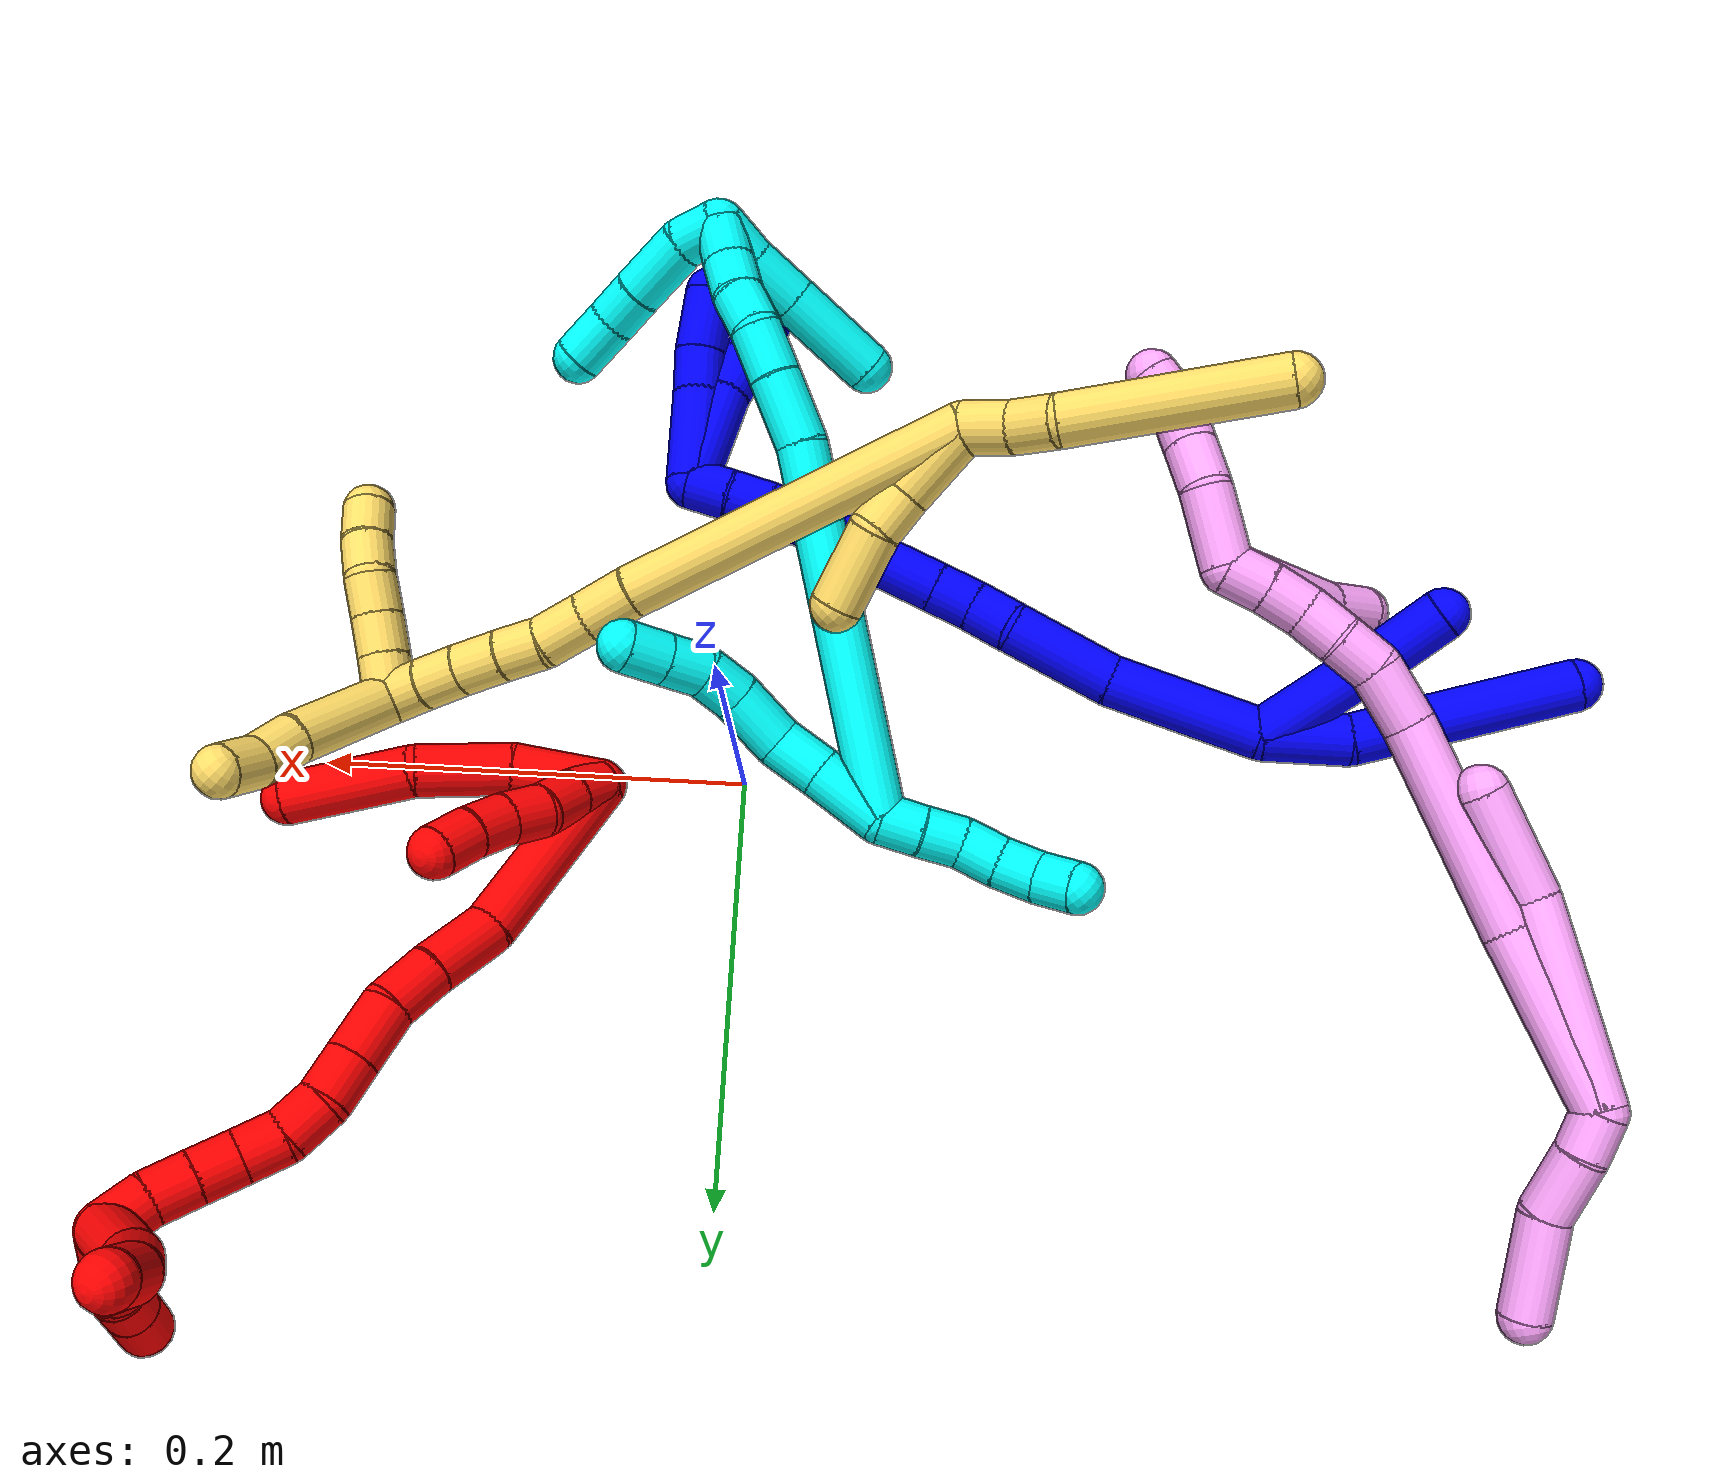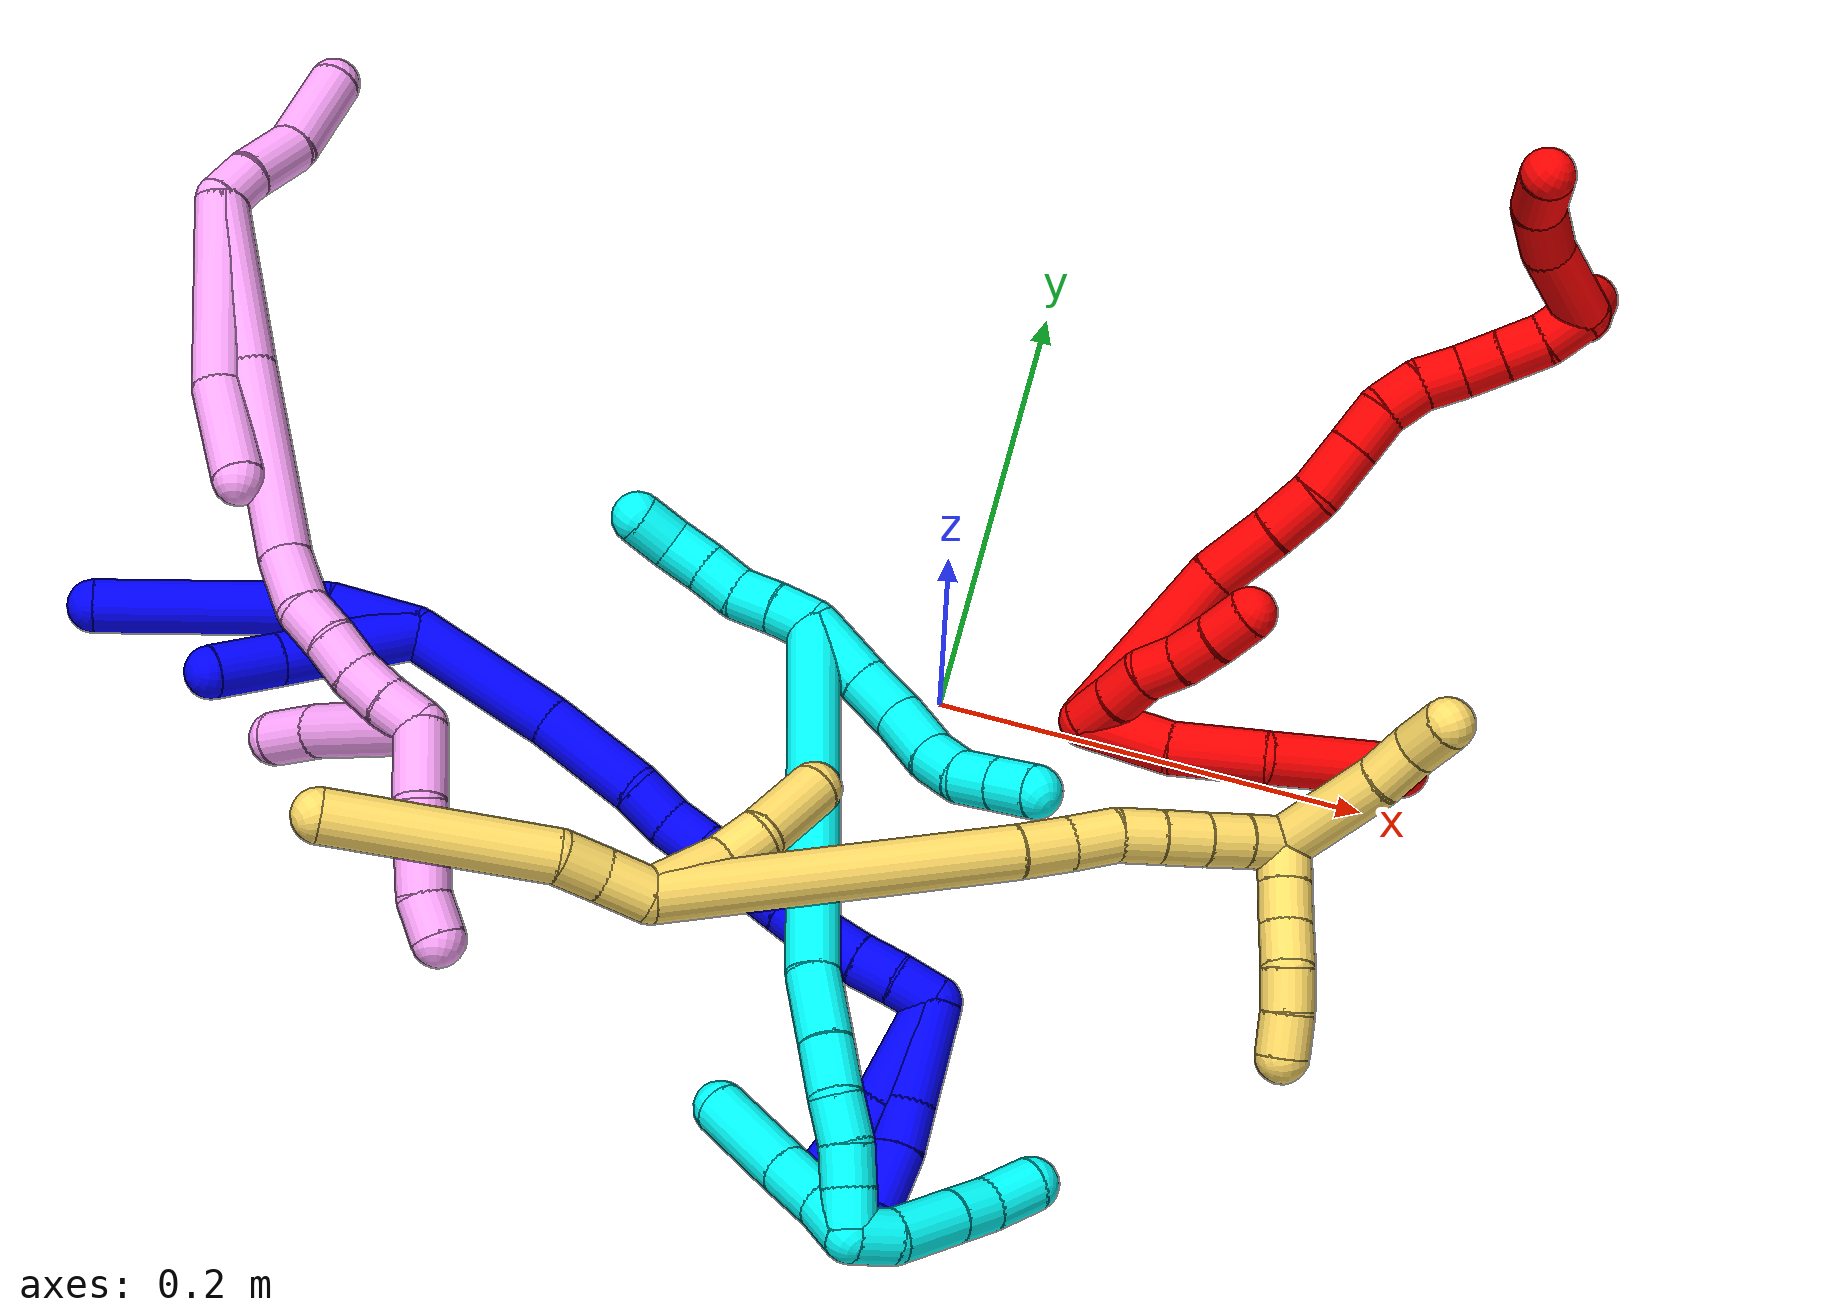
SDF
<sdf version="1.7">
 <world name="default">
  <plugin name="TubeGeneratorPlugin" filename="libtube_generator_plugin.so"/>
  <model name="photoneo_s_sensor">
   <static>1</static>
   <pose>0 0 2 1.57079 1.57079 3.14159</pose>
   <link name="link">
    <inertial><mass>0.1</mass></inertial>
    <sensor name="sensor" type="depth">
     <update_rate>30</update_rate>
     <camera>
      <horizontal_fov>1.22</horizontal_fov>
      <image><width>1920</width><height>1200</height><format>B8G8R8</format></image>
      <clip><near>0.1</near><far>4</far></clip>
      <depth_camera><output>points</output></depth_camera>
     </camera>
     <plugin name="camera_plugin" filename="libgazebo_ros_depth_camera.so">
      <baseline>0.2</baseline>
      <alwaysOn>1</alwaysOn>
      <updateRate>0.0</updateRate>
      <cameraName>camera_ir</cameraName>
      <imageTopicName>/camera/color/image_raw</imageTopicName>
      <cameraInfoTopicName>/camera/color/camera_info</cameraInfoTopicName>
      <depthImageTopicName>/camera/depth/image_raw</depthImageTopicName>
      <depthImageCameraInfoTopicName>/camera/depth/camera_info</depthImageCameraInfoTopicName>
      <pointCloudTopicName>/camera/depth/points</pointCloudTopicName>
      <frameName>fr_optical</frameName>
      <pointCloudCutoff>0.1</pointCloudCutoff>
      <pointCloudCutoffMax>2.0</pointCloudCutoffMax>
      <distortionK1>0</distortionK1>
      <distortionK2>0</distortionK2>
      <distortionK3>0</distortionK3>
      <distortionT1>0</distortionT1>
      <distortionT2>0</distortionT2>
      <CxPrime>0</CxPrime>
      <Cx>0</Cx>
      <Cy>0</Cy>
      <focalLength>0</focalLength>
      <hackBaseline>0</hackBaseline>
     </plugin>
    </sensor>
   </link>
  </model>
  <gravity>0 0 -9.8</gravity>
  <magnetic_field>6e-06 2.3e-05 -4.2e-05</magnetic_field>
  <atmosphere type="adiabatic"/>
  <physics name="default_physics" default="0" type="ode">
   <max_step_size>0.003</max_step_size>
   <real_time_factor>1</real_time_factor>
   <real_time_update_rate>1000</real_time_update_rate>
   <max_contacts>10000</max_contacts>
   <ode>
    <solver>
     <type>quick</type>
     <iters>100</iters>
     <sor>1.3</sor>
     <use_dynamic_moi_rescaling>0</use_dynamic_moi_rescaling>
    </solver>
    <constraints>
     <contact_max_correcting_vel>0</contact_max_correcting_vel>
     <contact_surface_layer>0.001</contact_surface_layer>
     <cfm>0</cfm>
     <erp>0.2</erp>
    </constraints>
   </ode>
  </physics>
  <scene><ambient>0.4 0.4 0.4 1</ambient><background>0.7 0.7 0.7 1</background><shadows>0</shadows></scene>
  <audio><device>default</device></audio>
  <spherical_coordinates>
   <surface_model>EARTH_WGS84</surface_model>
   <latitude_deg>0</latitude_deg>
   <longitude_deg>0</longitude_deg>
   <elevation>0</elevation>
   <heading_deg>0</heading_deg>
  </spherical_coordinates>
  <model name="bin">
   <static>1</static>
   <link name="bottom">
    <collision name="collision-bottom">
     <pose>0 0 -0.01 0 -0 0</pose>
     <geometry><box><size>0.8 0.6 0.02</size></box></geometry>
     <surface>
      <friction><ode><mu>100</mu><mu2>100</mu2></ode></friction>
      <contact><collide_bitmask>65535</collide_bitmask></contact>
     </surface>
    </collision>
   </link>
   <link name="west_wall">
    <collision name="collision-west_wall">
     <pose>-0.41 0 0.1 0 -0 0</pose>
     <geometry><box><size>0.02 0.6 0.2</size></box></geometry>
     <surface>
      <friction><ode><mu>100</mu><mu2>100</mu2></ode></friction>
      <contact><collide_bitmask>65535</collide_bitmask></contact>
     </surface>
    </collision>
   </link>
   <link name="east_wall">
    <collision name="collision-east_wall">
     <pose>0.41 0 0.1 0 -0 0</pose>
     <geometry><box><size>0.02 0.6 0.2</size></box></geometry>
     <surface>
      <friction><ode><mu>100</mu><mu2>100</mu2></ode></friction>
      <contact><collide_bitmask>65535</collide_bitmask></contact>
     </surface>
    </collision>
   </link>
   <link name="south_wall">
    <collision name="collision-south_wall">
     <pose>0 -0.31 0.1 0 -0 0</pose>
     <geometry><box><size>0.8 0.02 0.2</size></box></geometry>
     <surface>
      <friction><ode><mu>100</mu><mu2>100</mu2></ode></friction>
      <contact><collide_bitmask>65535</collide_bitmask></contact>
     </surface>
    </collision>
   </link>
   <link name="north_wall">
    <collision name="collision-north_wall">
     <pose>0 0.31 0.1 0 -0 0</pose>
     <geometry><box><size>0.8 0.02 0.2</size></box></geometry>
     <surface>
      <friction><ode><mu>100</mu><mu2>100</mu2></ode></friction>
      <contact><collide_bitmask>65535</collide_bitmask></contact>
     </surface>
    </collision>
   </link>
  </model>
  <model name="1">
   <static>0</static>
   <link name="1">
    <collision name="collision-cylinder-e_1_2_8">
     <pose>-0.015272 0.001272 0.013959 -0.090864 -0.828234 0.03996</pose>
     <geometry><cylinder><radius>0.0125</radius><length>0.041459</length></cylinder></geometry>
     <surface>
      <friction><ode><mu>1.16</mu><mu2>1.16</mu2><slip1>0</slip1><slip2>0</slip2></ode></friction>
      <contact><ode><kp>1e+06</kp><kd>1</kd><max_vel>0</max_vel><min_depth>0.001</min_depth></ode></contact>
     </surface>
    </collision>
    <visual name="visual-cylinder-e_1_2_8">
     <pose>-0.015272 0.001272 0.013959 -0.090864 -0.828234 0.03996</pose>
     <geometry><cylinder><radius>0.0125</radius><length>0.041459</length></cylinder></geometry>
     <material><ambient>0 0 1 1</ambient></material>
    </visual>
    <collision name="collision-cylinder-e_2_8_6">
     <pose>-0.061522 -0.005417 0.071762 0.179615 -0.607483 -0.056435</pose>
     <geometry><cylinder><radius>0.0125</radius><length>0.108541</length></cylinder></geometry>
     <surface>
      <friction><ode><mu>1.16</mu><mu2>1.16</mu2><slip1>0</slip1><slip2>0</slip2></ode></friction>
      <contact><ode><kp>1e+06</kp><kd>1</kd><max_vel>0</max_vel><min_depth>0.001</min_depth></ode></contact>
     </surface>
    </collision>
    <visual name="visual-cylinder-e_2_8_6">
     <pose>-0.061522 -0.005417 0.071762 0.179615 -0.607483 -0.056435</pose>
     <geometry><cylinder><radius>0.0125</radius><length>0.108541</length></cylinder></geometry>
     <material><ambient>0 0 1 1</ambient></material>
    </visual>
    <collision name="collision-cylinder-e_1_2_9">
     <pose>-0.007636 -0.007777 0.031899 0.239144 -0.228493 -0.027571</pose>
     <geometry><cylinder><radius>0.0125</radius><length>0.067419</length></cylinder></geometry>
     <surface>
      <friction><ode><mu>1.16</mu><mu2>1.16</mu2><slip1>0</slip1><slip2>0</slip2></ode></friction>
      <contact><ode><kp>1e+06</kp><kd>1</kd><max_vel>0</max_vel><min_depth>0.001</min_depth></ode></contact>
     </surface>
    </collision>
    <visual name="visual-cylinder-e_1_2_9">
     <pose>-0.007636 -0.007777 0.031899 0.239144 -0.228493 -0.027571</pose>
     <geometry><cylinder><radius>0.0125</radius><length>0.067419</length></cylinder></geometry>
     <material><ambient>0 0 1 1</ambient></material>
    </visual>
    <collision name="collision-cylinder-e_2_9_5">
     <pose>-0.017613 -0.018585 0.079632 0.189092 -0.144253 -0.013703</pose>
     <geometry><cylinder><radius>0.0125</radius><length>0.032581</length></cylinder></geometry>
     <surface>
      <friction><ode><mu>1.16</mu><mu2>1.16</mu2><slip1>0</slip1><slip2>0</slip2></ode></friction>
      <contact><ode><kp>1e+06</kp><kd>1</kd><max_vel>0</max_vel><min_depth>0.001</min_depth></ode></contact>
     </surface>
    </collision>
    <visual name="visual-cylinder-e_2_9_5">
     <pose>-0.017613 -0.018585 0.079632 0.189092 -0.144253 -0.013703</pose>
     <geometry><cylinder><radius>0.0125</radius><length>0.032581</length></cylinder></geometry>
     <material><ambient>0 0 1 1</ambient></material>
    </visual>
    <collision name="collision-cylinder-e_1_2_10">
     <pose>0.029673 -0.01249 -0.019935 2.5819 0.900474 2.06874</pose>
     <geometry><cylinder><radius>0.0125</radius><length>0.075733</length></cylinder></geometry>
     <surface>
      <friction><ode><mu>1.16</mu><mu2>1.16</mu2><slip1>0</slip1><slip2>0</slip2></ode></friction>
      <contact><ode><kp>1e+06</kp><kd>1</kd><max_vel>0</max_vel><min_depth>0.001</min_depth></ode></contact>
     </surface>
    </collision>
    <visual name="visual-cylinder-e_1_2_10">
     <pose>0.029673 -0.01249 -0.019935 2.5819 0.900474 2.06874</pose>
     <geometry><cylinder><radius>0.0125</radius><length>0.075733</length></cylinder></geometry>
     <material><ambient>0 0 1 1</ambient></material>
    </visual>
    <collision name="collision-cylinder-e_2_10_11">
     <pose>0.08274 -0.033558 -0.04936 2.40663 1.07037 1.98983</pose>
     <geometry><cylinder><radius>0.0125</radius><length>0.053328</length></cylinder></geometry>
     <surface>
      <friction><ode><mu>1.16</mu><mu2>1.16</mu2><slip1>0</slip1><slip2>0</slip2></ode></friction>
      <contact><ode><kp>1e+06</kp><kd>1</kd><max_vel>0</max_vel><min_depth>0.001</min_depth></ode></contact>
     </surface>
    </collision>
    <visual name="visual-cylinder-e_2_10_11">
     <pose>0.08274 -0.033558 -0.04936 2.40663 1.07037 1.98983</pose>
     <geometry><cylinder><radius>0.0125</radius><length>0.053328</length></cylinder></geometry>
     <material><ambient>0 0 1 1</ambient></material>
    </visual>
    <collision name="collision-cylinder-e_3_11_12">
     <pose>0.113932 -0.047669 -0.063632 2.28348 0.817517 1.51619</pose>
     <geometry><cylinder><radius>0.0125</radius><length>0.021378</length></cylinder></geometry>
     <surface>
      <friction><ode><mu>1.16</mu><mu2>1.16</mu2><slip1>0</slip1><slip2>0</slip2></ode></friction>
      <contact><ode><kp>1e+06</kp><kd>1</kd><max_vel>0</max_vel><min_depth>0.001</min_depth></ode></contact>
     </surface>
    </collision>
    <visual name="visual-cylinder-e_3_11_12">
     <pose>0.113932 -0.047669 -0.063632 2.28348 0.817517 1.51619</pose>
     <geometry><cylinder><radius>0.0125</radius><length>0.021378</length></cylinder></geometry>
     <material><ambient>0 0 1 1</ambient></material>
    </visual>
    <collision name="collision-cylinder-e_4_12_13">
     <pose>0.130791 -0.056542 -0.072592 2.46711 1.03739 2.03992</pose>
     <geometry><cylinder><radius>0.0125</radius><length>0.021047</length></cylinder></geometry>
     <surface>
      <friction><ode><mu>1.16</mu><mu2>1.16</mu2><slip1>0</slip1><slip2>0</slip2></ode></friction>
      <contact><ode><kp>1e+06</kp><kd>1</kd><max_vel>0</max_vel><min_depth>0.001</min_depth></ode></contact>
     </surface>
    </collision>
    <visual name="visual-cylinder-e_4_12_13">
     <pose>0.130791 -0.056542 -0.072592 2.46711 1.03739 2.03992</pose>
     <geometry><cylinder><radius>0.0125</radius><length>0.021047</length></cylinder></geometry>
     <material><ambient>0 0 1 1</ambient></material>
    </visual>
    <collision name="collision-cylinder-e_5_13_14">
     <pose>0.151638 -0.063989 -0.082205 2.49457 1.04684 2.08895</pose>
     <geometry><cylinder><radius>0.0125</radius><length>0.027224</length></cylinder></geometry>
     <surface>
      <friction><ode><mu>1.16</mu><mu2>1.16</mu2><slip1>0</slip1><slip2>0</slip2></ode></friction>
      <contact><ode><kp>1e+06</kp><kd>1</kd><max_vel>0</max_vel><min_depth>0.001</min_depth></ode></contact>
     </surface>
    </collision>
    <visual name="visual-cylinder-e_5_13_14">
     <pose>0.151638 -0.063989 -0.082205 2.49457 1.04684 2.08895</pose>
     <geometry><cylinder><radius>0.0125</radius><length>0.027224</length></cylinder></geometry>
     <material><ambient>0 0 1 1</ambient></material>
    </visual>
    <collision name="collision-cylinder-e_6_14_15">
     <pose>0.172101 -0.071464 -0.091381 2.40856 1.04497 1.96571</pose>
     <geometry><cylinder><radius>0.0125</radius><length>0.020065</length></cylinder></geometry>
     <surface>
      <friction><ode><mu>1.16</mu><mu2>1.16</mu2><slip1>0</slip1><slip2>0</slip2></ode></friction>
      <contact><ode><kp>1e+06</kp><kd>1</kd><max_vel>0</max_vel><min_depth>0.001</min_depth></ode></contact>
     </surface>
    </collision>
    <visual name="visual-cylinder-e_6_14_15">
     <pose>0.172101 -0.071464 -0.091381 2.40856 1.04497 1.96571</pose>
     <geometry><cylinder><radius>0.0125</radius><length>0.020065</length></cylinder></geometry>
     <material><ambient>0 0 1 1</ambient></material>
    </visual>
    <collision name="collision-cylinder-e_7_15_16">
     <pose>0.18971 -0.078198 -0.099041 2.432 1.04652 1.99987</pose>
     <geometry><cylinder><radius>0.0125</radius><length>0.020634</length></cylinder></geometry>
     <surface>
      <friction><ode><mu>1.16</mu><mu2>1.16</mu2><slip1>0</slip1><slip2>0</slip2></ode></friction>
      <contact><ode><kp>1e+06</kp><kd>1</kd><max_vel>0</max_vel><min_depth>0.001</min_depth></ode></contact>
     </surface>
    </collision>
    <visual name="visual-cylinder-e_7_15_16">
     <pose>0.18971 -0.078198 -0.099041 2.432 1.04652 1.99987</pose>
     <geometry><cylinder><radius>0.0125</radius><length>0.020634</length></cylinder></geometry>
     <material><ambient>0 0 1 1</ambient></material>
    </visual>
    <collision name="collision-cylinder-e_8_16_17">
     <pose>0.207305 -0.084349 -0.107673 2.60786 1.00714 2.22037</pose>
     <geometry><cylinder><radius>0.0125</radius><length>0.0205</length></cylinder></geometry>
     <surface>
      <friction><ode><mu>1.16</mu><mu2>1.16</mu2><slip1>0</slip1><slip2>0</slip2></ode></friction>
      <contact><ode><kp>1e+06</kp><kd>1</kd><max_vel>0</max_vel><min_depth>0.001</min_depth></ode></contact>
     </surface>
    </collision>
    <visual name="visual-cylinder-e_8_16_17">
     <pose>0.207305 -0.084349 -0.107673 2.60786 1.00714 2.22037</pose>
     <geometry><cylinder><radius>0.0125</radius><length>0.0205</length></cylinder></geometry>
     <material><ambient>0 0 1 1</ambient></material>
    </visual>
    <collision name="collision-cylinder-e_9_17_18">
     <pose>0.22446 -0.089159 -0.117361 2.75507 1.00692 2.4588</pose>
     <geometry><cylinder><radius>0.0125</radius><length>0.02009</length></cylinder></geometry>
     <surface>
      <friction><ode><mu>1.16</mu><mu2>1.16</mu2><slip1>0</slip1><slip2>0</slip2></ode></friction>
      <contact><ode><kp>1e+06</kp><kd>1</kd><max_vel>0</max_vel><min_depth>0.001</min_depth></ode></contact>
     </surface>
    </collision>
    <visual name="visual-cylinder-e_9_17_18">
     <pose>0.22446 -0.089159 -0.117361 2.75507 1.00692 2.4588</pose>
     <geometry><cylinder><radius>0.0125</radius><length>0.02009</length></cylinder></geometry>
     <material><ambient>0 0 1 1</ambient></material>
    </visual>
    <collision name="collision-cylinder-e_10_18_1">
     <pose>0.240813 -0.094051 -0.127807 2.65886 0.904776 2.20391</pose>
     <geometry><cylinder><radius>0.0125</radius><length>0.02</length></cylinder></geometry>
     <surface>
      <friction><ode><mu>1.16</mu><mu2>1.16</mu2><slip1>0</slip1><slip2>0</slip2></ode></friction>
      <contact><ode><kp>1e+06</kp><kd>1</kd><max_vel>0</max_vel><min_depth>0.001</min_depth></ode></contact>
     </surface>
    </collision>
    <visual name="visual-cylinder-e_10_18_1">
     <pose>0.240813 -0.094051 -0.127807 2.65886 0.904776 2.20391</pose>
     <geometry><cylinder><radius>0.0125</radius><length>0.02</length></cylinder></geometry>
     <material><ambient>0 0 1 1</ambient></material>
    </visual>
    <collision name="collision-cylinder-e_1_1_19">
     <pose>0.250905 -0.119212 -0.120366 1.04577 0.086292 0.049759</pose>
     <geometry><cylinder><radius>0.0125</radius><length>0.051717</length></cylinder></geometry>
     <surface>
      <friction><ode><mu>1.16</mu><mu2>1.16</mu2><slip1>0</slip1><slip2>0</slip2></ode></friction>
      <contact><ode><kp>1e+06</kp><kd>1</kd><max_vel>0</max_vel><min_depth>0.001</min_depth></ode></contact>
     </surface>
    </collision>
    <visual name="visual-cylinder-e_1_1_19">
     <pose>0.250905 -0.119212 -0.120366 1.04577 0.086292 0.049759</pose>
     <geometry><cylinder><radius>0.0125</radius><length>0.051717</length></cylinder></geometry>
     <material><ambient>0 0 1 1</ambient></material>
    </visual>
    <collision name="collision-cylinder-e_2_19_20">
     <pose>0.252615 -0.150592 -0.100611 0.925437 -0.045525 -0.022713</pose>
     <geometry><cylinder><radius>0.0125</radius><length>0.022776</length></cylinder></geometry>
     <surface>
      <friction><ode><mu>1.16</mu><mu2>1.16</mu2><slip1>0</slip1><slip2>0</slip2></ode></friction>
      <contact><ode><kp>1e+06</kp><kd>1</kd><max_vel>0</max_vel><min_depth>0.001</min_depth></ode></contact>
     </surface>
    </collision>
    <visual name="visual-cylinder-e_2_19_20">
     <pose>0.252615 -0.150592 -0.100611 0.925437 -0.045525 -0.022713</pose>
     <geometry><cylinder><radius>0.0125</radius><length>0.022776</length></cylinder></geometry>
     <material><ambient>0 0 1 1</ambient></material>
    </visual>
    <collision name="collision-cylinder-e_3_20_4">
     <pose>0.252351 -0.169594 -0.085749 0.890644 0.01991 0.009503</pose>
     <geometry><cylinder><radius>0.0125</radius><length>0.025507</length></cylinder></geometry>
     <surface>
      <friction><ode><mu>1.16</mu><mu2>1.16</mu2><slip1>0</slip1><slip2>0</slip2></ode></friction>
      <contact><ode><kp>1e+06</kp><kd>1</kd><max_vel>0</max_vel><min_depth>0.001</min_depth></ode></contact>
     </surface>
    </collision>
    <visual name="visual-cylinder-e_3_20_4">
     <pose>0.252351 -0.169594 -0.085749 0.890644 0.01991 0.009503</pose>
     <geometry><cylinder><radius>0.0125</radius><length>0.025507</length></cylinder></geometry>
     <material><ambient>0 0 1 1</ambient></material>
    </visual>
    <collision name="collision-cylinder-e_1_1_21">
     <pose>0.256197 -0.117489 -0.12412 1.15186 0.322339 0.210368</pose>
     <geometry><cylinder><radius>0.0125</radius><length>0.047479</length></cylinder></geometry>
     <surface>
      <friction><ode><mu>1.16</mu><mu2>1.16</mu2><slip1>0</slip1><slip2>0</slip2></ode></friction>
      <contact><ode><kp>1e+06</kp><kd>1</kd><max_vel>0</max_vel><min_depth>0.001</min_depth></ode></contact>
     </surface>
    </collision>
    <visual name="visual-cylinder-e_1_1_21">
     <pose>0.256197 -0.117489 -0.12412 1.15186 0.322339 0.210368</pose>
     <geometry><cylinder><radius>0.0125</radius><length>0.047479</length></cylinder></geometry>
     <material><ambient>0 0 1 1</ambient></material>
    </visual>
    <collision name="collision-cylinder-e_2_21_22">
     <pose>0.268148 -0.146902 -0.109932 1.05381 0.410747 0.241198</pose>
     <geometry><cylinder><radius>0.0125</radius><length>0.022191</length></cylinder></geometry>
     <surface>
      <friction><ode><mu>1.16</mu><mu2>1.16</mu2><slip1>0</slip1><slip2>0</slip2></ode></friction>
      <contact><ode><kp>1e+06</kp><kd>1</kd><max_vel>0</max_vel><min_depth>0.001</min_depth></ode></contact>
     </surface>
    </collision>
    <visual name="visual-cylinder-e_2_21_22">
     <pose>0.268148 -0.146902 -0.109932 1.05381 0.410747 0.241198</pose>
     <geometry><cylinder><radius>0.0125</radius><length>0.022191</length></cylinder></geometry>
     <material><ambient>0 0 1 1</ambient></material>
    </visual>
    <collision name="collision-cylinder-e_3_22_3">
     <pose>0.277884 -0.166594 -0.095732 0.868948 0.357442 0.167268</pose>
     <geometry><cylinder><radius>0.0125</radius><length>0.030329</length></cylinder></geometry>
     <surface>
      <friction><ode><mu>1.16</mu><mu2>1.16</mu2><slip1>0</slip1><slip2>0</slip2></ode></friction>
      <contact><ode><kp>1e+06</kp><kd>1</kd><max_vel>0</max_vel><min_depth>0.001</min_depth></ode></contact>
     </surface>
    </collision>
    <visual name="visual-cylinder-e_3_22_3">
     <pose>0.277884 -0.166594 -0.095732 0.868948 0.357442 0.167268</pose>
     <geometry><cylinder><radius>0.0125</radius><length>0.030329</length></cylinder></geometry>
     <material><ambient>0 0 1 1</ambient></material>
    </visual>
    <collision name="collision-sphere-3">
     <pose>0.283189 -0.177443 -0.08656 0 -0 0</pose>
     <geometry><sphere><radius>0.0125</radius></sphere></geometry>
     <surface>
      <friction><ode><mu>1.16</mu><mu2>1.16</mu2><slip1>0</slip1><slip2>0</slip2></ode></friction>
      <contact><ode><kp>1e+06</kp><kd>1</kd><max_vel>0</max_vel><min_depth>0.001</min_depth></ode></contact>
     </surface>
    </collision>
    <visual name="visual-sphere-3">
     <pose>0.283189 -0.177443 -0.08656 0 -0 0</pose>
     <geometry><sphere><radius>0.0125</radius></sphere></geometry>
     <material><ambient>0 0 1 1</ambient></material>
    </visual>
    <collision name="collision-sphere-22">
     <pose>0.272578 -0.155746 -0.104904 0 -0 0</pose>
     <geometry><sphere><radius>0.0125</radius></sphere></geometry>
     <surface>
      <friction><ode><mu>1.16</mu><mu2>1.16</mu2><slip1>0</slip1><slip2>0</slip2></ode></friction>
      <contact><ode><kp>1e+06</kp><kd>1</kd><max_vel>0</max_vel><min_depth>0.001</min_depth></ode></contact>
     </surface>
    </collision>
    <visual name="visual-sphere-22">
     <pose>0.272578 -0.155746 -0.104904 0 -0 0</pose>
     <geometry><sphere><radius>0.0125</radius></sphere></geometry>
     <material><ambient>0 0 1 1</ambient></material>
    </visual>
    <collision name="collision-sphere-21">
     <pose>0.263717 -0.138059 -0.11496 0 -0 0</pose>
     <geometry><sphere><radius>0.0125</radius></sphere></geometry>
     <surface>
      <friction><ode><mu>1.16</mu><mu2>1.16</mu2><slip1>0</slip1><slip2>0</slip2></ode></friction>
      <contact><ode><kp>1e+06</kp><kd>1</kd><max_vel>0</max_vel><min_depth>0.001</min_depth></ode></contact>
     </surface>
    </collision>
    <visual name="visual-sphere-21">
     <pose>0.263717 -0.138059 -0.11496 0 -0 0</pose>
     <geometry><sphere><radius>0.0125</radius></sphere></geometry>
     <material><ambient>0 0 1 1</ambient></material>
    </visual>
    <collision name="collision-sphere-4">
     <pose>0.252605 -0.179508 -0.077729 0 -0 0</pose>
     <geometry><sphere><radius>0.0125</radius></sphere></geometry>
     <surface>
      <friction><ode><mu>1.16</mu><mu2>1.16</mu2><slip1>0</slip1><slip2>0</slip2></ode></friction>
      <contact><ode><kp>1e+06</kp><kd>1</kd><max_vel>0</max_vel><min_depth>0.001</min_depth></ode></contact>
     </surface>
    </collision>
    <visual name="visual-sphere-4">
     <pose>0.252605 -0.179508 -0.077729 0 -0 0</pose>
     <geometry><sphere><radius>0.0125</radius></sphere></geometry>
     <material><ambient>0 0 1 1</ambient></material>
    </visual>
    <collision name="collision-sphere-20">
     <pose>0.252097 -0.15968 -0.093768 0 -0 0</pose>
     <geometry><sphere><radius>0.0125</radius></sphere></geometry>
     <surface>
      <friction><ode><mu>1.16</mu><mu2>1.16</mu2><slip1>0</slip1><slip2>0</slip2></ode></friction>
      <contact><ode><kp>1e+06</kp><kd>1</kd><max_vel>0</max_vel><min_depth>0.001</min_depth></ode></contact>
     </surface>
    </collision>
    <visual name="visual-sphere-20">
     <pose>0.252097 -0.15968 -0.093768 0 -0 0</pose>
     <geometry><sphere><radius>0.0125</radius></sphere></geometry>
     <material><ambient>0 0 1 1</ambient></material>
    </visual>
    <collision name="collision-sphere-10">
     <pose>0.059346 -0.024979 -0.039869 0 -0 0</pose>
     <geometry><sphere><radius>0.0125</radius></sphere></geometry>
     <surface>
      <friction><ode><mu>1.16</mu><mu2>1.16</mu2><slip1>0</slip1><slip2>0</slip2></ode></friction>
      <contact><ode><kp>1e+06</kp><kd>1</kd><max_vel>0</max_vel><min_depth>0.001</min_depth></ode></contact>
     </surface>
    </collision>
    <visual name="visual-sphere-10">
     <pose>0.059346 -0.024979 -0.039869 0 -0 0</pose>
     <geometry><sphere><radius>0.0125</radius></sphere></geometry>
     <material><ambient>0 0 1 1</ambient></material>
    </visual>
    <collision name="collision-sphere-5">
     <pose>-0.019955 -0.021615 0.095466 0 -0 0</pose>
     <geometry><sphere><radius>0.0125</radius></sphere></geometry>
     <surface>
      <friction><ode><mu>1.16</mu><mu2>1.16</mu2><slip1>0</slip1><slip2>0</slip2></ode></friction>
      <contact><ode><kp>1e+06</kp><kd>1</kd><max_vel>0</max_vel><min_depth>0.001</min_depth></ode></contact>
     </surface>
    </collision>
    <visual name="visual-sphere-5">
     <pose>-0.019955 -0.021615 0.095466 0 -0 0</pose>
     <geometry><sphere><radius>0.0125</radius></sphere></geometry>
     <material><ambient>0 0 1 1</ambient></material>
    </visual>
    <collision name="collision-sphere-6">
     <pose>-0.0925 -0.013378 0.115606 0 -0 0</pose>
     <geometry><sphere><radius>0.0125</radius></sphere></geometry>
     <surface>
      <friction><ode><mu>1.16</mu><mu2>1.16</mu2><slip1>0</slip1><slip2>0</slip2></ode></friction>
      <contact><ode><kp>1e+06</kp><kd>1</kd><max_vel>0</max_vel><min_depth>0.001</min_depth></ode></contact>
     </surface>
    </collision>
    <visual name="visual-sphere-6">
     <pose>-0.0925 -0.013378 0.115606 0 -0 0</pose>
     <geometry><sphere><radius>0.0125</radius></sphere></geometry>
     <material><ambient>0 0 1 1</ambient></material>
    </visual>
    <collision name="collision-sphere-9">
     <pose>-0.015271 -0.015554 0.063798 0 -0 0</pose>
     <geometry><sphere><radius>0.0125</radius></sphere></geometry>
     <surface>
      <friction><ode><mu>1.16</mu><mu2>1.16</mu2><slip1>0</slip1><slip2>0</slip2></ode></friction>
      <contact><ode><kp>1e+06</kp><kd>1</kd><max_vel>0</max_vel><min_depth>0.001</min_depth></ode></contact>
     </surface>
    </collision>
    <visual name="visual-sphere-9">
     <pose>-0.015271 -0.015554 0.063798 0 -0 0</pose>
     <geometry><sphere><radius>0.0125</radius></sphere></geometry>
     <material><ambient>0 0 1 1</ambient></material>
    </visual>
    <collision name="collision-sphere-2">
     <geometry><sphere><radius>0.0125</radius></sphere></geometry>
     <surface>
      <friction><ode><mu>1.16</mu><mu2>1.16</mu2><slip1>0</slip1><slip2>0</slip2></ode></friction>
      <contact><ode><kp>1e+06</kp><kd>1</kd><max_vel>0</max_vel><min_depth>0.001</min_depth></ode></contact>
     </surface>
    </collision>
    <visual name="visual-sphere-2">
     <geometry><sphere><radius>0.0125</radius></sphere></geometry>
     <material><ambient>0 0 1 1</ambient></material>
    </visual>
    <collision name="collision-sphere-19">
     <pose>0.253133 -0.141504 -0.107453 0 -0 0</pose>
     <geometry><sphere><radius>0.0125</radius></sphere></geometry>
     <surface>
      <friction><ode><mu>1.16</mu><mu2>1.16</mu2><slip1>0</slip1><slip2>0</slip2></ode></friction>
      <contact><ode><kp>1e+06</kp><kd>1</kd><max_vel>0</max_vel><min_depth>0.001</min_depth></ode></contact>
     </surface>
    </collision>
    <visual name="visual-sphere-19">
     <pose>0.253133 -0.141504 -0.107453 0 -0 0</pose>
     <geometry><sphere><radius>0.0125</radius></sphere></geometry>
     <material><ambient>0 0 1 1</ambient></material>
    </visual>
    <collision name="collision-sphere-8">
     <pose>-0.030544 0.002544 0.027918 0 -0 0</pose>
     <geometry><sphere><radius>0.0125</radius></sphere></geometry>
     <surface>
      <friction><ode><mu>1.16</mu><mu2>1.16</mu2><slip1>0</slip1><slip2>0</slip2></ode></friction>
      <contact><ode><kp>1e+06</kp><kd>1</kd><max_vel>0</max_vel><min_depth>0.001</min_depth></ode></contact>
     </surface>
    </collision>
    <visual name="visual-sphere-8">
     <pose>-0.030544 0.002544 0.027918 0 -0 0</pose>
     <geometry><sphere><radius>0.0125</radius></sphere></geometry>
     <material><ambient>0 0 1 1</ambient></material>
    </visual>
    <collision name="collision-sphere-11">
     <pose>0.106135 -0.042137 -0.058851 0 -0 0</pose>
     <geometry><sphere><radius>0.0125</radius></sphere></geometry>
     <surface>
      <friction><ode><mu>1.16</mu><mu2>1.16</mu2><slip1>0</slip1><slip2>0</slip2></ode></friction>
      <contact><ode><kp>1e+06</kp><kd>1</kd><max_vel>0</max_vel><min_depth>0.001</min_depth></ode></contact>
     </surface>
    </collision>
    <visual name="visual-sphere-11">
     <pose>0.106135 -0.042137 -0.058851 0 -0 0</pose>
     <geometry><sphere><radius>0.0125</radius></sphere></geometry>
     <material><ambient>0 0 1 1</ambient></material>
    </visual>
    <collision name="collision-sphere-12">
     <pose>0.121729 -0.053201 -0.068413 0 -0 0</pose>
     <geometry><sphere><radius>0.0125</radius></sphere></geometry>
     <surface>
      <friction><ode><mu>1.16</mu><mu2>1.16</mu2><slip1>0</slip1><slip2>0</slip2></ode></friction>
      <contact><ode><kp>1e+06</kp><kd>1</kd><max_vel>0</max_vel><min_depth>0.001</min_depth></ode></contact>
     </surface>
    </collision>
    <visual name="visual-sphere-12">
     <pose>0.121729 -0.053201 -0.068413 0 -0 0</pose>
     <geometry><sphere><radius>0.0125</radius></sphere></geometry>
     <material><ambient>0 0 1 1</ambient></material>
    </visual>
    <collision name="collision-sphere-13">
     <pose>0.139852 -0.059884 -0.076771 0 -0 0</pose>
     <geometry><sphere><radius>0.0125</radius></sphere></geometry>
     <surface>
      <friction><ode><mu>1.16</mu><mu2>1.16</mu2><slip1>0</slip1><slip2>0</slip2></ode></friction>
      <contact><ode><kp>1e+06</kp><kd>1</kd><max_vel>0</max_vel><min_depth>0.001</min_depth></ode></contact>
     </surface>
    </collision>
    <visual name="visual-sphere-13">
     <pose>0.139852 -0.059884 -0.076771 0 -0 0</pose>
     <geometry><sphere><radius>0.0125</radius></sphere></geometry>
     <material><ambient>0 0 1 1</ambient></material>
    </visual>
    <collision name="collision-sphere-14">
     <pose>0.163424 -0.068095 -0.087638 0 -0 0</pose>
     <geometry><sphere><radius>0.0125</radius></sphere></geometry>
     <surface>
      <friction><ode><mu>1.16</mu><mu2>1.16</mu2><slip1>0</slip1><slip2>0</slip2></ode></friction>
      <contact><ode><kp>1e+06</kp><kd>1</kd><max_vel>0</max_vel><min_depth>0.001</min_depth></ode></contact>
     </surface>
    </collision>
    <visual name="visual-sphere-14">
     <pose>0.163424 -0.068095 -0.087638 0 -0 0</pose>
     <geometry><sphere><radius>0.0125</radius></sphere></geometry>
     <material><ambient>0 0 1 1</ambient></material>
    </visual>
    <collision name="collision-sphere-15">
     <pose>0.180779 -0.074833 -0.095123 0 -0 0</pose>
     <geometry><sphere><radius>0.0125</radius></sphere></geometry>
     <surface>
      <friction><ode><mu>1.16</mu><mu2>1.16</mu2><slip1>0</slip1><slip2>0</slip2></ode></friction>
      <contact><ode><kp>1e+06</kp><kd>1</kd><max_vel>0</max_vel><min_depth>0.001</min_depth></ode></contact>
     </surface>
    </collision>
    <visual name="visual-sphere-15">
     <pose>0.180779 -0.074833 -0.095123 0 -0 0</pose>
     <geometry><sphere><radius>0.0125</radius></sphere></geometry>
     <material><ambient>0 0 1 1</ambient></material>
    </visual>
    <collision name="collision-sphere-16">
     <pose>0.198641 -0.081563 -0.102959 0 -0 0</pose>
     <geometry><sphere><radius>0.0125</radius></sphere></geometry>
     <surface>
      <friction><ode><mu>1.16</mu><mu2>1.16</mu2><slip1>0</slip1><slip2>0</slip2></ode></friction>
      <contact><ode><kp>1e+06</kp><kd>1</kd><max_vel>0</max_vel><min_depth>0.001</min_depth></ode></contact>
     </surface>
    </collision>
    <visual name="visual-sphere-16">
     <pose>0.198641 -0.081563 -0.102959 0 -0 0</pose>
     <geometry><sphere><radius>0.0125</radius></sphere></geometry>
     <material><ambient>0 0 1 1</ambient></material>
    </visual>
    <collision name="collision-sphere-17">
     <pose>0.21597 -0.087135 -0.112388 0 -0 0</pose>
     <geometry><sphere><radius>0.0125</radius></sphere></geometry>
     <surface>
      <friction><ode><mu>1.16</mu><mu2>1.16</mu2><slip1>0</slip1><slip2>0</slip2></ode></friction>
      <contact><ode><kp>1e+06</kp><kd>1</kd><max_vel>0</max_vel><min_depth>0.001</min_depth></ode></contact>
     </surface>
    </collision>
    <visual name="visual-sphere-17">
     <pose>0.21597 -0.087135 -0.112388 0 -0 0</pose>
     <geometry><sphere><radius>0.0125</radius></sphere></geometry>
     <material><ambient>0 0 1 1</ambient></material>
    </visual>
    <collision name="collision-sphere-18">
     <pose>0.23295 -0.091183 -0.122334 0 -0 0</pose>
     <geometry><sphere><radius>0.0125</radius></sphere></geometry>
     <surface>
      <friction><ode><mu>1.16</mu><mu2>1.16</mu2><slip1>0</slip1><slip2>0</slip2></ode></friction>
      <contact><ode><kp>1e+06</kp><kd>1</kd><max_vel>0</max_vel><min_depth>0.001</min_depth></ode></contact>
     </surface>
    </collision>
    <visual name="visual-sphere-18">
     <pose>0.23295 -0.091183 -0.122334 0 -0 0</pose>
     <geometry><sphere><radius>0.0125</radius></sphere></geometry>
     <material><ambient>0 0 1 1</ambient></material>
    </visual>
    <collision name="collision-sphere-1">
     <pose>0.248676 -0.09692 -0.133279 0 -0 0</pose>
     <geometry><sphere><radius>0.0125</radius></sphere></geometry>
     <surface>
      <friction><ode><mu>1.16</mu><mu2>1.16</mu2><slip1>0</slip1><slip2>0</slip2></ode></friction>
      <contact><ode><kp>1e+06</kp><kd>1</kd><max_vel>0</max_vel><min_depth>0.001</min_depth></ode></contact>
     </surface>
    </collision>
    <visual name="visual-sphere-1">
     <pose>0.248676 -0.09692 -0.133279 0 -0 0</pose>
     <geometry><sphere><radius>0.0125</radius></sphere></geometry>
     <material><ambient>0 0 1 1</ambient></material>
    </visual>
    <inertial>
     <pose>0.106972 -0.059484 -0.038791 0 -0 0</pose>
     <mass>0.75</mass>
     <inertia>
      <ixx>0.000188</ixx>
      <ixy>0</ixy>
      <ixz>0</ixz>
      <iyy>0.000229</iyy>
      <iyz>0</iyz>
      <izz>0.000102</izz>
     </inertia>
    </inertial>
   </link>
   <pose>-0.242772 -0.034513 0.015866 0.745284 -0.601437 -0.437644</pose>
  </model>
  <model name="2">
   <static>0</static>
   <link name="2">
    <collision name="collision-cylinder-e_1_2_8">
     <pose>0.018976 7.2e-05 0.008549 -0.008405 1.14749 -0.005432</pose>
     <geometry><cylinder><radius>0.0125</radius><length>0.041626</length></cylinder></geometry>
     <surface>
      <friction><ode><mu>1.16</mu><mu2>1.16</mu2><slip1>0</slip1><slip2>0</slip2></ode></friction>
      <contact><ode><kp>1e+06</kp><kd>1</kd><max_vel>0</max_vel><min_depth>0.001</min_depth></ode></contact>
     </surface>
    </collision>
    <visual name="visual-cylinder-e_1_2_8">
     <pose>0.018976 7.2e-05 0.008549 -0.008405 1.14749 -0.005432</pose>
     <geometry><cylinder><radius>0.0125</radius><length>0.041626</length></cylinder></geometry>
     <material><ambient>1 0 0 1</ambient></material>
    </visual>
    <collision name="collision-cylinder-e_2_8_9">
     <pose>0.05664 0.004055 0.028739 -0.32416 0.989438 -0.175965</pose>
     <geometry><cylinder><radius>0.0125</radius><length>0.044723</length></cylinder></geometry>
     <surface>
      <friction><ode><mu>1.16</mu><mu2>1.16</mu2><slip1>0</slip1><slip2>0</slip2></ode></friction>
      <contact><ode><kp>1e+06</kp><kd>1</kd><max_vel>0</max_vel><min_depth>0.001</min_depth></ode></contact>
     </surface>
    </collision>
    <visual name="visual-cylinder-e_2_8_9">
     <pose>0.05664 0.004055 0.028739 -0.32416 0.989438 -0.175965</pose>
     <geometry><cylinder><radius>0.0125</radius><length>0.044723</length></cylinder></geometry>
     <material><ambient>1 0 0 1</ambient></material>
    </visual>
    <collision name="collision-cylinder-e_3_9_6">
     <pose>0.102463 0.021744 0.049693 -0.976366 1.02098 -0.578124</pose>
     <geometry><cylinder><radius>0.0125</radius><length>0.063651</length></cylinder></geometry>
     <surface>
      <friction><ode><mu>1.16</mu><mu2>1.16</mu2><slip1>0</slip1><slip2>0</slip2></ode></friction>
      <contact><ode><kp>1e+06</kp><kd>1</kd><max_vel>0</max_vel><min_depth>0.001</min_depth></ode></contact>
     </surface>
    </collision>
    <visual name="visual-cylinder-e_3_9_6">
     <pose>0.102463 0.021744 0.049693 -0.976366 1.02098 -0.578124</pose>
     <geometry><cylinder><radius>0.0125</radius><length>0.063651</length></cylinder></geometry>
     <material><ambient>1 0 0 1</ambient></material>
    </visual>
    <collision name="collision-cylinder-e_1_2_10">
     <pose>0.002096 0.000942 0.009732 -0.096523 0.211161 -0.010237</pose>
     <geometry><cylinder><radius>0.0125</radius><length>0.02</length></cylinder></geometry>
     <surface>
      <friction><ode><mu>1.16</mu><mu2>1.16</mu2><slip1>0</slip1><slip2>0</slip2></ode></friction>
      <contact><ode><kp>1e+06</kp><kd>1</kd><max_vel>0</max_vel><min_depth>0.001</min_depth></ode></contact>
     </surface>
    </collision>
    <visual name="visual-cylinder-e_1_2_10">
     <pose>0.002096 0.000942 0.009732 -0.096523 0.211161 -0.010237</pose>
     <geometry><cylinder><radius>0.0125</radius><length>0.02</length></cylinder></geometry>
     <material><ambient>1 0 0 1</ambient></material>
    </visual>
    <collision name="collision-cylinder-e_2_10_11">
     <pose>0.005765 0.003593 0.029191 -0.173828 0.15798 -0.013794</pose>
     <geometry><cylinder><radius>0.0125</radius><length>0.02</length></cylinder></geometry>
     <surface>
      <friction><ode><mu>1.16</mu><mu2>1.16</mu2><slip1>0</slip1><slip2>0</slip2></ode></friction>
      <contact><ode><kp>1e+06</kp><kd>1</kd><max_vel>0</max_vel><min_depth>0.001</min_depth></ode></contact>
     </surface>
    </collision>
    <visual name="visual-cylinder-e_2_10_11">
     <pose>0.005765 0.003593 0.029191 -0.173828 0.15798 -0.013794</pose>
     <geometry><cylinder><radius>0.0125</radius><length>0.02</length></cylinder></geometry>
     <material><ambient>1 0 0 1</ambient></material>
    </visual>
    <collision name="collision-cylinder-e_3_11_12">
     <pose>0.01172 0.006743 0.047791 -0.161179 0.453524 -0.037265</pose>
     <geometry><cylinder><radius>0.0125</radius><length>0.02</length></cylinder></geometry>
     <surface>
      <friction><ode><mu>1.16</mu><mu2>1.16</mu2><slip1>0</slip1><slip2>0</slip2></ode></friction>
      <contact><ode><kp>1e+06</kp><kd>1</kd><max_vel>0</max_vel><min_depth>0.001</min_depth></ode></contact>
     </surface>
    </collision>
    <visual name="visual-cylinder-e_3_11_12">
     <pose>0.01172 0.006743 0.047791 -0.161179 0.453524 -0.037265</pose>
     <geometry><cylinder><radius>0.0125</radius><length>0.02</length></cylinder></geometry>
     <material><ambient>1 0 0 1</ambient></material>
    </visual>
    <collision name="collision-cylinder-e_4_12_13">
     <pose>0.018956 0.010058 0.066062 -0.196616 0.289478 -0.028749</pose>
     <geometry><cylinder><radius>0.0125</radius><length>0.02</length></cylinder></geometry>
     <surface>
      <friction><ode><mu>1.16</mu><mu2>1.16</mu2><slip1>0</slip1><slip2>0</slip2></ode></friction>
      <contact><ode><kp>1e+06</kp><kd>1</kd><max_vel>0</max_vel><min_depth>0.001</min_depth></ode></contact>
     </surface>
    </collision>
    <visual name="visual-cylinder-e_4_12_13">
     <pose>0.018956 0.010058 0.066062 -0.196616 0.289478 -0.028749</pose>
     <geometry><cylinder><radius>0.0125</radius><length>0.02</length></cylinder></geometry>
     <material><ambient>1 0 0 1</ambient></material>
    </visual>
    <collision name="collision-cylinder-e_5_13_5">
     <pose>0.024204 0.014677 0.084775 -0.286759 0.241701 -0.035062</pose>
     <geometry><cylinder><radius>0.0125</radius><length>0.02</length></cylinder></geometry>
     <surface>
      <friction><ode><mu>1.16</mu><mu2>1.16</mu2><slip1>0</slip1><slip2>0</slip2></ode></friction>
      <contact><ode><kp>1e+06</kp><kd>1</kd><max_vel>0</max_vel><min_depth>0.001</min_depth></ode></contact>
     </surface>
    </collision>
    <visual name="visual-cylinder-e_5_13_5">
     <pose>0.024204 0.014677 0.084775 -0.286759 0.241701 -0.035062</pose>
     <geometry><cylinder><radius>0.0125</radius><length>0.02</length></cylinder></geometry>
     <material><ambient>1 0 0 1</ambient></material>
    </visual>
    <collision name="collision-cylinder-e_1_2_14">
     <pose>0.003703 0.027671 0.03461 -0.674439 0.083366 -0.029244</pose>
     <geometry><cylinder><radius>0.0125</radius><length>0.088933</length></cylinder></geometry>
     <surface>
      <friction><ode><mu>1.16</mu><mu2>1.16</mu2><slip1>0</slip1><slip2>0</slip2></ode></friction>
      <contact><ode><kp>1e+06</kp><kd>1</kd><max_vel>0</max_vel><min_depth>0.001</min_depth></ode></contact>
     </surface>
    </collision>
    <visual name="visual-cylinder-e_1_2_14">
     <pose>0.003703 0.027671 0.03461 -0.674439 0.083366 -0.029244</pose>
     <geometry><cylinder><radius>0.0125</radius><length>0.088933</length></cylinder></geometry>
     <material><ambient>1 0 0 1</ambient></material>
    </visual>
    <collision name="collision-cylinder-e_2_14_15">
     <pose>0.011751 0.062463 0.084264 -0.442067 0.255365 -0.05768</pose>
     <geometry><cylinder><radius>0.0125</radius><length>0.034404</length></cylinder></geometry>
     <surface>
      <friction><ode><mu>1.16</mu><mu2>1.16</mu2><slip1>0</slip1><slip2>0</slip2></ode></friction>
      <contact><ode><kp>1e+06</kp><kd>1</kd><max_vel>0</max_vel><min_depth>0.001</min_depth></ode></contact>
     </surface>
    </collision>
    <visual name="visual-cylinder-e_2_14_15">
     <pose>0.011751 0.062463 0.084264 -0.442067 0.255365 -0.05768</pose>
     <geometry><cylinder><radius>0.0125</radius><length>0.034404</length></cylinder></geometry>
     <material><ambient>1 0 0 1</ambient></material>
    </visual>
    <collision name="collision-cylinder-e_3_15_16">
     <pose>0.018826 0.075772 0.110178 -0.51761 0.214931 -0.057106</pose>
     <geometry><cylinder><radius>0.0125</radius><length>0.025606</length></cylinder></geometry>
     <surface>
      <friction><ode><mu>1.16</mu><mu2>1.16</mu2><slip1>0</slip1><slip2>0</slip2></ode></friction>
      <contact><ode><kp>1e+06</kp><kd>1</kd><max_vel>0</max_vel><min_depth>0.001</min_depth></ode></contact>
     </surface>
    </collision>
    <visual name="visual-cylinder-e_3_15_16">
     <pose>0.018826 0.075772 0.110178 -0.51761 0.214931 -0.057106</pose>
     <geometry><cylinder><radius>0.0125</radius><length>0.025606</length></cylinder></geometry>
     <material><ambient>1 0 0 1</ambient></material>
    </visual>
    <collision name="collision-cylinder-e_4_16_17">
     <pose>0.022072 0.091203 0.131537 -0.722266 0.036844 -0.013917</pose>
     <geometry><cylinder><radius>0.0125</radius><length>0.027979</length></cylinder></geometry>
     <surface>
      <friction><ode><mu>1.16</mu><mu2>1.16</mu2><slip1>0</slip1><slip2>0</slip2></ode></friction>
      <contact><ode><kp>1e+06</kp><kd>1</kd><max_vel>0</max_vel><min_depth>0.001</min_depth></ode></contact>
     </surface>
    </collision>
    <visual name="visual-cylinder-e_4_16_17">
     <pose>0.022072 0.091203 0.131537 -0.722266 0.036844 -0.013917</pose>
     <geometry><cylinder><radius>0.0125</radius><length>0.027979</length></cylinder></geometry>
     <material><ambient>1 0 0 1</ambient></material>
    </visual>
    <collision name="collision-cylinder-e_5_17_18">
     <pose>0.022922 0.107646 0.150208 -0.721746 0.030677 -0.011578</pose>
     <geometry><cylinder><radius>0.0125</radius><length>0.021807</length></cylinder></geometry>
     <surface>
      <friction><ode><mu>1.16</mu><mu2>1.16</mu2><slip1>0</slip1><slip2>0</slip2></ode></friction>
      <contact><ode><kp>1e+06</kp><kd>1</kd><max_vel>0</max_vel><min_depth>0.001</min_depth></ode></contact>
     </surface>
    </collision>
    <visual name="visual-cylinder-e_5_17_18">
     <pose>0.022922 0.107646 0.150208 -0.721746 0.030677 -0.011578</pose>
     <geometry><cylinder><radius>0.0125</radius><length>0.021807</length></cylinder></geometry>
     <material><ambient>1 0 0 1</ambient></material>
    </visual>
    <collision name="collision-cylinder-e_6_18_19">
     <pose>0.026726 0.121584 0.165458 -0.761391 0.341411 -0.137764</pose>
     <geometry><cylinder><radius>0.0125</radius><length>0.020727</length></cylinder></geometry>
     <surface>
      <friction><ode><mu>1.16</mu><mu2>1.16</mu2><slip1>0</slip1><slip2>0</slip2></ode></friction>
      <contact><ode><kp>1e+06</kp><kd>1</kd><max_vel>0</max_vel><min_depth>0.001</min_depth></ode></contact>
     </surface>
    </collision>
    <visual name="visual-cylinder-e_6_18_19">
     <pose>0.026726 0.121584 0.165458 -0.761391 0.341411 -0.137764</pose>
     <geometry><cylinder><radius>0.0125</radius><length>0.020727</length></cylinder></geometry>
     <material><ambient>1 0 0 1</ambient></material>
    </visual>
    <collision name="collision-cylinder-e_7_19_20">
     <pose>0.03603 0.132969 0.179197 -0.608512 0.622358 -0.201303</pose>
     <geometry><cylinder><radius>0.0125</radius><length>0.020014</length></cylinder></geometry>
     <surface>
      <friction><ode><mu>1.16</mu><mu2>1.16</mu2><slip1>0</slip1><slip2>0</slip2></ode></friction>
      <contact><ode><kp>1e+06</kp><kd>1</kd><max_vel>0</max_vel><min_depth>0.001</min_depth></ode></contact>
     </surface>
    </collision>
    <visual name="visual-cylinder-e_7_19_20">
     <pose>0.03603 0.132969 0.179197 -0.608512 0.622358 -0.201303</pose>
     <geometry><cylinder><radius>0.0125</radius><length>0.020014</length></cylinder></geometry>
     <material><ambient>1 0 0 1</ambient></material>
    </visual>
    <collision name="collision-cylinder-e_8_20_21">
     <pose>0.047105 0.141499 0.193458 -0.472794 0.551313 -0.136071</pose>
     <geometry><cylinder><radius>0.0125</radius><length>0.020014</length></cylinder></geometry>
     <surface>
      <friction><ode><mu>1.16</mu><mu2>1.16</mu2><slip1>0</slip1><slip2>0</slip2></ode></friction>
      <contact><ode><kp>1e+06</kp><kd>1</kd><max_vel>0</max_vel><min_depth>0.001</min_depth></ode></contact>
     </surface>
    </collision>
    <visual name="visual-cylinder-e_8_20_21">
     <pose>0.047105 0.141499 0.193458 -0.472794 0.551313 -0.136071</pose>
     <geometry><cylinder><radius>0.0125</radius><length>0.020014</length></cylinder></geometry>
     <material><ambient>1 0 0 1</ambient></material>
    </visual>
    <collision name="collision-cylinder-e_9_21_22">
     <pose>0.057578 0.149372 0.208672 -0.482288 0.54614 -0.137536</pose>
     <geometry><cylinder><radius>0.0125</radius><length>0.020142</length></cylinder></geometry>
     <surface>
      <friction><ode><mu>1.16</mu><mu2>1.16</mu2><slip1>0</slip1><slip2>0</slip2></ode></friction>
      <contact><ode><kp>1e+06</kp><kd>1</kd><max_vel>0</max_vel><min_depth>0.001</min_depth></ode></contact>
     </surface>
    </collision>
    <visual name="visual-cylinder-e_9_21_22">
     <pose>0.057578 0.149372 0.208672 -0.482288 0.54614 -0.137536</pose>
     <geometry><cylinder><radius>0.0125</radius><length>0.020142</length></cylinder></geometry>
     <material><ambient>1 0 0 1</ambient></material>
    </visual>
    <collision name="collision-cylinder-e_10_22_1">
     <pose>0.065921 0.157865 0.224888 -0.48259 0.310536 -0.077002</pose>
     <geometry><cylinder><radius>0.0125</radius><length>0.020375</length></cylinder></geometry>
     <surface>
      <friction><ode><mu>1.16</mu><mu2>1.16</mu2><slip1>0</slip1><slip2>0</slip2></ode></friction>
      <contact><ode><kp>1e+06</kp><kd>1</kd><max_vel>0</max_vel><min_depth>0.001</min_depth></ode></contact>
     </surface>
    </collision>
    <visual name="visual-cylinder-e_10_22_1">
     <pose>0.065921 0.157865 0.224888 -0.48259 0.310536 -0.077002</pose>
     <geometry><cylinder><radius>0.0125</radius><length>0.020375</length></cylinder></geometry>
     <material><ambient>1 0 0 1</ambient></material>
    </visual>
    <collision name="collision-cylinder-e_1_1_23">
     <pose>0.071353 0.183267 0.224162 -1.99021 0.100967 -0.155384</pose>
     <geometry><cylinder><radius>0.0125</radius><length>0.046002</length></cylinder></geometry>
     <surface>
      <friction><ode><mu>1.16</mu><mu2>1.16</mu2><slip1>0</slip1><slip2>0</slip2></ode></friction>
      <contact><ode><kp>1e+06</kp><kd>1</kd><max_vel>0</max_vel><min_depth>0.001</min_depth></ode></contact>
     </surface>
    </collision>
    <visual name="visual-cylinder-e_1_1_23">
     <pose>0.071353 0.183267 0.224162 -1.99021 0.100967 -0.155384</pose>
     <geometry><cylinder><radius>0.0125</radius><length>0.046002</length></cylinder></geometry>
     <material><ambient>1 0 0 1</ambient></material>
    </visual>
    <collision name="collision-cylinder-e_2_23_24">
     <pose>0.075504 0.212655 0.207536 -2.28163 0.162197 -0.350814</pose>
     <geometry><cylinder><radius>0.0125</radius><length>0.022697</length></cylinder></geometry>
     <surface>
      <friction><ode><mu>1.16</mu><mu2>1.16</mu2><slip1>0</slip1><slip2>0</slip2></ode></friction>
      <contact><ode><kp>1e+06</kp><kd>1</kd><max_vel>0</max_vel><min_depth>0.001</min_depth></ode></contact>
     </surface>
    </collision>
    <visual name="visual-cylinder-e_2_23_24">
     <pose>0.075504 0.212655 0.207536 -2.28163 0.162197 -0.350814</pose>
     <geometry><cylinder><radius>0.0125</radius><length>0.022697</length></cylinder></geometry>
     <material><ambient>1 0 0 1</ambient></material>
    </visual>
    <collision name="collision-cylinder-e_3_24_4">
     <pose>0.080067 0.23285 0.190208 -2.27869 0.175366 -0.377356</pose>
     <geometry><cylinder><radius>0.0125</radius><length>0.031302</length></cylinder></geometry>
     <surface>
      <friction><ode><mu>1.16</mu><mu2>1.16</mu2><slip1>0</slip1><slip2>0</slip2></ode></friction>
      <contact><ode><kp>1e+06</kp><kd>1</kd><max_vel>0</max_vel><min_depth>0.001</min_depth></ode></contact>
     </surface>
    </collision>
    <visual name="visual-cylinder-e_3_24_4">
     <pose>0.080067 0.23285 0.190208 -2.27869 0.175366 -0.377356</pose>
     <geometry><cylinder><radius>0.0125</radius><length>0.031302</length></cylinder></geometry>
     <material><ambient>1 0 0 1</ambient></material>
    </visual>
    <collision name="collision-cylinder-e_1_1_25">
     <pose>0.052575 0.156501 0.245382 0.457918 -0.892307 -0.222024</pose>
     <geometry><cylinder><radius>0.0125</radius><length>0.042282</length></cylinder></geometry>
     <surface>
      <friction><ode><mu>1.16</mu><mu2>1.16</mu2><slip1>0</slip1><slip2>0</slip2></ode></friction>
      <contact><ode><kp>1e+06</kp><kd>1</kd><max_vel>0</max_vel><min_depth>0.001</min_depth></ode></contact>
     </surface>
    </collision>
    <visual name="visual-cylinder-e_1_1_25">
     <pose>0.052575 0.156501 0.245382 0.457918 -0.892307 -0.222024</pose>
     <geometry><cylinder><radius>0.0125</radius><length>0.042282</length></cylinder></geometry>
     <material><ambient>1 0 0 1</ambient></material>
    </visual>
    <collision name="collision-cylinder-e_2_25_26">
     <pose>0.027399 0.144455 0.268582 0.500545 -0.595069 -0.156453</pose>
     <geometry><cylinder><radius>0.0125</radius><length>0.031102</length></cylinder></geometry>
     <surface>
      <friction><ode><mu>1.16</mu><mu2>1.16</mu2><slip1>0</slip1><slip2>0</slip2></ode></friction>
      <contact><ode><kp>1e+06</kp><kd>1</kd><max_vel>0</max_vel><min_depth>0.001</min_depth></ode></contact>
     </surface>
    </collision>
    <visual name="visual-cylinder-e_2_25_26">
     <pose>0.027399 0.144455 0.268582 0.500545 -0.595069 -0.156453</pose>
     <geometry><cylinder><radius>0.0125</radius><length>0.031102</length></cylinder></geometry>
     <material><ambient>1 0 0 1</ambient></material>
    </visual>
    <collision name="collision-cylinder-e_3_26_3">
     <pose>0.015056 0.132493 0.291305 0.46846 -0.275988 -0.066251</pose>
     <geometry><cylinder><radius>0.0125</radius><length>0.026616</length></cylinder></geometry>
     <surface>
      <friction><ode><mu>1.16</mu><mu2>1.16</mu2><slip1>0</slip1><slip2>0</slip2></ode></friction>
      <contact><ode><kp>1e+06</kp><kd>1</kd><max_vel>0</max_vel><min_depth>0.001</min_depth></ode></contact>
     </surface>
    </collision>
    <visual name="visual-cylinder-e_3_26_3">
     <pose>0.015056 0.132493 0.291305 0.46846 -0.275988 -0.066251</pose>
     <geometry><cylinder><radius>0.0125</radius><length>0.026616</length></cylinder></geometry>
     <material><ambient>1 0 0 1</ambient></material>
    </visual>
    <collision name="collision-sphere-3">
     <pose>0.011429 0.126712 0.30273 0 -0 0</pose>
     <geometry><sphere><radius>0.0125</radius></sphere></geometry>
     <surface>
      <friction><ode><mu>1.16</mu><mu2>1.16</mu2><slip1>0</slip1><slip2>0</slip2></ode></friction>
      <contact><ode><kp>1e+06</kp><kd>1</kd><max_vel>0</max_vel><min_depth>0.001</min_depth></ode></contact>
     </surface>
    </collision>
    <visual name="visual-sphere-3">
     <pose>0.011429 0.126712 0.30273 0 -0 0</pose>
     <geometry><sphere><radius>0.0125</radius></sphere></geometry>
     <material><ambient>1 0 0 1</ambient></material>
    </visual>
    <collision name="collision-sphere-26">
     <pose>0.018682 0.138275 0.27988 0 -0 0</pose>
     <geometry><sphere><radius>0.0125</radius></sphere></geometry>
     <surface>
      <friction><ode><mu>1.16</mu><mu2>1.16</mu2><slip1>0</slip1><slip2>0</slip2></ode></friction>
      <contact><ode><kp>1e+06</kp><kd>1</kd><max_vel>0</max_vel><min_depth>0.001</min_depth></ode></contact>
     </surface>
    </collision>
    <visual name="visual-sphere-26">
     <pose>0.018682 0.138275 0.27988 0 -0 0</pose>
     <geometry><sphere><radius>0.0125</radius></sphere></geometry>
     <material><ambient>1 0 0 1</ambient></material>
    </visual>
    <collision name="collision-sphere-25">
     <pose>0.036117 0.150635 0.257284 0 -0 0</pose>
     <geometry><sphere><radius>0.0125</radius></sphere></geometry>
     <surface>
      <friction><ode><mu>1.16</mu><mu2>1.16</mu2><slip1>0</slip1><slip2>0</slip2></ode></friction>
      <contact><ode><kp>1e+06</kp><kd>1</kd><max_vel>0</max_vel><min_depth>0.001</min_depth></ode></contact>
     </surface>
    </collision>
    <visual name="visual-sphere-25">
     <pose>0.036117 0.150635 0.257284 0 -0 0</pose>
     <geometry><sphere><radius>0.0125</radius></sphere></geometry>
     <material><ambient>1 0 0 1</ambient></material>
    </visual>
    <collision name="collision-sphere-4">
     <pose>0.082797 0.244558 0.180187 0 -0 0</pose>
     <geometry><sphere><radius>0.0125</radius></sphere></geometry>
     <surface>
      <friction><ode><mu>1.16</mu><mu2>1.16</mu2><slip1>0</slip1><slip2>0</slip2></ode></friction>
      <contact><ode><kp>1e+06</kp><kd>1</kd><max_vel>0</max_vel><min_depth>0.001</min_depth></ode></contact>
     </surface>
    </collision>
    <visual name="visual-sphere-4">
     <pose>0.082797 0.244558 0.180187 0 -0 0</pose>
     <geometry><sphere><radius>0.0125</radius></sphere></geometry>
     <material><ambient>1 0 0 1</ambient></material>
    </visual>
    <collision name="collision-sphere-24">
     <pose>0.077336 0.221142 0.200229 0 -0 0</pose>
     <geometry><sphere><radius>0.0125</radius></sphere></geometry>
     <surface>
      <friction><ode><mu>1.16</mu><mu2>1.16</mu2><slip1>0</slip1><slip2>0</slip2></ode></friction>
      <contact><ode><kp>1e+06</kp><kd>1</kd><max_vel>0</max_vel><min_depth>0.001</min_depth></ode></contact>
     </surface>
    </collision>
    <visual name="visual-sphere-24">
     <pose>0.077336 0.221142 0.200229 0 -0 0</pose>
     <geometry><sphere><radius>0.0125</radius></sphere></geometry>
     <material><ambient>1 0 0 1</ambient></material>
    </visual>
    <collision name="collision-sphere-23">
     <pose>0.073671 0.204168 0.214843 0 -0 0</pose>
     <geometry><sphere><radius>0.0125</radius></sphere></geometry>
     <surface>
      <friction><ode><mu>1.16</mu><mu2>1.16</mu2><slip1>0</slip1><slip2>0</slip2></ode></friction>
      <contact><ode><kp>1e+06</kp><kd>1</kd><max_vel>0</max_vel><min_depth>0.001</min_depth></ode></contact>
     </surface>
    </collision>
    <visual name="visual-sphere-23">
     <pose>0.073671 0.204168 0.214843 0 -0 0</pose>
     <geometry><sphere><radius>0.0125</radius></sphere></geometry>
     <material><ambient>1 0 0 1</ambient></material>
    </visual>
    <collision name="collision-sphere-1">
     <pose>0.069034 0.162367 0.233481 0 -0 0</pose>
     <geometry><sphere><radius>0.0125</radius></sphere></geometry>
     <surface>
      <friction><ode><mu>1.16</mu><mu2>1.16</mu2><slip1>0</slip1><slip2>0</slip2></ode></friction>
      <contact><ode><kp>1e+06</kp><kd>1</kd><max_vel>0</max_vel><min_depth>0.001</min_depth></ode></contact>
     </surface>
    </collision>
    <visual name="visual-sphere-1">
     <pose>0.069034 0.162367 0.233481 0 -0 0</pose>
     <geometry><sphere><radius>0.0125</radius></sphere></geometry>
     <material><ambient>1 0 0 1</ambient></material>
    </visual>
    <collision name="collision-sphere-22">
     <pose>0.062808 0.153364 0.216296 0 -0 0</pose>
     <geometry><sphere><radius>0.0125</radius></sphere></geometry>
     <surface>
      <friction><ode><mu>1.16</mu><mu2>1.16</mu2><slip1>0</slip1><slip2>0</slip2></ode></friction>
      <contact><ode><kp>1e+06</kp><kd>1</kd><max_vel>0</max_vel><min_depth>0.001</min_depth></ode></contact>
     </surface>
    </collision>
    <visual name="visual-sphere-22">
     <pose>0.062808 0.153364 0.216296 0 -0 0</pose>
     <geometry><sphere><radius>0.0125</radius></sphere></geometry>
     <material><ambient>1 0 0 1</ambient></material>
    </visual>
    <collision name="collision-sphere-21">
     <pose>0.052347 0.14538 0.201047 0 -0 0</pose>
     <geometry><sphere><radius>0.0125</radius></sphere></geometry>
     <surface>
      <friction><ode><mu>1.16</mu><mu2>1.16</mu2><slip1>0</slip1><slip2>0</slip2></ode></friction>
      <contact><ode><kp>1e+06</kp><kd>1</kd><max_vel>0</max_vel><min_depth>0.001</min_depth></ode></contact>
     </surface>
    </collision>
    <visual name="visual-sphere-21">
     <pose>0.052347 0.14538 0.201047 0 -0 0</pose>
     <geometry><sphere><radius>0.0125</radius></sphere></geometry>
     <material><ambient>1 0 0 1</ambient></material>
    </visual>
    <collision name="collision-sphere-11">
     <pose>0.007338 0.005301 0.038918 0 -0 0</pose>
     <geometry><sphere><radius>0.0125</radius></sphere></geometry>
     <surface>
      <friction><ode><mu>1.16</mu><mu2>1.16</mu2><slip1>0</slip1><slip2>0</slip2></ode></friction>
      <contact><ode><kp>1e+06</kp><kd>1</kd><max_vel>0</max_vel><min_depth>0.001</min_depth></ode></contact>
     </surface>
    </collision>
    <visual name="visual-sphere-11">
     <pose>0.007338 0.005301 0.038918 0 -0 0</pose>
     <geometry><sphere><radius>0.0125</radius></sphere></geometry>
     <material><ambient>1 0 0 1</ambient></material>
    </visual>
    <collision name="collision-sphere-10">
     <pose>0.004192 0.001885 0.019465 0 -0 0</pose>
     <geometry><sphere><radius>0.0125</radius></sphere></geometry>
     <surface>
      <friction><ode><mu>1.16</mu><mu2>1.16</mu2><slip1>0</slip1><slip2>0</slip2></ode></friction>
      <contact><ode><kp>1e+06</kp><kd>1</kd><max_vel>0</max_vel><min_depth>0.001</min_depth></ode></contact>
     </surface>
    </collision>
    <visual name="visual-sphere-10">
     <pose>0.004192 0.001885 0.019465 0 -0 0</pose>
     <geometry><sphere><radius>0.0125</radius></sphere></geometry>
     <material><ambient>1 0 0 1</ambient></material>
    </visual>
    <collision name="collision-sphere-6">
     <pose>0.129598 0.035521 0.059006 0 -0 0</pose>
     <geometry><sphere><radius>0.0125</radius></sphere></geometry>
     <surface>
      <friction><ode><mu>1.16</mu><mu2>1.16</mu2><slip1>0</slip1><slip2>0</slip2></ode></friction>
      <contact><ode><kp>1e+06</kp><kd>1</kd><max_vel>0</max_vel><min_depth>0.001</min_depth></ode></contact>
     </surface>
    </collision>
    <visual name="visual-sphere-6">
     <pose>0.129598 0.035521 0.059006 0 -0 0</pose>
     <geometry><sphere><radius>0.0125</radius></sphere></geometry>
     <material><ambient>1 0 0 1</ambient></material>
    </visual>
    <collision name="collision-sphere-9">
     <pose>0.075328 0.007966 0.04038 0 -0 0</pose>
     <geometry><sphere><radius>0.0125</radius></sphere></geometry>
     <surface>
      <friction><ode><mu>1.16</mu><mu2>1.16</mu2><slip1>0</slip1><slip2>0</slip2></ode></friction>
      <contact><ode><kp>1e+06</kp><kd>1</kd><max_vel>0</max_vel><min_depth>0.001</min_depth></ode></contact>
     </surface>
    </collision>
    <visual name="visual-sphere-9">
     <pose>0.075328 0.007966 0.04038 0 -0 0</pose>
     <geometry><sphere><radius>0.0125</radius></sphere></geometry>
     <material><ambient>1 0 0 1</ambient></material>
    </visual>
    <collision name="collision-sphere-2">
     <geometry><sphere><radius>0.0125</radius></sphere></geometry>
     <surface>
      <friction><ode><mu>1.16</mu><mu2>1.16</mu2><slip1>0</slip1><slip2>0</slip2></ode></friction>
      <contact><ode><kp>1e+06</kp><kd>1</kd><max_vel>0</max_vel><min_depth>0.001</min_depth></ode></contact>
     </surface>
    </collision>
    <visual name="visual-sphere-2">
     <geometry><sphere><radius>0.0125</radius></sphere></geometry>
     <material><ambient>1 0 0 1</ambient></material>
    </visual>
    <collision name="collision-sphere-19">
     <pose>0.030196 0.128321 0.172526 0 -0 0</pose>
     <geometry><sphere><radius>0.0125</radius></sphere></geometry>
     <surface>
      <friction><ode><mu>1.16</mu><mu2>1.16</mu2><slip1>0</slip1><slip2>0</slip2></ode></friction>
      <contact><ode><kp>1e+06</kp><kd>1</kd><max_vel>0</max_vel><min_depth>0.001</min_depth></ode></contact>
     </surface>
    </collision>
    <visual name="visual-sphere-19">
     <pose>0.030196 0.128321 0.172526 0 -0 0</pose>
     <geometry><sphere><radius>0.0125</radius></sphere></geometry>
     <material><ambient>1 0 0 1</ambient></material>
    </visual>
    <collision name="collision-sphere-8">
     <pose>0.037952 0.000144 0.017098 0 -0 0</pose>
     <geometry><sphere><radius>0.0125</radius></sphere></geometry>
     <surface>
      <friction><ode><mu>1.16</mu><mu2>1.16</mu2><slip1>0</slip1><slip2>0</slip2></ode></friction>
      <contact><ode><kp>1e+06</kp><kd>1</kd><max_vel>0</max_vel><min_depth>0.001</min_depth></ode></contact>
     </surface>
    </collision>
    <visual name="visual-sphere-8">
     <pose>0.037952 0.000144 0.017098 0 -0 0</pose>
     <geometry><sphere><radius>0.0125</radius></sphere></geometry>
     <material><ambient>1 0 0 1</ambient></material>
    </visual>
    <collision name="collision-sphere-12">
     <pose>0.016101 0.008186 0.056663 0 -0 0</pose>
     <geometry><sphere><radius>0.0125</radius></sphere></geometry>
     <surface>
      <friction><ode><mu>1.16</mu><mu2>1.16</mu2><slip1>0</slip1><slip2>0</slip2></ode></friction>
      <contact><ode><kp>1e+06</kp><kd>1</kd><max_vel>0</max_vel><min_depth>0.001</min_depth></ode></contact>
     </surface>
    </collision>
    <visual name="visual-sphere-12">
     <pose>0.016101 0.008186 0.056663 0 -0 0</pose>
     <geometry><sphere><radius>0.0125</radius></sphere></geometry>
     <material><ambient>1 0 0 1</ambient></material>
    </visual>
    <collision name="collision-sphere-13">
     <pose>0.02181 0.01193 0.075462 0 -0 0</pose>
     <geometry><sphere><radius>0.0125</radius></sphere></geometry>
     <surface>
      <friction><ode><mu>1.16</mu><mu2>1.16</mu2><slip1>0</slip1><slip2>0</slip2></ode></friction>
      <contact><ode><kp>1e+06</kp><kd>1</kd><max_vel>0</max_vel><min_depth>0.001</min_depth></ode></contact>
     </surface>
    </collision>
    <visual name="visual-sphere-13">
     <pose>0.02181 0.01193 0.075462 0 -0 0</pose>
     <geometry><sphere><radius>0.0125</radius></sphere></geometry>
     <material><ambient>1 0 0 1</ambient></material>
    </visual>
    <collision name="collision-sphere-5">
     <pose>0.026597 0.017423 0.094087 0 -0 0</pose>
     <geometry><sphere><radius>0.0125</radius></sphere></geometry>
     <surface>
      <friction><ode><mu>1.16</mu><mu2>1.16</mu2><slip1>0</slip1><slip2>0</slip2></ode></friction>
      <contact><ode><kp>1e+06</kp><kd>1</kd><max_vel>0</max_vel><min_depth>0.001</min_depth></ode></contact>
     </surface>
    </collision>
    <visual name="visual-sphere-5">
     <pose>0.026597 0.017423 0.094087 0 -0 0</pose>
     <geometry><sphere><radius>0.0125</radius></sphere></geometry>
     <material><ambient>1 0 0 1</ambient></material>
    </visual>
    <collision name="collision-sphere-14">
     <pose>0.007405 0.055342 0.06922 0 -0 0</pose>
     <geometry><sphere><radius>0.0125</radius></sphere></geometry>
     <surface>
      <friction><ode><mu>1.16</mu><mu2>1.16</mu2><slip1>0</slip1><slip2>0</slip2></ode></friction>
      <contact><ode><kp>1e+06</kp><kd>1</kd><max_vel>0</max_vel><min_depth>0.001</min_depth></ode></contact>
     </surface>
    </collision>
    <visual name="visual-sphere-14">
     <pose>0.007405 0.055342 0.06922 0 -0 0</pose>
     <geometry><sphere><radius>0.0125</radius></sphere></geometry>
     <material><ambient>1 0 0 1</ambient></material>
    </visual>
    <collision name="collision-sphere-15">
     <pose>0.016096 0.069583 0.099309 0 -0 0</pose>
     <geometry><sphere><radius>0.0125</radius></sphere></geometry>
     <surface>
      <friction><ode><mu>1.16</mu><mu2>1.16</mu2><slip1>0</slip1><slip2>0</slip2></ode></friction>
      <contact><ode><kp>1e+06</kp><kd>1</kd><max_vel>0</max_vel><min_depth>0.001</min_depth></ode></contact>
     </surface>
    </collision>
    <visual name="visual-sphere-15">
     <pose>0.016096 0.069583 0.099309 0 -0 0</pose>
     <geometry><sphere><radius>0.0125</radius></sphere></geometry>
     <material><ambient>1 0 0 1</ambient></material>
    </visual>
    <collision name="collision-sphere-16">
     <pose>0.021557 0.081961 0.121048 0 -0 0</pose>
     <geometry><sphere><radius>0.0125</radius></sphere></geometry>
     <surface>
      <friction><ode><mu>1.16</mu><mu2>1.16</mu2><slip1>0</slip1><slip2>0</slip2></ode></friction>
      <contact><ode><kp>1e+06</kp><kd>1</kd><max_vel>0</max_vel><min_depth>0.001</min_depth></ode></contact>
     </surface>
    </collision>
    <visual name="visual-sphere-16">
     <pose>0.021557 0.081961 0.121048 0 -0 0</pose>
     <geometry><sphere><radius>0.0125</radius></sphere></geometry>
     <material><ambient>1 0 0 1</ambient></material>
    </visual>
    <collision name="collision-sphere-17">
     <pose>0.022588 0.100446 0.142027 0 -0 0</pose>
     <geometry><sphere><radius>0.0125</radius></sphere></geometry>
     <surface>
      <friction><ode><mu>1.16</mu><mu2>1.16</mu2><slip1>0</slip1><slip2>0</slip2></ode></friction>
      <contact><ode><kp>1e+06</kp><kd>1</kd><max_vel>0</max_vel><min_depth>0.001</min_depth></ode></contact>
     </surface>
    </collision>
    <visual name="visual-sphere-17">
     <pose>0.022588 0.100446 0.142027 0 -0 0</pose>
     <geometry><sphere><radius>0.0125</radius></sphere></geometry>
     <material><ambient>1 0 0 1</ambient></material>
    </visual>
    <collision name="collision-sphere-18">
     <pose>0.023256 0.114847 0.158389 0 -0 0</pose>
     <geometry><sphere><radius>0.0125</radius></sphere></geometry>
     <surface>
      <friction><ode><mu>1.16</mu><mu2>1.16</mu2><slip1>0</slip1><slip2>0</slip2></ode></friction>
      <contact><ode><kp>1e+06</kp><kd>1</kd><max_vel>0</max_vel><min_depth>0.001</min_depth></ode></contact>
     </surface>
    </collision>
    <visual name="visual-sphere-18">
     <pose>0.023256 0.114847 0.158389 0 -0 0</pose>
     <geometry><sphere><radius>0.0125</radius></sphere></geometry>
     <material><ambient>1 0 0 1</ambient></material>
    </visual>
    <collision name="collision-sphere-20">
     <pose>0.041863 0.137617 0.185869 0 -0 0</pose>
     <geometry><sphere><radius>0.0125</radius></sphere></geometry>
     <surface>
      <friction><ode><mu>1.16</mu><mu2>1.16</mu2><slip1>0</slip1><slip2>0</slip2></ode></friction>
      <contact><ode><kp>1e+06</kp><kd>1</kd><max_vel>0</max_vel><min_depth>0.001</min_depth></ode></contact>
     </surface>
    </collision>
    <visual name="visual-sphere-20">
     <pose>0.041863 0.137617 0.185869 0 -0 0</pose>
     <geometry><sphere><radius>0.0125</radius></sphere></geometry>
     <material><ambient>1 0 0 1</ambient></material>
    </visual>
    <inertial>
     <pose>0.038842 0.084211 0.123254 0 -0 0</pose>
     <mass>0.75</mass>
     <inertia>
      <ixx>0.000129</ixx>
      <ixy>0</ixy>
      <ixz>0</ixz>
      <iyy>0.00012</iyy>
      <iyz>0</iyz>
      <izz>-7.9e-05</izz>
     </inertia>
    </inertial>
   </link>
   <pose>0.067449 0.006542 0.012165 -0.574138 0.22742 -0.335862</pose>
  </model>
  <model name="3">
   <static>0</static>
   <link name="3">
    <collision name="collision-cylinder-e_1_2_8">
     <pose>0.007059 0.000361 0.016135 -0.022396 0.412299 -0.004684</pose>
     <geometry><cylinder><radius>0.0125</radius><length>0.03523</length></cylinder></geometry>
     <surface>
      <friction><ode><mu>1.16</mu><mu2>1.16</mu2><slip1>0</slip1><slip2>0</slip2></ode></friction>
      <contact><ode><kp>1e+06</kp><kd>1</kd><max_vel>0</max_vel><min_depth>0.001</min_depth></ode></contact>
     </surface>
    </collision>
    <visual name="visual-cylinder-e_1_2_8">
     <pose>0.007059 0.000361 0.016135 -0.022396 0.412299 -0.004684</pose>
     <geometry><cylinder><radius>0.0125</radius><length>0.03523</length></cylinder></geometry>
     <material><ambient>0.003922 1 0.996078 1</ambient></material>
    </visual>
    <collision name="collision-cylinder-e_2_8_9">
     <pose>0.018751 0.001431 0.04379 -0.061424 0.381795 -0.011874</pose>
     <geometry><cylinder><radius>0.0125</radius><length>0.024875</length></cylinder></geometry>
     <surface>
      <friction><ode><mu>1.16</mu><mu2>1.16</mu2><slip1>0</slip1><slip2>0</slip2></ode></friction>
      <contact><ode><kp>1e+06</kp><kd>1</kd><max_vel>0</max_vel><min_depth>0.001</min_depth></ode></contact>
     </surface>
    </collision>
    <visual name="visual-cylinder-e_2_8_9">
     <pose>0.018751 0.001431 0.04379 -0.061424 0.381795 -0.011874</pose>
     <geometry><cylinder><radius>0.0125</radius><length>0.024875</length></cylinder></geometry>
     <material><ambient>0.003922 1 0.996078 1</ambient></material>
    </visual>
    <collision name="collision-cylinder-e_3_9_10">
     <pose>0.0241 0.001727 0.069868 0.028341 0.049011 0.000695</pose>
     <geometry><cylinder><radius>0.0125</radius><length>0.029162</length></cylinder></geometry>
     <surface>
      <friction><ode><mu>1.16</mu><mu2>1.16</mu2><slip1>0</slip1><slip2>0</slip2></ode></friction>
      <contact><ode><kp>1e+06</kp><kd>1</kd><max_vel>0</max_vel><min_depth>0.001</min_depth></ode></contact>
     </surface>
    </collision>
    <visual name="visual-cylinder-e_3_9_10">
     <pose>0.0241 0.001727 0.069868 0.028341 0.049011 0.000695</pose>
     <geometry><cylinder><radius>0.0125</radius><length>0.029162</length></cylinder></geometry>
     <material><ambient>0.003922 1 0.996078 1</ambient></material>
    </visual>
    <collision name="collision-cylinder-e_4_10_11">
     <pose>0.024379 0.003179 0.094385 -0.185067 -0.042907 0.003982</pose>
     <geometry><cylinder><radius>0.0125</radius><length>0.020284</length></cylinder></geometry>
     <surface>
      <friction><ode><mu>1.16</mu><mu2>1.16</mu2><slip1>0</slip1><slip2>0</slip2></ode></friction>
      <contact><ode><kp>1e+06</kp><kd>1</kd><max_vel>0</max_vel><min_depth>0.001</min_depth></ode></contact>
     </surface>
    </collision>
    <visual name="visual-cylinder-e_4_10_11">
     <pose>0.024379 0.003179 0.094385 -0.185067 -0.042907 0.003982</pose>
     <geometry><cylinder><radius>0.0125</radius><length>0.020284</length></cylinder></geometry>
     <material><ambient>0.003922 1 0.996078 1</ambient></material>
    </visual>
    <collision name="collision-cylinder-e_5_11_12">
     <pose>0.023597 0.010085 0.113033 -0.525825 -0.034486 0.009283</pose>
     <geometry><cylinder><radius>0.0125</radius><length>0.020101</length></cylinder></geometry>
     <surface>
      <friction><ode><mu>1.16</mu><mu2>1.16</mu2><slip1>0</slip1><slip2>0</slip2></ode></friction>
      <contact><ode><kp>1e+06</kp><kd>1</kd><max_vel>0</max_vel><min_depth>0.001</min_depth></ode></contact>
     </surface>
    </collision>
    <visual name="visual-cylinder-e_5_11_12">
     <pose>0.023597 0.010085 0.113033 -0.525825 -0.034486 0.009283</pose>
     <geometry><cylinder><radius>0.0125</radius><length>0.020101</length></cylinder></geometry>
     <material><ambient>0.003922 1 0.996078 1</ambient></material>
    </visual>
    <collision name="collision-cylinder-e_6_12_6">
     <pose>0.022811 0.020178 0.130541 -0.520107 -0.043241 0.011507</pose>
     <geometry><cylinder><radius>0.0125</radius><length>0.020348</length></cylinder></geometry>
     <surface>
      <friction><ode><mu>1.16</mu><mu2>1.16</mu2><slip1>0</slip1><slip2>0</slip2></ode></friction>
      <contact><ode><kp>1e+06</kp><kd>1</kd><max_vel>0</max_vel><min_depth>0.001</min_depth></ode></contact>
     </surface>
    </collision>
    <visual name="visual-cylinder-e_6_12_6">
     <pose>0.022811 0.020178 0.130541 -0.520107 -0.043241 0.011507</pose>
     <geometry><cylinder><radius>0.0125</radius><length>0.020348</length></cylinder></geometry>
     <material><ambient>0.003922 1 0.996078 1</ambient></material>
    </visual>
    <collision name="collision-cylinder-e_1_2_13">
     <pose>-0.003407 -0.003917 -0.008547 2.7119 -0.347706 -1.35537</pose>
     <geometry><cylinder><radius>0.0125</radius><length>0.02</length></cylinder></geometry>
     <surface>
      <friction><ode><mu>1.16</mu><mu2>1.16</mu2><slip1>0</slip1><slip2>0</slip2></ode></friction>
      <contact><ode><kp>1e+06</kp><kd>1</kd><max_vel>0</max_vel><min_depth>0.001</min_depth></ode></contact>
     </surface>
    </collision>
    <visual name="visual-cylinder-e_1_2_13">
     <pose>-0.003407 -0.003917 -0.008547 2.7119 -0.347706 -1.35537</pose>
     <geometry><cylinder><radius>0.0125</radius><length>0.02</length></cylinder></geometry>
     <material><ambient>0.003922 1 0.996078 1</ambient></material>
    </visual>
    <collision name="collision-cylinder-e_2_13_14">
     <pose>-0.009563 -0.012235 -0.025642 2.66601 -0.278394 -1.04823</pose>
     <geometry><cylinder><radius>0.0125</radius><length>0.02</length></cylinder></geometry>
     <surface>
      <friction><ode><mu>1.16</mu><mu2>1.16</mu2><slip1>0</slip1><slip2>0</slip2></ode></friction>
      <contact><ode><kp>1e+06</kp><kd>1</kd><max_vel>0</max_vel><min_depth>0.001</min_depth></ode></contact>
     </surface>
    </collision>
    <visual name="visual-cylinder-e_2_13_14">
     <pose>-0.009563 -0.012235 -0.025642 2.66601 -0.278394 -1.04823</pose>
     <geometry><cylinder><radius>0.0125</radius><length>0.02</length></cylinder></geometry>
     <material><ambient>0.003922 1 0.996078 1</ambient></material>
    </visual>
    <collision name="collision-cylinder-e_3_14_15">
     <pose>-0.016786 -0.018461 -0.042945 2.93625 -0.463946 -2.319</pose>
     <geometry><cylinder><radius>0.0125</radius><length>0.02</length></cylinder></geometry>
     <surface>
      <friction><ode><mu>1.16</mu><mu2>1.16</mu2><slip1>0</slip1><slip2>0</slip2></ode></friction>
      <contact><ode><kp>1e+06</kp><kd>1</kd><max_vel>0</max_vel><min_depth>0.001</min_depth></ode></contact>
     </surface>
    </collision>
    <visual name="visual-cylinder-e_3_14_15">
     <pose>-0.016786 -0.018461 -0.042945 2.93625 -0.463946 -2.319</pose>
     <geometry><cylinder><radius>0.0125</radius><length>0.02</length></cylinder></geometry>
     <material><ambient>0.003922 1 0.996078 1</ambient></material>
    </visual>
    <collision name="collision-cylinder-e_4_15_16">
     <pose>-0.02671 -0.022744 -0.059716 2.84394 -0.5763 -2.20496</pose>
     <geometry><cylinder><radius>0.0125</radius><length>0.02</length></cylinder></geometry>
     <surface>
      <friction><ode><mu>1.16</mu><mu2>1.16</mu2><slip1>0</slip1><slip2>0</slip2></ode></friction>
      <contact><ode><kp>1e+06</kp><kd>1</kd><max_vel>0</max_vel><min_depth>0.001</min_depth></ode></contact>
     </surface>
    </collision>
    <visual name="visual-cylinder-e_4_15_16">
     <pose>-0.02671 -0.022744 -0.059716 2.84394 -0.5763 -2.20496</pose>
     <geometry><cylinder><radius>0.0125</radius><length>0.02</length></cylinder></geometry>
     <material><ambient>0.003922 1 0.996078 1</ambient></material>
    </visual>
    <collision name="collision-cylinder-e_5_16_5">
     <pose>-0.039973 -0.027229 -0.073635 2.81099 -0.89681 -2.47402</pose>
     <geometry><cylinder><radius>0.0125</radius><length>0.02</length></cylinder></geometry>
     <surface>
      <friction><ode><mu>1.16</mu><mu2>1.16</mu2><slip1>0</slip1><slip2>0</slip2></ode></friction>
      <contact><ode><kp>1e+06</kp><kd>1</kd><max_vel>0</max_vel><min_depth>0.001</min_depth></ode></contact>
     </surface>
    </collision>
    <visual name="visual-cylinder-e_5_16_5">
     <pose>-0.039973 -0.027229 -0.073635 2.81099 -0.89681 -2.47402</pose>
     <geometry><cylinder><radius>0.0125</radius><length>0.02</length></cylinder></geometry>
     <material><ambient>0.003922 1 0.996078 1</ambient></material>
    </visual>
    <collision name="collision-cylinder-e_1_2_17">
     <pose>0.004021 -0.051388 0.073144 0.612443 0.044948 0.014213</pose>
     <geometry><cylinder><radius>0.0125</radius><length>0.178964</length></cylinder></geometry>
     <surface>
      <friction><ode><mu>1.16</mu><mu2>1.16</mu2><slip1>0</slip1><slip2>0</slip2></ode></friction>
      <contact><ode><kp>1e+06</kp><kd>1</kd><max_vel>0</max_vel><min_depth>0.001</min_depth></ode></contact>
     </surface>
    </collision>
    <visual name="visual-cylinder-e_1_2_17">
     <pose>0.004021 -0.051388 0.073144 0.612443 0.044948 0.014213</pose>
     <geometry><cylinder><radius>0.0125</radius><length>0.178964</length></cylinder></geometry>
     <material><ambient>0.003922 1 0.996078 1</ambient></material>
    </visual>
    <collision name="collision-cylinder-e_2_17_18">
     <pose>0.010019 -0.110287 0.161653 0.454665 0.115114 0.026657</pose>
     <geometry><cylinder><radius>0.0125</radius><length>0.034432</length></cylinder></geometry>
     <surface>
      <friction><ode><mu>1.16</mu><mu2>1.16</mu2><slip1>0</slip1><slip2>0</slip2></ode></friction>
      <contact><ode><kp>1e+06</kp><kd>1</kd><max_vel>0</max_vel><min_depth>0.001</min_depth></ode></contact>
     </surface>
    </collision>
    <visual name="visual-cylinder-e_2_17_18">
     <pose>0.010019 -0.110287 0.161653 0.454665 0.115114 0.026657</pose>
     <geometry><cylinder><radius>0.0125</radius><length>0.034432</length></cylinder></geometry>
     <material><ambient>0.003922 1 0.996078 1</ambient></material>
    </visual>
    <collision name="collision-cylinder-e_3_18_19">
     <pose>0.014147 -0.123547 0.18803 0.481119 0.171433 0.042151</pose>
     <geometry><cylinder><radius>0.0125</radius><length>0.025215</length></cylinder></geometry>
     <surface>
      <friction><ode><mu>1.16</mu><mu2>1.16</mu2><slip1>0</slip1><slip2>0</slip2></ode></friction>
      <contact><ode><kp>1e+06</kp><kd>1</kd><max_vel>0</max_vel><min_depth>0.001</min_depth></ode></contact>
     </surface>
    </collision>
    <visual name="visual-cylinder-e_3_18_19">
     <pose>0.014147 -0.123547 0.18803 0.481119 0.171433 0.042151</pose>
     <geometry><cylinder><radius>0.0125</radius><length>0.025215</length></cylinder></geometry>
     <material><ambient>0.003922 1 0.996078 1</ambient></material>
    </visual>
    <collision name="collision-cylinder-e_4_19_20">
     <pose>0.020937 -0.134163 0.207188 0.538617 0.454718 0.127544</pose>
     <geometry><cylinder><radius>0.0125</radius><length>0.021124</length></cylinder></geometry>
     <surface>
      <friction><ode><mu>1.16</mu><mu2>1.16</mu2><slip1>0</slip1><slip2>0</slip2></ode></friction>
      <contact><ode><kp>1e+06</kp><kd>1</kd><max_vel>0</max_vel><min_depth>0.001</min_depth></ode></contact>
     </surface>
    </collision>
    <visual name="visual-cylinder-e_4_19_20">
     <pose>0.020937 -0.134163 0.207188 0.538617 0.454718 0.127544</pose>
     <geometry><cylinder><radius>0.0125</radius><length>0.021124</length></cylinder></geometry>
     <material><ambient>0.003922 1 0.996078 1</ambient></material>
    </visual>
    <collision name="collision-cylinder-e_5_20_21">
     <pose>0.029891 -0.145182 0.222048 0.741679 0.442523 0.174486</pose>
     <geometry><cylinder><radius>0.0125</radius><length>0.020155</length></cylinder></geometry>
     <surface>
      <friction><ode><mu>1.16</mu><mu2>1.16</mu2><slip1>0</slip1><slip2>0</slip2></ode></friction>
      <contact><ode><kp>1e+06</kp><kd>1</kd><max_vel>0</max_vel><min_depth>0.001</min_depth></ode></contact>
     </surface>
    </collision>
    <visual name="visual-cylinder-e_5_20_21">
     <pose>0.029891 -0.145182 0.222048 0.741679 0.442523 0.174486</pose>
     <geometry><cylinder><radius>0.0125</radius><length>0.020155</length></cylinder></geometry>
     <material><ambient>0.003922 1 0.996078 1</ambient></material>
    </visual>
    <collision name="collision-cylinder-e_6_21_1">
     <pose>0.036271 -0.157358 0.236544 0.658837 0.206798 0.070922</pose>
     <geometry><cylinder><radius>0.0125</radius><length>0.02011</length></cylinder></geometry>
     <surface>
      <friction><ode><mu>1.16</mu><mu2>1.16</mu2><slip1>0</slip1><slip2>0</slip2></ode></friction>
      <contact><ode><kp>1e+06</kp><kd>1</kd><max_vel>0</max_vel><min_depth>0.001</min_depth></ode></contact>
     </surface>
    </collision>
    <visual name="visual-cylinder-e_6_21_1">
     <pose>0.036271 -0.157358 0.236544 0.658837 0.206798 0.070922</pose>
     <geometry><cylinder><radius>0.0125</radius><length>0.02011</length></cylinder></geometry>
     <material><ambient>0.003922 1 0.996078 1</ambient></material>
    </visual>
    <collision name="collision-cylinder-e_1_1_22">
     <pose>0.039488 -0.16377 0.233104 3.10709 0.102296 2.49153</pose>
     <geometry><cylinder><radius>0.0125</radius><length>0.022573</length></cylinder></geometry>
     <surface>
      <friction><ode><mu>1.16</mu><mu2>1.16</mu2><slip1>0</slip1><slip2>0</slip2></ode></friction>
      <contact><ode><kp>1e+06</kp><kd>1</kd><max_vel>0</max_vel><min_depth>0.001</min_depth></ode></contact>
     </surface>
    </collision>
    <visual name="visual-cylinder-e_1_1_22">
     <pose>0.039488 -0.16377 0.233104 3.10709 0.102296 2.49153</pose>
     <geometry><cylinder><radius>0.0125</radius><length>0.022573</length></cylinder></geometry>
     <material><ambient>0.003922 1 0.996078 1</ambient></material>
    </visual>
    <collision name="collision-cylinder-e_2_22_23">
     <pose>0.040981 -0.166078 0.208124 3.00294 0.024523 0.349574</pose>
     <geometry><cylinder><radius>0.0125</radius><length>0.027794</length></cylinder></geometry>
     <surface>
      <friction><ode><mu>1.16</mu><mu2>1.16</mu2><slip1>0</slip1><slip2>0</slip2></ode></friction>
      <contact><ode><kp>1e+06</kp><kd>1</kd><max_vel>0</max_vel><min_depth>0.001</min_depth></ode></contact>
     </surface>
    </collision>
    <visual name="visual-cylinder-e_2_22_23">
     <pose>0.040981 -0.166078 0.208124 3.00294 0.024523 0.349574</pose>
     <geometry><cylinder><radius>0.0125</radius><length>0.027794</length></cylinder></geometry>
     <material><ambient>0.003922 1 0.996078 1</ambient></material>
    </visual>
    <collision name="collision-cylinder-e_3_23_4">
     <pose>0.041309 -0.170966 0.169726 3.02169 -0.000513 -0.008549</pose>
     <geometry><cylinder><radius>0.0125</radius><length>0.049633</length></cylinder></geometry>
     <surface>
      <friction><ode><mu>1.16</mu><mu2>1.16</mu2><slip1>0</slip1><slip2>0</slip2></ode></friction>
      <contact><ode><kp>1e+06</kp><kd>1</kd><max_vel>0</max_vel><min_depth>0.001</min_depth></ode></contact>
     </surface>
    </collision>
    <visual name="visual-cylinder-e_3_23_4">
     <pose>0.041309 -0.170966 0.169726 3.02169 -0.000513 -0.008549</pose>
     <geometry><cylinder><radius>0.0125</radius><length>0.049633</length></cylinder></geometry>
     <material><ambient>0.003922 1 0.996078 1</ambient></material>
    </visual>
    <collision name="collision-cylinder-e_1_1_24">
     <pose>0.046195 -0.156679 0.246785 -1.21911 0.83327 -0.599404</pose>
     <geometry><cylinder><radius>0.0125</radius><length>0.021238</length></cylinder></geometry>
     <surface>
      <friction><ode><mu>1.16</mu><mu2>1.16</mu2><slip1>0</slip1><slip2>0</slip2></ode></friction>
      <contact><ode><kp>1e+06</kp><kd>1</kd><max_vel>0</max_vel><min_depth>0.001</min_depth></ode></contact>
     </surface>
    </collision>
    <visual name="visual-cylinder-e_1_1_24">
     <pose>0.046195 -0.156679 0.246785 -1.21911 0.83327 -0.599404</pose>
     <geometry><cylinder><radius>0.0125</radius><length>0.021238</length></cylinder></geometry>
     <material><ambient>0.003922 1 0.996078 1</ambient></material>
    </visual>
    <collision name="collision-cylinder-e_2_24_25">
     <pose>0.065236 -0.137637 0.247863 -1.68234 0.733149 -0.811067</pose>
     <geometry><cylinder><radius>0.0125</radius><length>0.033415</length></cylinder></geometry>
     <surface>
      <friction><ode><mu>1.16</mu><mu2>1.16</mu2><slip1>0</slip1><slip2>0</slip2></ode></friction>
      <contact><ode><kp>1e+06</kp><kd>1</kd><max_vel>0</max_vel><min_depth>0.001</min_depth></ode></contact>
     </surface>
    </collision>
    <visual name="visual-cylinder-e_2_24_25">
     <pose>0.065236 -0.137637 0.247863 -1.68234 0.733149 -0.811067</pose>
     <geometry><cylinder><radius>0.0125</radius><length>0.033415</length></cylinder></geometry>
     <material><ambient>0.003922 1 0.996078 1</ambient></material>
    </visual>
    <collision name="collision-cylinder-e_3_25_26">
     <pose>0.083364 -0.117944 0.245493 -1.70428 0.752392 -0.848362</pose>
     <geometry><cylinder><radius>0.0125</radius><length>0.020332</length></cylinder></geometry>
     <surface>
      <friction><ode><mu>1.16</mu><mu2>1.16</mu2><slip1>0</slip1><slip2>0</slip2></ode></friction>
      <contact><ode><kp>1e+06</kp><kd>1</kd><max_vel>0</max_vel><min_depth>0.001</min_depth></ode></contact>
     </surface>
    </collision>
    <visual name="visual-cylinder-e_3_25_26">
     <pose>0.083364 -0.117944 0.245493 -1.70428 0.752392 -0.848362</pose>
     <geometry><cylinder><radius>0.0125</radius><length>0.020332</length></cylinder></geometry>
     <material><ambient>0.003922 1 0.996078 1</ambient></material>
    </visual>
    <collision name="collision-cylinder-e_4_26_3">
     <pose>0.097305 -0.100272 0.24346 -1.67182 0.593392 -0.652386</pose>
     <geometry><cylinder><radius>0.0125</radius><length>0.025014</length></cylinder></geometry>
     <surface>
      <friction><ode><mu>1.16</mu><mu2>1.16</mu2><slip1>0</slip1><slip2>0</slip2></ode></friction>
      <contact><ode><kp>1e+06</kp><kd>1</kd><max_vel>0</max_vel><min_depth>0.001</min_depth></ode></contact>
     </surface>
    </collision>
    <visual name="visual-cylinder-e_4_26_3">
     <pose>0.097305 -0.100272 0.24346 -1.67182 0.593392 -0.652386</pose>
     <geometry><cylinder><radius>0.0125</radius><length>0.025014</length></cylinder></geometry>
     <material><ambient>0.003922 1 0.996078 1</ambient></material>
    </visual>
    <collision name="collision-sphere-3">
     <pose>0.104299 -0.089956 0.242414 0 -0 0</pose>
     <geometry><sphere><radius>0.0125</radius></sphere></geometry>
     <surface>
      <friction><ode><mu>1.16</mu><mu2>1.16</mu2><slip1>0</slip1><slip2>0</slip2></ode></friction>
      <contact><ode><kp>1e+06</kp><kd>1</kd><max_vel>0</max_vel><min_depth>0.001</min_depth></ode></contact>
     </surface>
    </collision>
    <visual name="visual-sphere-3">
     <pose>0.104299 -0.089956 0.242414 0 -0 0</pose>
     <geometry><sphere><radius>0.0125</radius></sphere></geometry>
     <material><ambient>0.003922 1 0.996078 1</ambient></material>
    </visual>
    <collision name="collision-sphere-26">
     <pose>0.090311 -0.110588 0.244506 0 -0 0</pose>
     <geometry><sphere><radius>0.0125</radius></sphere></geometry>
     <surface>
      <friction><ode><mu>1.16</mu><mu2>1.16</mu2><slip1>0</slip1><slip2>0</slip2></ode></friction>
      <contact><ode><kp>1e+06</kp><kd>1</kd><max_vel>0</max_vel><min_depth>0.001</min_depth></ode></contact>
     </surface>
    </collision>
    <visual name="visual-sphere-26">
     <pose>0.090311 -0.110588 0.244506 0 -0 0</pose>
     <geometry><sphere><radius>0.0125</radius></sphere></geometry>
     <material><ambient>0.003922 1 0.996078 1</ambient></material>
    </visual>
    <collision name="collision-sphere-25">
     <pose>0.076417 -0.125299 0.246481 0 -0 0</pose>
     <geometry><sphere><radius>0.0125</radius></sphere></geometry>
     <surface>
      <friction><ode><mu>1.16</mu><mu2>1.16</mu2><slip1>0</slip1><slip2>0</slip2></ode></friction>
      <contact><ode><kp>1e+06</kp><kd>1</kd><max_vel>0</max_vel><min_depth>0.001</min_depth></ode></contact>
     </surface>
    </collision>
    <visual name="visual-sphere-25">
     <pose>0.076417 -0.125299 0.246481 0 -0 0</pose>
     <geometry><sphere><radius>0.0125</radius></sphere></geometry>
     <material><ambient>0.003922 1 0.996078 1</ambient></material>
    </visual>
    <collision name="collision-sphere-24">
     <pose>0.054055 -0.149975 0.249245 0 -0 0</pose>
     <geometry><sphere><radius>0.0125</radius></sphere></geometry>
     <surface>
      <friction><ode><mu>1.16</mu><mu2>1.16</mu2><slip1>0</slip1><slip2>0</slip2></ode></friction>
      <contact><ode><kp>1e+06</kp><kd>1</kd><max_vel>0</max_vel><min_depth>0.001</min_depth></ode></contact>
     </surface>
    </collision>
    <visual name="visual-sphere-24">
     <pose>0.054055 -0.149975 0.249245 0 -0 0</pose>
     <geometry><sphere><radius>0.0125</radius></sphere></geometry>
     <material><ambient>0.003922 1 0.996078 1</ambient></material>
    </visual>
    <collision name="collision-sphere-4">
     <pose>0.041297 -0.173934 0.145088 0 -0 0</pose>
     <geometry><sphere><radius>0.0125</radius></sphere></geometry>
     <surface>
      <friction><ode><mu>1.16</mu><mu2>1.16</mu2><slip1>0</slip1><slip2>0</slip2></ode></friction>
      <contact><ode><kp>1e+06</kp><kd>1</kd><max_vel>0</max_vel><min_depth>0.001</min_depth></ode></contact>
     </surface>
    </collision>
    <visual name="visual-sphere-4">
     <pose>0.041297 -0.173934 0.145088 0 -0 0</pose>
     <geometry><sphere><radius>0.0125</radius></sphere></geometry>
     <material><ambient>0.003922 1 0.996078 1</ambient></material>
    </visual>
    <collision name="collision-sphere-23">
     <pose>0.041322 -0.167998 0.194364 0 -0 0</pose>
     <geometry><sphere><radius>0.0125</radius></sphere></geometry>
     <surface>
      <friction><ode><mu>1.16</mu><mu2>1.16</mu2><slip1>0</slip1><slip2>0</slip2></ode></friction>
      <contact><ode><kp>1e+06</kp><kd>1</kd><max_vel>0</max_vel><min_depth>0.001</min_depth></ode></contact>
     </surface>
    </collision>
    <visual name="visual-sphere-23">
     <pose>0.041322 -0.167998 0.194364 0 -0 0</pose>
     <geometry><sphere><radius>0.0125</radius></sphere></geometry>
     <material><ambient>0.003922 1 0.996078 1</ambient></material>
    </visual>
    <collision name="collision-sphere-22">
     <pose>0.040641 -0.164157 0.221884 0 -0 0</pose>
     <geometry><sphere><radius>0.0125</radius></sphere></geometry>
     <surface>
      <friction><ode><mu>1.16</mu><mu2>1.16</mu2><slip1>0</slip1><slip2>0</slip2></ode></friction>
      <contact><ode><kp>1e+06</kp><kd>1</kd><max_vel>0</max_vel><min_depth>0.001</min_depth></ode></contact>
     </surface>
    </collision>
    <visual name="visual-sphere-22">
     <pose>0.040641 -0.164157 0.221884 0 -0 0</pose>
     <geometry><sphere><radius>0.0125</radius></sphere></geometry>
     <material><ambient>0.003922 1 0.996078 1</ambient></material>
    </visual>
    <collision name="collision-sphere-1">
     <pose>0.038335 -0.163383 0.244325 0 -0 0</pose>
     <geometry><sphere><radius>0.0125</radius></sphere></geometry>
     <surface>
      <friction><ode><mu>1.16</mu><mu2>1.16</mu2><slip1>0</slip1><slip2>0</slip2></ode></friction>
      <contact><ode><kp>1e+06</kp><kd>1</kd><max_vel>0</max_vel><min_depth>0.001</min_depth></ode></contact>
     </surface>
    </collision>
    <visual name="visual-sphere-1">
     <pose>0.038335 -0.163383 0.244325 0 -0 0</pose>
     <geometry><sphere><radius>0.0125</radius></sphere></geometry>
     <material><ambient>0.003922 1 0.996078 1</ambient></material>
    </visual>
    <collision name="collision-sphere-21">
     <pose>0.034206 -0.151334 0.228763 0 -0 0</pose>
     <geometry><sphere><radius>0.0125</radius></sphere></geometry>
     <surface>
      <friction><ode><mu>1.16</mu><mu2>1.16</mu2><slip1>0</slip1><slip2>0</slip2></ode></friction>
      <contact><ode><kp>1e+06</kp><kd>1</kd><max_vel>0</max_vel><min_depth>0.001</min_depth></ode></contact>
     </surface>
    </collision>
    <visual name="visual-sphere-21">
     <pose>0.034206 -0.151334 0.228763 0 -0 0</pose>
     <geometry><sphere><radius>0.0125</radius></sphere></geometry>
     <material><ambient>0.003922 1 0.996078 1</ambient></material>
    </visual>
    <collision name="collision-sphere-12">
     <pose>0.023251 0.015127 0.12172 0 -0 0</pose>
     <geometry><sphere><radius>0.0125</radius></sphere></geometry>
     <surface>
      <friction><ode><mu>1.16</mu><mu2>1.16</mu2><slip1>0</slip1><slip2>0</slip2></ode></friction>
      <contact><ode><kp>1e+06</kp><kd>1</kd><max_vel>0</max_vel><min_depth>0.001</min_depth></ode></contact>
     </surface>
    </collision>
    <visual name="visual-sphere-12">
     <pose>0.023251 0.015127 0.12172 0 -0 0</pose>
     <geometry><sphere><radius>0.0125</radius></sphere></geometry>
     <material><ambient>0.003922 1 0.996078 1</ambient></material>
    </visual>
    <collision name="collision-sphere-11">
     <pose>0.023944 0.005044 0.104345 0 -0 0</pose>
     <geometry><sphere><radius>0.0125</radius></sphere></geometry>
     <surface>
      <friction><ode><mu>1.16</mu><mu2>1.16</mu2><slip1>0</slip1><slip2>0</slip2></ode></friction>
      <contact><ode><kp>1e+06</kp><kd>1</kd><max_vel>0</max_vel><min_depth>0.001</min_depth></ode></contact>
     </surface>
    </collision>
    <visual name="visual-sphere-11">
     <pose>0.023944 0.005044 0.104345 0 -0 0</pose>
     <geometry><sphere><radius>0.0125</radius></sphere></geometry>
     <material><ambient>0.003922 1 0.996078 1</ambient></material>
    </visual>
    <collision name="collision-sphere-10">
     <pose>0.024814 0.001314 0.084426 0 -0 0</pose>
     <geometry><sphere><radius>0.0125</radius></sphere></geometry>
     <surface>
      <friction><ode><mu>1.16</mu><mu2>1.16</mu2><slip1>0</slip1><slip2>0</slip2></ode></friction>
      <contact><ode><kp>1e+06</kp><kd>1</kd><max_vel>0</max_vel><min_depth>0.001</min_depth></ode></contact>
     </surface>
    </collision>
    <visual name="visual-sphere-10">
     <pose>0.024814 0.001314 0.084426 0 -0 0</pose>
     <geometry><sphere><radius>0.0125</radius></sphere></geometry>
     <material><ambient>0.003922 1 0.996078 1</ambient></material>
    </visual>
    <collision name="collision-sphere-9">
     <pose>0.023385 0.00214 0.05531 0 -0 0</pose>
     <geometry><sphere><radius>0.0125</radius></sphere></geometry>
     <surface>
      <friction><ode><mu>1.16</mu><mu2>1.16</mu2><slip1>0</slip1><slip2>0</slip2></ode></friction>
      <contact><ode><kp>1e+06</kp><kd>1</kd><max_vel>0</max_vel><min_depth>0.001</min_depth></ode></contact>
     </surface>
    </collision>
    <visual name="visual-sphere-9">
     <pose>0.023385 0.00214 0.05531 0 -0 0</pose>
     <geometry><sphere><radius>0.0125</radius></sphere></geometry>
     <material><ambient>0.003922 1 0.996078 1</ambient></material>
    </visual>
    <collision name="collision-sphere-2">
     <geometry><sphere><radius>0.0125</radius></sphere></geometry>
     <surface>
      <friction><ode><mu>1.16</mu><mu2>1.16</mu2><slip1>0</slip1><slip2>0</slip2></ode></friction>
      <contact><ode><kp>1e+06</kp><kd>1</kd><max_vel>0</max_vel><min_depth>0.001</min_depth></ode></contact>
     </surface>
    </collision>
    <visual name="visual-sphere-2">
     <geometry><sphere><radius>0.0125</radius></sphere></geometry>
     <material><ambient>0.003922 1 0.996078 1</ambient></material>
    </visual>
    <collision name="collision-sphere-19">
     <pose>0.016298 -0.129296 0.199043 0 -0 0</pose>
     <geometry><sphere><radius>0.0125</radius></sphere></geometry>
     <surface>
      <friction><ode><mu>1.16</mu><mu2>1.16</mu2><slip1>0</slip1><slip2>0</slip2></ode></friction>
      <contact><ode><kp>1e+06</kp><kd>1</kd><max_vel>0</max_vel><min_depth>0.001</min_depth></ode></contact>
     </surface>
    </collision>
    <visual name="visual-sphere-19">
     <pose>0.016298 -0.129296 0.199043 0 -0 0</pose>
     <geometry><sphere><radius>0.0125</radius></sphere></geometry>
     <material><ambient>0.003922 1 0.996078 1</ambient></material>
    </visual>
    <collision name="collision-sphere-8">
     <pose>0.014117 0.000723 0.032269 0 -0 0</pose>
     <geometry><sphere><radius>0.0125</radius></sphere></geometry>
     <surface>
      <friction><ode><mu>1.16</mu><mu2>1.16</mu2><slip1>0</slip1><slip2>0</slip2></ode></friction>
      <contact><ode><kp>1e+06</kp><kd>1</kd><max_vel>0</max_vel><min_depth>0.001</min_depth></ode></contact>
     </surface>
    </collision>
    <visual name="visual-sphere-8">
     <pose>0.014117 0.000723 0.032269 0 -0 0</pose>
     <geometry><sphere><radius>0.0125</radius></sphere></geometry>
     <material><ambient>0.003922 1 0.996078 1</ambient></material>
    </visual>
    <collision name="collision-sphere-6">
     <pose>0.022371 0.025229 0.139361 0 -0 0</pose>
     <geometry><sphere><radius>0.0125</radius></sphere></geometry>
     <surface>
      <friction><ode><mu>1.16</mu><mu2>1.16</mu2><slip1>0</slip1><slip2>0</slip2></ode></friction>
      <contact><ode><kp>1e+06</kp><kd>1</kd><max_vel>0</max_vel><min_depth>0.001</min_depth></ode></contact>
     </surface>
    </collision>
    <visual name="visual-sphere-6">
     <pose>0.022371 0.025229 0.139361 0 -0 0</pose>
     <geometry><sphere><radius>0.0125</radius></sphere></geometry>
     <material><ambient>0.003922 1 0.996078 1</ambient></material>
    </visual>
    <collision name="collision-sphere-13">
     <pose>-0.006815 -0.007833 -0.017094 0 -0 0</pose>
     <geometry><sphere><radius>0.0125</radius></sphere></geometry>
     <surface>
      <friction><ode><mu>1.16</mu><mu2>1.16</mu2><slip1>0</slip1><slip2>0</slip2></ode></friction>
      <contact><ode><kp>1e+06</kp><kd>1</kd><max_vel>0</max_vel><min_depth>0.001</min_depth></ode></contact>
     </surface>
    </collision>
    <visual name="visual-sphere-13">
     <pose>-0.006815 -0.007833 -0.017094 0 -0 0</pose>
     <geometry><sphere><radius>0.0125</radius></sphere></geometry>
     <material><ambient>0.003922 1 0.996078 1</ambient></material>
    </visual>
    <collision name="collision-sphere-14">
     <pose>-0.012311 -0.016638 -0.03419 0 -0 0</pose>
     <geometry><sphere><radius>0.0125</radius></sphere></geometry>
     <surface>
      <friction><ode><mu>1.16</mu><mu2>1.16</mu2><slip1>0</slip1><slip2>0</slip2></ode></friction>
      <contact><ode><kp>1e+06</kp><kd>1</kd><max_vel>0</max_vel><min_depth>0.001</min_depth></ode></contact>
     </surface>
    </collision>
    <visual name="visual-sphere-14">
     <pose>-0.012311 -0.016638 -0.03419 0 -0 0</pose>
     <geometry><sphere><radius>0.0125</radius></sphere></geometry>
     <material><ambient>0.003922 1 0.996078 1</ambient></material>
    </visual>
    <collision name="collision-sphere-15">
     <pose>-0.021261 -0.020285 -0.0517 0 -0 0</pose>
     <geometry><sphere><radius>0.0125</radius></sphere></geometry>
     <surface>
      <friction><ode><mu>1.16</mu><mu2>1.16</mu2><slip1>0</slip1><slip2>0</slip2></ode></friction>
      <contact><ode><kp>1e+06</kp><kd>1</kd><max_vel>0</max_vel><min_depth>0.001</min_depth></ode></contact>
     </surface>
    </collision>
    <visual name="visual-sphere-15">
     <pose>-0.021261 -0.020285 -0.0517 0 -0 0</pose>
     <geometry><sphere><radius>0.0125</radius></sphere></geometry>
     <material><ambient>0.003922 1 0.996078 1</ambient></material>
    </visual>
    <collision name="collision-sphere-16">
     <pose>-0.032159 -0.025203 -0.067732 0 -0 0</pose>
     <geometry><sphere><radius>0.0125</radius></sphere></geometry>
     <surface>
      <friction><ode><mu>1.16</mu><mu2>1.16</mu2><slip1>0</slip1><slip2>0</slip2></ode></friction>
      <contact><ode><kp>1e+06</kp><kd>1</kd><max_vel>0</max_vel><min_depth>0.001</min_depth></ode></contact>
     </surface>
    </collision>
    <visual name="visual-sphere-16">
     <pose>-0.032159 -0.025203 -0.067732 0 -0 0</pose>
     <geometry><sphere><radius>0.0125</radius></sphere></geometry>
     <material><ambient>0.003922 1 0.996078 1</ambient></material>
    </visual>
    <collision name="collision-sphere-5">
     <pose>-0.047786 -0.029255 -0.079538 0 -0 0</pose>
     <geometry><sphere><radius>0.0125</radius></sphere></geometry>
     <surface>
      <friction><ode><mu>1.16</mu><mu2>1.16</mu2><slip1>0</slip1><slip2>0</slip2></ode></friction>
      <contact><ode><kp>1e+06</kp><kd>1</kd><max_vel>0</max_vel><min_depth>0.001</min_depth></ode></contact>
     </surface>
    </collision>
    <visual name="visual-sphere-5">
     <pose>-0.047786 -0.029255 -0.079538 0 -0 0</pose>
     <geometry><sphere><radius>0.0125</radius></sphere></geometry>
     <material><ambient>0.003922 1 0.996078 1</ambient></material>
    </visual>
    <collision name="collision-sphere-17">
     <pose>0.008041 -0.102777 0.146289 0 -0 0</pose>
     <geometry><sphere><radius>0.0125</radius></sphere></geometry>
     <surface>
      <friction><ode><mu>1.16</mu><mu2>1.16</mu2><slip1>0</slip1><slip2>0</slip2></ode></friction>
      <contact><ode><kp>1e+06</kp><kd>1</kd><max_vel>0</max_vel><min_depth>0.001</min_depth></ode></contact>
     </surface>
    </collision>
    <visual name="visual-sphere-17">
     <pose>0.008041 -0.102777 0.146289 0 -0 0</pose>
     <geometry><sphere><radius>0.0125</radius></sphere></geometry>
     <material><ambient>0.003922 1 0.996078 1</ambient></material>
    </visual>
    <collision name="collision-sphere-18">
     <pose>0.011996 -0.117798 0.177018 0 -0 0</pose>
     <geometry><sphere><radius>0.0125</radius></sphere></geometry>
     <surface>
      <friction><ode><mu>1.16</mu><mu2>1.16</mu2><slip1>0</slip1><slip2>0</slip2></ode></friction>
      <contact><ode><kp>1e+06</kp><kd>1</kd><max_vel>0</max_vel><min_depth>0.001</min_depth></ode></contact>
     </surface>
    </collision>
    <visual name="visual-sphere-18">
     <pose>0.011996 -0.117798 0.177018 0 -0 0</pose>
     <geometry><sphere><radius>0.0125</radius></sphere></geometry>
     <material><ambient>0.003922 1 0.996078 1</ambient></material>
    </visual>
    <collision name="collision-sphere-20">
     <pose>0.025576 -0.13903 0.215334 0 -0 0</pose>
     <geometry><sphere><radius>0.0125</radius></sphere></geometry>
     <surface>
      <friction><ode><mu>1.16</mu><mu2>1.16</mu2><slip1>0</slip1><slip2>0</slip2></ode></friction>
      <contact><ode><kp>1e+06</kp><kd>1</kd><max_vel>0</max_vel><min_depth>0.001</min_depth></ode></contact>
     </surface>
    </collision>
    <visual name="visual-sphere-20">
     <pose>0.025576 -0.13903 0.215334 0 -0 0</pose>
     <geometry><sphere><radius>0.0125</radius></sphere></geometry>
     <material><ambient>0.003922 1 0.996078 1</ambient></material>
    </visual>
    <inertial>
     <pose>0.020651 -0.074107 0.116547 0 -0 0</pose>
     <mass>0.75</mass>
     <inertia>
      <ixx>0.000533</ixx>
      <ixy>0</ixy>
      <ixz>0</ixz>
      <iyy>0.000406</iyy>
      <iyz>0</iyz>
      <izz>0.000264</izz>
     </inertia>
    </inertial>
   </link>
   <pose>-0.065312 0.016366 0.01802 0.39984 1.09516 -0.258814</pose>
  </model>
  <model name="4">
   <static>0</static>
   <link name="4">
    <collision name="collision-cylinder-e_1_2_8">
     <pose>0.003956 0.001169 -0.048139 -3.11731 0.081963 -2.56582</pose>
     <geometry><cylinder><radius>0.0125</radius><length>0.096632</length></cylinder></geometry>
     <surface>
      <friction><ode><mu>1.16</mu><mu2>1.16</mu2><slip1>0</slip1><slip2>0</slip2></ode></friction>
      <contact><ode><kp>1e+06</kp><kd>1</kd><max_vel>0</max_vel><min_depth>0.001</min_depth></ode></contact>
     </surface>
    </collision>
    <visual name="visual-cylinder-e_1_2_8">
     <pose>0.003956 0.001169 -0.048139 -3.11731 0.081963 -2.56582</pose>
     <geometry><cylinder><radius>0.0125</radius><length>0.096632</length></cylinder></geometry>
     <material><ambient>1 0.65098 0.996078 1</ambient></material>
    </visual>
    <collision name="collision-cylinder-e_2_8_6">
     <pose>0.012711 -0.004769 -0.121547 2.86741 0.180842 1.16286</pose>
     <geometry><cylinder><radius>0.0125</radius><length>0.053368</length></cylinder></geometry>
     <surface>
      <friction><ode><mu>1.16</mu><mu2>1.16</mu2><slip1>0</slip1><slip2>0</slip2></ode></friction>
      <contact><ode><kp>1e+06</kp><kd>1</kd><max_vel>0</max_vel><min_depth>0.001</min_depth></ode></contact>
     </surface>
    </collision>
    <visual name="visual-cylinder-e_2_8_6">
     <pose>0.012711 -0.004769 -0.121547 2.86741 0.180842 1.16286</pose>
     <geometry><cylinder><radius>0.0125</radius><length>0.053368</length></cylinder></geometry>
     <material><ambient>1 0.65098 0.996078 1</ambient></material>
    </visual>
    <collision name="collision-cylinder-e_1_2_9">
     <pose>0.006129 0.000261 0.008546 -0.030488 0.62198 -0.0098</pose>
     <geometry><cylinder><radius>0.0125</radius><length>0.021039</length></cylinder></geometry>
     <surface>
      <friction><ode><mu>1.16</mu><mu2>1.16</mu2><slip1>0</slip1><slip2>0</slip2></ode></friction>
      <contact><ode><kp>1e+06</kp><kd>1</kd><max_vel>0</max_vel><min_depth>0.001</min_depth></ode></contact>
     </surface>
    </collision>
    <visual name="visual-cylinder-e_1_2_9">
     <pose>0.006129 0.000261 0.008546 -0.030488 0.62198 -0.0098</pose>
     <geometry><cylinder><radius>0.0125</radius><length>0.021039</length></cylinder></geometry>
     <material><ambient>1 0.65098 0.996078 1</ambient></material>
    </visual>
    <collision name="collision-cylinder-e_2_9_10">
     <pose>0.022884 0.002615 0.028645 -0.179296 0.735517 -0.069238</pose>
     <geometry><cylinder><radius>0.0125</radius><length>0.031672</length></cylinder></geometry>
     <surface>
      <friction><ode><mu>1.16</mu><mu2>1.16</mu2><slip1>0</slip1><slip2>0</slip2></ode></friction>
      <contact><ode><kp>1e+06</kp><kd>1</kd><max_vel>0</max_vel><min_depth>0.001</min_depth></ode></contact>
     </surface>
    </collision>
    <visual name="visual-cylinder-e_2_9_10">
     <pose>0.022884 0.002615 0.028645 -0.179296 0.735517 -0.069238</pose>
     <geometry><cylinder><radius>0.0125</radius><length>0.031672</length></cylinder></geometry>
     <material><ambient>1 0.65098 0.996078 1</ambient></material>
    </visual>
    <collision name="collision-cylinder-e_3_10_5">
     <pose>0.043133 0.007038 0.06167 -0.108023 0.419208 -0.023001</pose>
     <geometry><cylinder><radius>0.0125</radius><length>0.047289</length></cylinder></geometry>
     <surface>
      <friction><ode><mu>1.16</mu><mu2>1.16</mu2><slip1>0</slip1><slip2>0</slip2></ode></friction>
      <contact><ode><kp>1e+06</kp><kd>1</kd><max_vel>0</max_vel><min_depth>0.001</min_depth></ode></contact>
     </surface>
    </collision>
    <visual name="visual-cylinder-e_3_10_5">
     <pose>0.043133 0.007038 0.06167 -0.108023 0.419208 -0.023001</pose>
     <geometry><cylinder><radius>0.0125</radius><length>0.047289</length></cylinder></geometry>
     <material><ambient>1 0.65098 0.996078 1</ambient></material>
    </visual>
    <collision name="collision-cylinder-e_1_2_11">
     <pose>0.010573 -0.000304 -0.042016 3.13436 0.246518 3.08322</pose>
     <geometry><cylinder><radius>0.0125</radius><length>0.086653</length></cylinder></geometry>
     <surface>
      <friction><ode><mu>1.16</mu><mu2>1.16</mu2><slip1>0</slip1><slip2>0</slip2></ode></friction>
      <contact><ode><kp>1e+06</kp><kd>1</kd><max_vel>0</max_vel><min_depth>0.001</min_depth></ode></contact>
     </surface>
    </collision>
    <visual name="visual-cylinder-e_1_2_11">
     <pose>0.010573 -0.000304 -0.042016 3.13436 0.246518 3.08322</pose>
     <geometry><cylinder><radius>0.0125</radius><length>0.086653</length></cylinder></geometry>
     <material><ambient>1 0.65098 0.996078 1</ambient></material>
    </visual>
    <collision name="collision-cylinder-e_2_11_12">
     <pose>0.031504 -0.007921 -0.133646 2.99526 0.203674 1.89714</pose>
     <geometry><cylinder><radius>0.0125</radius><length>0.102418</length></cylinder></geometry>
     <surface>
      <friction><ode><mu>1.16</mu><mu2>1.16</mu2><slip1>0</slip1><slip2>0</slip2></ode></friction>
      <contact><ode><kp>1e+06</kp><kd>1</kd><max_vel>0</max_vel><min_depth>0.001</min_depth></ode></contact>
     </surface>
    </collision>
    <visual name="visual-cylinder-e_2_11_12">
     <pose>0.031504 -0.007921 -0.133646 2.99526 0.203674 1.89714</pose>
     <geometry><cylinder><radius>0.0125</radius><length>0.102418</length></cylinder></geometry>
     <material><ambient>1 0.65098 0.996078 1</ambient></material>
    </visual>
    <collision name="collision-cylinder-e_3_12_13">
     <pose>0.045651 -0.019915 -0.196838 2.80955 0.257959 1.31741</pose>
     <geometry><cylinder><radius>0.0125</radius><length>0.029706</length></cylinder></geometry>
     <surface>
      <friction><ode><mu>1.16</mu><mu2>1.16</mu2><slip1>0</slip1><slip2>0</slip2></ode></friction>
      <contact><ode><kp>1e+06</kp><kd>1</kd><max_vel>0</max_vel><min_depth>0.001</min_depth></ode></contact>
     </surface>
    </collision>
    <visual name="visual-cylinder-e_3_12_13">
     <pose>0.045651 -0.019915 -0.196838 2.80955 0.257959 1.31741</pose>
     <geometry><cylinder><radius>0.0125</radius><length>0.029706</length></cylinder></geometry>
     <material><ambient>1 0.65098 0.996078 1</ambient></material>
    </visual>
    <collision name="collision-cylinder-e_4_13_14">
     <pose>0.055176 -0.028277 -0.218211 2.70043 0.587098 1.86515</pose>
     <geometry><cylinder><radius>0.0125</radius><length>0.02071</length></cylinder></geometry>
     <surface>
      <friction><ode><mu>1.16</mu><mu2>1.16</mu2><slip1>0</slip1><slip2>0</slip2></ode></friction>
      <contact><ode><kp>1e+06</kp><kd>1</kd><max_vel>0</max_vel><min_depth>0.001</min_depth></ode></contact>
     </surface>
    </collision>
    <visual name="visual-cylinder-e_4_13_14">
     <pose>0.055176 -0.028277 -0.218211 2.70043 0.587098 1.86515</pose>
     <geometry><cylinder><radius>0.0125</radius><length>0.02071</length></cylinder></geometry>
     <material><ambient>1 0.65098 0.996078 1</ambient></material>
    </visual>
    <collision name="collision-cylinder-e_5_14_15">
     <pose>0.066866 -0.033962 -0.233836 2.89114 0.634917 2.40983</pose>
     <geometry><cylinder><radius>0.0125</radius><length>0.020077</length></cylinder></geometry>
     <surface>
      <friction><ode><mu>1.16</mu><mu2>1.16</mu2><slip1>0</slip1><slip2>0</slip2></ode></friction>
      <contact><ode><kp>1e+06</kp><kd>1</kd><max_vel>0</max_vel><min_depth>0.001</min_depth></ode></contact>
     </surface>
    </collision>
    <visual name="visual-cylinder-e_5_14_15">
     <pose>0.066866 -0.033962 -0.233836 2.89114 0.634917 2.40983</pose>
     <geometry><cylinder><radius>0.0125</radius><length>0.020077</length></cylinder></geometry>
     <material><ambient>1 0.65098 0.996078 1</ambient></material>
    </visual>
    <collision name="collision-cylinder-e_6_15_16">
     <pose>0.079348 -0.039612 -0.248471 2.64961 0.701869 1.93927</pose>
     <geometry><cylinder><radius>0.0125</radius><length>0.020221</length></cylinder></geometry>
     <surface>
      <friction><ode><mu>1.16</mu><mu2>1.16</mu2><slip1>0</slip1><slip2>0</slip2></ode></friction>
      <contact><ode><kp>1e+06</kp><kd>1</kd><max_vel>0</max_vel><min_depth>0.001</min_depth></ode></contact>
     </surface>
    </collision>
    <visual name="visual-cylinder-e_6_15_16">
     <pose>0.079348 -0.039612 -0.248471 2.64961 0.701869 1.93927</pose>
     <geometry><cylinder><radius>0.0125</radius><length>0.020221</length></cylinder></geometry>
     <material><ambient>1 0.65098 0.996078 1</ambient></material>
    </visual>
    <collision name="collision-cylinder-e_7_16_1">
     <pose>0.093061 -0.046961 -0.261344 2.59371 0.790799 1.95649</pose>
     <geometry><cylinder><radius>0.0125</radius><length>0.020215</length></cylinder></geometry>
     <surface>
      <friction><ode><mu>1.16</mu><mu2>1.16</mu2><slip1>0</slip1><slip2>0</slip2></ode></friction>
      <contact><ode><kp>1e+06</kp><kd>1</kd><max_vel>0</max_vel><min_depth>0.001</min_depth></ode></contact>
     </surface>
    </collision>
    <visual name="visual-cylinder-e_7_16_1">
     <pose>0.093061 -0.046961 -0.261344 2.59371 0.790799 1.95649</pose>
     <geometry><cylinder><radius>0.0125</radius><length>0.020215</length></cylinder></geometry>
     <material><ambient>1 0.65098 0.996078 1</ambient></material>
    </visual>
    <collision name="collision-cylinder-e_1_1_17">
     <pose>0.100852 -0.052312 -0.285963 3.05299 0.032495 0.702681</pose>
     <geometry><cylinder><radius>0.0125</radius><length>0.037267</length></cylinder></geometry>
     <surface>
      <friction><ode><mu>1.16</mu><mu2>1.16</mu2><slip1>0</slip1><slip2>0</slip2></ode></friction>
      <contact><ode><kp>1e+06</kp><kd>1</kd><max_vel>0</max_vel><min_depth>0.001</min_depth></ode></contact>
     </surface>
    </collision>
    <visual name="visual-cylinder-e_1_1_17">
     <pose>0.100852 -0.052312 -0.285963 3.05299 0.032495 0.702681</pose>
     <geometry><cylinder><radius>0.0125</radius><length>0.037267</length></cylinder></geometry>
     <material><ambient>1 0.65098 0.996078 1</ambient></material>
    </visual>
    <collision name="collision-cylinder-e_2_17_18">
     <pose>0.103263 -0.052254 -0.315455 -2.98696 0.161644 -1.61533</pose>
     <geometry><cylinder><radius>0.0125</radius><length>0.022441</length></cylinder></geometry>
     <surface>
      <friction><ode><mu>1.16</mu><mu2>1.16</mu2><slip1>0</slip1><slip2>0</slip2></ode></friction>
      <contact><ode><kp>1e+06</kp><kd>1</kd><max_vel>0</max_vel><min_depth>0.001</min_depth></ode></contact>
     </surface>
    </collision>
    <visual name="visual-cylinder-e_2_17_18">
     <pose>0.103263 -0.052254 -0.315455 -2.98696 0.161644 -1.61533</pose>
     <geometry><cylinder><radius>0.0125</radius><length>0.022441</length></cylinder></geometry>
     <material><ambient>1 0.65098 0.996078 1</ambient></material>
    </visual>
    <collision name="collision-cylinder-e_3_18_19">
     <pose>0.106753 -0.049066 -0.336178 -2.99116 0.168659 -1.68541</pose>
     <geometry><cylinder><radius>0.0125</radius><length>0.020069</length></cylinder></geometry>
     <surface>
      <friction><ode><mu>1.16</mu><mu2>1.16</mu2><slip1>0</slip1><slip2>0</slip2></ode></friction>
      <contact><ode><kp>1e+06</kp><kd>1</kd><max_vel>0</max_vel><min_depth>0.001</min_depth></ode></contact>
     </surface>
    </collision>
    <visual name="visual-cylinder-e_3_18_19">
     <pose>0.106753 -0.049066 -0.336178 -2.99116 0.168659 -1.68541</pose>
     <geometry><cylinder><radius>0.0125</radius><length>0.020069</length></cylinder></geometry>
     <material><ambient>1 0.65098 0.996078 1</ambient></material>
    </visual>
    <collision name="collision-cylinder-e_4_19_4">
     <pose>0.112338 -0.048015 -0.355277 3.09534 0.396022 2.91204</pose>
     <geometry><cylinder><radius>0.0125</radius><length>0.020223</length></cylinder></geometry>
     <surface>
      <friction><ode><mu>1.16</mu><mu2>1.16</mu2><slip1>0</slip1><slip2>0</slip2></ode></friction>
      <contact><ode><kp>1e+06</kp><kd>1</kd><max_vel>0</max_vel><min_depth>0.001</min_depth></ode></contact>
     </surface>
    </collision>
    <visual name="visual-cylinder-e_4_19_4">
     <pose>0.112338 -0.048015 -0.355277 3.09534 0.396022 2.91204</pose>
     <geometry><cylinder><radius>0.0125</radius><length>0.020223</length></cylinder></geometry>
     <material><ambient>1 0.65098 0.996078 1</ambient></material>
    </visual>
    <collision name="collision-cylinder-e_1_1_20">
     <pose>0.086928 -0.018108 -0.259111 -1.32114 -0.37742 0.294645</pose>
     <geometry><cylinder><radius>0.0125</radius><length>0.072282</length></cylinder></geometry>
     <surface>
      <friction><ode><mu>1.16</mu><mu2>1.16</mu2><slip1>0</slip1><slip2>0</slip2></ode></friction>
      <contact><ode><kp>1e+06</kp><kd>1</kd><max_vel>0</max_vel><min_depth>0.001</min_depth></ode></contact>
     </surface>
    </collision>
    <visual name="visual-cylinder-e_1_1_20">
     <pose>0.086928 -0.018108 -0.259111 -1.32114 -0.37742 0.294645</pose>
     <geometry><cylinder><radius>0.0125</radius><length>0.072282</length></cylinder></geometry>
     <material><ambient>1 0.65098 0.996078 1</ambient></material>
    </visual>
    <collision name="collision-cylinder-e_2_20_3">
     <pose>0.067129 0.026626 -0.249485 -1.46243 -0.486557 0.438168</pose>
     <geometry><cylinder><radius>0.0125</radius><length>0.027718</length></cylinder></geometry>
     <surface>
      <friction><ode><mu>1.16</mu><mu2>1.16</mu2><slip1>0</slip1><slip2>0</slip2></ode></friction>
      <contact><ode><kp>1e+06</kp><kd>1</kd><max_vel>0</max_vel><min_depth>0.001</min_depth></ode></contact>
     </surface>
    </collision>
    <visual name="visual-cylinder-e_2_20_3">
     <pose>0.067129 0.026626 -0.249485 -1.46243 -0.486557 0.438168</pose>
     <geometry><cylinder><radius>0.0125</radius><length>0.027718</length></cylinder></geometry>
     <material><ambient>1 0.65098 0.996078 1</ambient></material>
    </visual>
    <collision name="collision-sphere-3">
     <pose>0.060648 0.038805 -0.24816 0 -0 0</pose>
     <geometry><sphere><radius>0.0125</radius></sphere></geometry>
     <surface>
      <friction><ode><mu>1.16</mu><mu2>1.16</mu2><slip1>0</slip1><slip2>0</slip2></ode></friction>
      <contact><ode><kp>1e+06</kp><kd>1</kd><max_vel>0</max_vel><min_depth>0.001</min_depth></ode></contact>
     </surface>
    </collision>
    <visual name="visual-sphere-3">
     <pose>0.060648 0.038805 -0.24816 0 -0 0</pose>
     <geometry><sphere><radius>0.0125</radius></sphere></geometry>
     <material><ambient>1 0.65098 0.996078 1</ambient></material>
    </visual>
    <collision name="collision-sphere-20">
     <pose>0.073609 0.014448 -0.25081 0 -0 0</pose>
     <geometry><sphere><radius>0.0125</radius></sphere></geometry>
     <surface>
      <friction><ode><mu>1.16</mu><mu2>1.16</mu2><slip1>0</slip1><slip2>0</slip2></ode></friction>
      <contact><ode><kp>1e+06</kp><kd>1</kd><max_vel>0</max_vel><min_depth>0.001</min_depth></ode></contact>
     </surface>
    </collision>
    <visual name="visual-sphere-20">
     <pose>0.073609 0.014448 -0.25081 0 -0 0</pose>
     <geometry><sphere><radius>0.0125</radius></sphere></geometry>
     <material><ambient>1 0.65098 0.996078 1</ambient></material>
    </visual>
    <collision name="collision-sphere-4">
     <pose>0.116239 -0.048446 -0.364596 0 -0 0</pose>
     <geometry><sphere><radius>0.0125</radius></sphere></geometry>
     <surface>
      <friction><ode><mu>1.16</mu><mu2>1.16</mu2><slip1>0</slip1><slip2>0</slip2></ode></friction>
      <contact><ode><kp>1e+06</kp><kd>1</kd><max_vel>0</max_vel><min_depth>0.001</min_depth></ode></contact>
     </surface>
    </collision>
    <visual name="visual-sphere-4">
     <pose>0.116239 -0.048446 -0.364596 0 -0 0</pose>
     <geometry><sphere><radius>0.0125</radius></sphere></geometry>
     <material><ambient>1 0.65098 0.996078 1</ambient></material>
    </visual>
    <collision name="collision-sphere-5">
     <pose>0.052758 0.009366 0.083141 0 -0 0</pose>
     <geometry><sphere><radius>0.0125</radius></sphere></geometry>
     <surface>
      <friction><ode><mu>1.16</mu><mu2>1.16</mu2><slip1>0</slip1><slip2>0</slip2></ode></friction>
      <contact><ode><kp>1e+06</kp><kd>1</kd><max_vel>0</max_vel><min_depth>0.001</min_depth></ode></contact>
     </surface>
    </collision>
    <visual name="visual-sphere-5">
     <pose>0.052758 0.009366 0.083141 0 -0 0</pose>
     <geometry><sphere><radius>0.0125</radius></sphere></geometry>
     <material><ambient>1 0.65098 0.996078 1</ambient></material>
    </visual>
    <collision name="collision-sphere-10">
     <pose>0.033509 0.004709 0.040199 0 -0 0</pose>
     <geometry><sphere><radius>0.0125</radius></sphere></geometry>
     <surface>
      <friction><ode><mu>1.16</mu><mu2>1.16</mu2><slip1>0</slip1><slip2>0</slip2></ode></friction>
      <contact><ode><kp>1e+06</kp><kd>1</kd><max_vel>0</max_vel><min_depth>0.001</min_depth></ode></contact>
     </surface>
    </collision>
    <visual name="visual-sphere-10">
     <pose>0.033509 0.004709 0.040199 0 -0 0</pose>
     <geometry><sphere><radius>0.0125</radius></sphere></geometry>
     <material><ambient>1 0.65098 0.996078 1</ambient></material>
    </visual>
    <collision name="collision-sphere-6">
     <pose>0.01751 -0.011876 -0.146816 0 -0 0</pose>
     <geometry><sphere><radius>0.0125</radius></sphere></geometry>
     <surface>
      <friction><ode><mu>1.16</mu><mu2>1.16</mu2><slip1>0</slip1><slip2>0</slip2></ode></friction>
      <contact><ode><kp>1e+06</kp><kd>1</kd><max_vel>0</max_vel><min_depth>0.001</min_depth></ode></contact>
     </surface>
    </collision>
    <visual name="visual-sphere-6">
     <pose>0.01751 -0.011876 -0.146816 0 -0 0</pose>
     <geometry><sphere><radius>0.0125</radius></sphere></geometry>
     <material><ambient>1 0.65098 0.996078 1</ambient></material>
    </visual>
    <collision name="collision-sphere-9">
     <pose>0.012258 0.000521 0.017091 0 -0 0</pose>
     <geometry><sphere><radius>0.0125</radius></sphere></geometry>
     <surface>
      <friction><ode><mu>1.16</mu><mu2>1.16</mu2><slip1>0</slip1><slip2>0</slip2></ode></friction>
      <contact><ode><kp>1e+06</kp><kd>1</kd><max_vel>0</max_vel><min_depth>0.001</min_depth></ode></contact>
     </surface>
    </collision>
    <visual name="visual-sphere-9">
     <pose>0.012258 0.000521 0.017091 0 -0 0</pose>
     <geometry><sphere><radius>0.0125</radius></sphere></geometry>
     <material><ambient>1 0.65098 0.996078 1</ambient></material>
    </visual>
    <collision name="collision-sphere-2">
     <geometry><sphere><radius>0.0125</radius></sphere></geometry>
     <surface>
      <friction><ode><mu>1.16</mu><mu2>1.16</mu2><slip1>0</slip1><slip2>0</slip2></ode></friction>
      <contact><ode><kp>1e+06</kp><kd>1</kd><max_vel>0</max_vel><min_depth>0.001</min_depth></ode></contact>
     </surface>
    </collision>
    <visual name="visual-sphere-2">
     <geometry><sphere><radius>0.0125</radius></sphere></geometry>
     <material><ambient>1 0.65098 0.996078 1</ambient></material>
    </visual>
    <collision name="collision-sphere-19">
     <pose>0.108438 -0.047584 -0.345958 0 -0 0</pose>
     <geometry><sphere><radius>0.0125</radius></sphere></geometry>
     <surface>
      <friction><ode><mu>1.16</mu><mu2>1.16</mu2><slip1>0</slip1><slip2>0</slip2></ode></friction>
      <contact><ode><kp>1e+06</kp><kd>1</kd><max_vel>0</max_vel><min_depth>0.001</min_depth></ode></contact>
     </surface>
    </collision>
    <visual name="visual-sphere-19">
     <pose>0.108438 -0.047584 -0.345958 0 -0 0</pose>
     <geometry><sphere><radius>0.0125</radius></sphere></geometry>
     <material><ambient>1 0.65098 0.996078 1</ambient></material>
    </visual>
    <collision name="collision-sphere-8">
     <pose>0.007911 0.002338 -0.096279 0 -0 0</pose>
     <geometry><sphere><radius>0.0125</radius></sphere></geometry>
     <surface>
      <friction><ode><mu>1.16</mu><mu2>1.16</mu2><slip1>0</slip1><slip2>0</slip2></ode></friction>
      <contact><ode><kp>1e+06</kp><kd>1</kd><max_vel>0</max_vel><min_depth>0.001</min_depth></ode></contact>
     </surface>
    </collision>
    <visual name="visual-sphere-8">
     <pose>0.007911 0.002338 -0.096279 0 -0 0</pose>
     <geometry><sphere><radius>0.0125</radius></sphere></geometry>
     <material><ambient>1 0.65098 0.996078 1</ambient></material>
    </visual>
    <collision name="collision-sphere-11">
     <pose>0.021146 -0.000608 -0.084031 0 -0 0</pose>
     <geometry><sphere><radius>0.0125</radius></sphere></geometry>
     <surface>
      <friction><ode><mu>1.16</mu><mu2>1.16</mu2><slip1>0</slip1><slip2>0</slip2></ode></friction>
      <contact><ode><kp>1e+06</kp><kd>1</kd><max_vel>0</max_vel><min_depth>0.001</min_depth></ode></contact>
     </surface>
    </collision>
    <visual name="visual-sphere-11">
     <pose>0.021146 -0.000608 -0.084031 0 -0 0</pose>
     <geometry><sphere><radius>0.0125</radius></sphere></geometry>
     <material><ambient>1 0.65098 0.996078 1</ambient></material>
    </visual>
    <collision name="collision-sphere-12">
     <pose>0.041862 -0.015233 -0.183261 0 -0 0</pose>
     <geometry><sphere><radius>0.0125</radius></sphere></geometry>
     <surface>
      <friction><ode><mu>1.16</mu><mu2>1.16</mu2><slip1>0</slip1><slip2>0</slip2></ode></friction>
      <contact><ode><kp>1e+06</kp><kd>1</kd><max_vel>0</max_vel><min_depth>0.001</min_depth></ode></contact>
     </surface>
    </collision>
    <visual name="visual-sphere-12">
     <pose>0.041862 -0.015233 -0.183261 0 -0 0</pose>
     <geometry><sphere><radius>0.0125</radius></sphere></geometry>
     <material><ambient>1 0.65098 0.996078 1</ambient></material>
    </visual>
    <collision name="collision-sphere-13">
     <pose>0.04944 -0.024596 -0.210415 0 -0 0</pose>
     <geometry><sphere><radius>0.0125</radius></sphere></geometry>
     <surface>
      <friction><ode><mu>1.16</mu><mu2>1.16</mu2><slip1>0</slip1><slip2>0</slip2></ode></friction>
      <contact><ode><kp>1e+06</kp><kd>1</kd><max_vel>0</max_vel><min_depth>0.001</min_depth></ode></contact>
     </surface>
    </collision>
    <visual name="visual-sphere-13">
     <pose>0.04944 -0.024596 -0.210415 0 -0 0</pose>
     <geometry><sphere><radius>0.0125</radius></sphere></geometry>
     <material><ambient>1 0.65098 0.996078 1</ambient></material>
    </visual>
    <collision name="collision-sphere-14">
     <pose>0.060912 -0.031958 -0.226006 0 -0 0</pose>
     <geometry><sphere><radius>0.0125</radius></sphere></geometry>
     <surface>
      <friction><ode><mu>1.16</mu><mu2>1.16</mu2><slip1>0</slip1><slip2>0</slip2></ode></friction>
      <contact><ode><kp>1e+06</kp><kd>1</kd><max_vel>0</max_vel><min_depth>0.001</min_depth></ode></contact>
     </surface>
    </collision>
    <visual name="visual-sphere-14">
     <pose>0.060912 -0.031958 -0.226006 0 -0 0</pose>
     <geometry><sphere><radius>0.0125</radius></sphere></geometry>
     <material><ambient>1 0.65098 0.996078 1</ambient></material>
    </visual>
    <collision name="collision-sphere-15">
     <pose>0.07282 -0.035965 -0.241666 0 -0 0</pose>
     <geometry><sphere><radius>0.0125</radius></sphere></geometry>
     <surface>
      <friction><ode><mu>1.16</mu><mu2>1.16</mu2><slip1>0</slip1><slip2>0</slip2></ode></friction>
      <contact><ode><kp>1e+06</kp><kd>1</kd><max_vel>0</max_vel><min_depth>0.001</min_depth></ode></contact>
     </surface>
    </collision>
    <visual name="visual-sphere-15">
     <pose>0.07282 -0.035965 -0.241666 0 -0 0</pose>
     <geometry><sphere><radius>0.0125</radius></sphere></geometry>
     <material><ambient>1 0.65098 0.996078 1</ambient></material>
    </visual>
    <collision name="collision-sphere-16">
     <pose>0.085876 -0.043259 -0.255276 0 -0 0</pose>
     <geometry><sphere><radius>0.0125</radius></sphere></geometry>
     <surface>
      <friction><ode><mu>1.16</mu><mu2>1.16</mu2><slip1>0</slip1><slip2>0</slip2></ode></friction>
      <contact><ode><kp>1e+06</kp><kd>1</kd><max_vel>0</max_vel><min_depth>0.001</min_depth></ode></contact>
     </surface>
    </collision>
    <visual name="visual-sphere-16">
     <pose>0.085876 -0.043259 -0.255276 0 -0 0</pose>
     <geometry><sphere><radius>0.0125</radius></sphere></geometry>
     <material><ambient>1 0.65098 0.996078 1</ambient></material>
    </visual>
    <collision name="collision-sphere-1">
     <pose>0.100247 -0.050664 -0.267412 0 -0 0</pose>
     <geometry><sphere><radius>0.0125</radius></sphere></geometry>
     <surface>
      <friction><ode><mu>1.16</mu><mu2>1.16</mu2><slip1>0</slip1><slip2>0</slip2></ode></friction>
      <contact><ode><kp>1e+06</kp><kd>1</kd><max_vel>0</max_vel><min_depth>0.001</min_depth></ode></contact>
     </surface>
    </collision>
    <visual name="visual-sphere-1">
     <pose>0.100247 -0.050664 -0.267412 0 -0 0</pose>
     <geometry><sphere><radius>0.0125</radius></sphere></geometry>
     <material><ambient>1 0.65098 0.996078 1</ambient></material>
    </visual>
    <collision name="collision-sphere-18">
     <pose>0.105069 -0.050549 -0.326397 0 -0 0</pose>
     <geometry><sphere><radius>0.0125</radius></sphere></geometry>
     <surface>
      <friction><ode><mu>1.16</mu><mu2>1.16</mu2><slip1>0</slip1><slip2>0</slip2></ode></friction>
      <contact><ode><kp>1e+06</kp><kd>1</kd><max_vel>0</max_vel><min_depth>0.001</min_depth></ode></contact>
     </surface>
    </collision>
    <visual name="visual-sphere-18">
     <pose>0.105069 -0.050549 -0.326397 0 -0 0</pose>
     <geometry><sphere><radius>0.0125</radius></sphere></geometry>
     <material><ambient>1 0.65098 0.996078 1</ambient></material>
    </visual>
    <collision name="collision-sphere-17">
     <pose>0.101457 -0.05396 -0.304514 0 -0 0</pose>
     <geometry><sphere><radius>0.0125</radius></sphere></geometry>
     <surface>
      <friction><ode><mu>1.16</mu><mu2>1.16</mu2><slip1>0</slip1><slip2>0</slip2></ode></friction>
      <contact><ode><kp>1e+06</kp><kd>1</kd><max_vel>0</max_vel><min_depth>0.001</min_depth></ode></contact>
     </surface>
    </collision>
    <visual name="visual-sphere-17">
     <pose>0.101457 -0.05396 -0.304514 0 -0 0</pose>
     <geometry><sphere><radius>0.0125</radius></sphere></geometry>
     <material><ambient>1 0.65098 0.996078 1</ambient></material>
    </visual>
    <inertial>
     <pose>0.04541 -0.013088 -0.142859 0 -0 0</pose>
     <mass>0.75</mass>
     <inertia><ixx>-7e-06</ixx><ixy>0</ixy><ixz>0</ixz><iyy>0.000262</iyy><iyz>0</iyz><izz>-9e-05</izz></inertia>
    </inertial>
   </link>
   <pose>-0.387654 0.137226 0.050054 -1.66871 0.434604 0.195568</pose>
  </model>
  <model name="5">
   <static>0</static>
   <link name="5">
    <collision name="collision-cylinder-e_1_2_8">
     <pose>-0.004218 0.007131 0.008498 -0.698164 -0.363381 0.133542</pose>
     <geometry><cylinder><radius>0.0125</radius><length>0.023737</length></cylinder></geometry>
     <surface>
      <friction><ode><mu>1.16</mu><mu2>1.16</mu2><slip1>0</slip1><slip2>0</slip2></ode></friction>
      <contact><ode><kp>1e+06</kp><kd>1</kd><max_vel>0</max_vel><min_depth>0.001</min_depth></ode></contact>
     </surface>
    </collision>
    <visual name="visual-cylinder-e_1_2_8">
     <pose>-0.004218 0.007131 0.008498 -0.698164 -0.363381 0.133542</pose>
     <geometry><cylinder><radius>0.0125</radius><length>0.023737</length></cylinder></geometry>
     <material><ambient>1 0.858824 0.4 1</ambient></material>
    </visual>
    <collision name="collision-cylinder-e_2_8_9">
     <pose>-0.010542 0.02095 0.025362 -0.674327 -0.19405 0.068212</pose>
     <geometry><cylinder><radius>0.0125</radius><length>0.021832</length></cylinder></geometry>
     <surface>
      <friction><ode><mu>1.16</mu><mu2>1.16</mu2><slip1>0</slip1><slip2>0</slip2></ode></friction>
      <contact><ode><kp>1e+06</kp><kd>1</kd><max_vel>0</max_vel><min_depth>0.001</min_depth></ode></contact>
     </surface>
    </collision>
    <visual name="visual-cylinder-e_2_8_9">
     <pose>-0.010542 0.02095 0.025362 -0.674327 -0.19405 0.068212</pose>
     <geometry><cylinder><radius>0.0125</radius><length>0.021832</length></cylinder></geometry>
     <material><ambient>1 0.858824 0.4 1</ambient></material>
    </visual>
    <collision name="collision-cylinder-e_3_9_6">
     <pose>-0.03409 0.047921 0.076802 -0.440112 -0.423186 0.096022</pose>
     <geometry><cylinder><radius>0.0125</radius><length>0.104431</length></cylinder></geometry>
     <surface>
      <friction><ode><mu>1.16</mu><mu2>1.16</mu2><slip1>0</slip1><slip2>0</slip2></ode></friction>
      <contact><ode><kp>1e+06</kp><kd>1</kd><max_vel>0</max_vel><min_depth>0.001</min_depth></ode></contact>
     </surface>
    </collision>
    <visual name="visual-cylinder-e_3_9_6">
     <pose>-0.03409 0.047921 0.076802 -0.440112 -0.423186 0.096022</pose>
     <geometry><cylinder><radius>0.0125</radius><length>0.104431</length></cylinder></geometry>
     <material><ambient>1 0.858824 0.4 1</ambient></material>
    </visual>
    <collision name="collision-cylinder-e_1_2_10">
     <pose>-0.000803 0.001124 -0.019769 -3.08481 -0.040527 1.23958</pose>
     <geometry><cylinder><radius>0.0125</radius><length>0.039635</length></cylinder></geometry>
     <surface>
      <friction><ode><mu>1.16</mu><mu2>1.16</mu2><slip1>0</slip1><slip2>0</slip2></ode></friction>
      <contact><ode><kp>1e+06</kp><kd>1</kd><max_vel>0</max_vel><min_depth>0.001</min_depth></ode></contact>
     </surface>
    </collision>
    <visual name="visual-cylinder-e_1_2_10">
     <pose>-0.000803 0.001124 -0.019769 -3.08481 -0.040527 1.23958</pose>
     <geometry><cylinder><radius>0.0125</radius><length>0.039635</length></cylinder></geometry>
     <material><ambient>1 0.858824 0.4 1</ambient></material>
    </visual>
    <collision name="collision-cylinder-e_2_10_11">
     <pose>-0.000698 0.005387 -0.049939 -2.8484 0.083327 -0.550336</pose>
     <geometry><cylinder><radius>0.0125</radius><length>0.021804</length></cylinder></geometry>
     <surface>
      <friction><ode><mu>1.16</mu><mu2>1.16</mu2><slip1>0</slip1><slip2>0</slip2></ode></friction>
      <contact><ode><kp>1e+06</kp><kd>1</kd><max_vel>0</max_vel><min_depth>0.001</min_depth></ode></contact>
     </surface>
    </collision>
    <visual name="visual-cylinder-e_2_10_11">
     <pose>-0.000698 0.005387 -0.049939 -2.8484 0.083327 -0.550336</pose>
     <geometry><cylinder><radius>0.0125</radius><length>0.021804</length></cylinder></geometry>
     <material><ambient>1 0.858824 0.4 1</ambient></material>
    </visual>
    <collision name="collision-cylinder-e_3_11_5">
     <pose>-0.004239 0.012686 -0.078633 -2.91805 -0.232783 1.61162</pose>
     <geometry><cylinder><radius>0.0125</radius><length>0.038561</length></cylinder></geometry>
     <surface>
      <friction><ode><mu>1.16</mu><mu2>1.16</mu2><slip1>0</slip1><slip2>0</slip2></ode></friction>
      <contact><ode><kp>1e+06</kp><kd>1</kd><max_vel>0</max_vel><min_depth>0.001</min_depth></ode></contact>
     </surface>
    </collision>
    <visual name="visual-cylinder-e_3_11_5">
     <pose>-0.004239 0.012686 -0.078633 -2.91805 -0.232783 1.61162</pose>
     <geometry><cylinder><radius>0.0125</radius><length>0.038561</length></cylinder></geometry>
     <material><ambient>1 0.858824 0.4 1</ambient></material>
    </visual>
    <collision name="collision-cylinder-e_1_2_12">
     <pose>0.023779 -0.012793 -0.080498 2.98398 0.283857 2.13184</pose>
     <geometry><cylinder><radius>0.0125</radius><length>0.169812</length></cylinder></geometry>
     <surface>
      <friction><ode><mu>1.16</mu><mu2>1.16</mu2><slip1>0</slip1><slip2>0</slip2></ode></friction>
      <contact><ode><kp>1e+06</kp><kd>1</kd><max_vel>0</max_vel><min_depth>0.001</min_depth></ode></contact>
     </surface>
    </collision>
    <visual name="visual-cylinder-e_1_2_12">
     <pose>0.023779 -0.012793 -0.080498 2.98398 0.283857 2.13184</pose>
     <geometry><cylinder><radius>0.0125</radius><length>0.169812</length></cylinder></geometry>
     <material><ambient>1 0.858824 0.4 1</ambient></material>
    </visual>
    <collision name="collision-cylinder-e_2_12_13">
     <pose>0.050154 -0.027235 -0.172862 3.00354 0.213382 1.99509</pose>
     <geometry><cylinder><radius>0.0125</radius><length>0.024518</length></cylinder></geometry>
     <surface>
      <friction><ode><mu>1.16</mu><mu2>1.16</mu2><slip1>0</slip1><slip2>0</slip2></ode></friction>
      <contact><ode><kp>1e+06</kp><kd>1</kd><max_vel>0</max_vel><min_depth>0.001</min_depth></ode></contact>
     </surface>
    </collision>
    <visual name="visual-cylinder-e_2_12_13">
     <pose>0.050154 -0.027235 -0.172862 3.00354 0.213382 1.99509</pose>
     <geometry><cylinder><radius>0.0125</radius><length>0.024518</length></cylinder></geometry>
     <material><ambient>1 0.858824 0.4 1</ambient></material>
    </visual>
    <collision name="collision-cylinder-e_3_13_14">
     <pose>0.055755 -0.030007 -0.196118 3.04331 0.25685 2.41385</pose>
     <geometry><cylinder><radius>0.0125</radius><length>0.023663</length></cylinder></geometry>
     <surface>
      <friction><ode><mu>1.16</mu><mu2>1.16</mu2><slip1>0</slip1><slip2>0</slip2></ode></friction>
      <contact><ode><kp>1e+06</kp><kd>1</kd><max_vel>0</max_vel><min_depth>0.001</min_depth></ode></contact>
     </surface>
    </collision>
    <visual name="visual-cylinder-e_3_13_14">
     <pose>0.055755 -0.030007 -0.196118 3.04331 0.25685 2.41385</pose>
     <geometry><cylinder><radius>0.0125</radius><length>0.023663</length></cylinder></geometry>
     <material><ambient>1 0.858824 0.4 1</ambient></material>
    </visual>
    <collision name="collision-cylinder-e_4_14_15">
     <pose>0.062172 -0.034126 -0.216612 2.82373 0.341877 1.64488</pose>
     <geometry><cylinder><radius>0.0125</radius><length>0.02035</length></cylinder></geometry>
     <surface>
      <friction><ode><mu>1.16</mu><mu2>1.16</mu2><slip1>0</slip1><slip2>0</slip2></ode></friction>
      <contact><ode><kp>1e+06</kp><kd>1</kd><max_vel>0</max_vel><min_depth>0.001</min_depth></ode></contact>
     </surface>
    </collision>
    <visual name="visual-cylinder-e_4_14_15">
     <pose>0.062172 -0.034126 -0.216612 2.82373 0.341877 1.64488</pose>
     <geometry><cylinder><radius>0.0125</radius><length>0.02035</length></cylinder></geometry>
     <material><ambient>1 0.858824 0.4 1</ambient></material>
    </visual>
    <collision name="collision-cylinder-e_5_15_16">
     <pose>0.068673 -0.040466 -0.235476 2.81147 0.291027 1.44304</pose>
     <geometry><cylinder><radius>0.0125</radius><length>0.021536</length></cylinder></geometry>
     <surface>
      <friction><ode><mu>1.16</mu><mu2>1.16</mu2><slip1>0</slip1><slip2>0</slip2></ode></friction>
      <contact><ode><kp>1e+06</kp><kd>1</kd><max_vel>0</max_vel><min_depth>0.001</min_depth></ode></contact>
     </surface>
    </collision>
    <visual name="visual-cylinder-e_5_15_16">
     <pose>0.068673 -0.040466 -0.235476 2.81147 0.291027 1.44304</pose>
     <geometry><cylinder><radius>0.0125</radius><length>0.021536</length></cylinder></geometry>
     <material><ambient>1 0.858824 0.4 1</ambient></material>
    </visual>
    <collision name="collision-cylinder-e_6_16_17">
     <pose>0.074263 -0.046858 -0.254443 2.82194 0.252241 1.33298</pose>
     <geometry><cylinder><radius>0.0125</radius><length>0.020035</length></cylinder></geometry>
     <surface>
      <friction><ode><mu>1.16</mu><mu2>1.16</mu2><slip1>0</slip1><slip2>0</slip2></ode></friction>
      <contact><ode><kp>1e+06</kp><kd>1</kd><max_vel>0</max_vel><min_depth>0.001</min_depth></ode></contact>
     </surface>
    </collision>
    <visual name="visual-cylinder-e_6_16_17">
     <pose>0.074263 -0.046858 -0.254443 2.82194 0.252241 1.33298</pose>
     <geometry><cylinder><radius>0.0125</radius><length>0.020035</length></cylinder></geometry>
     <material><ambient>1 0.858824 0.4 1</ambient></material>
    </visual>
    <collision name="collision-cylinder-e_7_17_1">
     <pose>0.078825 -0.053174 -0.272922 2.80271 0.206794 1.09043</pose>
     <geometry><cylinder><radius>0.0125</radius><length>0.020087</length></cylinder></geometry>
     <surface>
      <friction><ode><mu>1.16</mu><mu2>1.16</mu2><slip1>0</slip1><slip2>0</slip2></ode></friction>
      <contact><ode><kp>1e+06</kp><kd>1</kd><max_vel>0</max_vel><min_depth>0.001</min_depth></ode></contact>
     </surface>
    </collision>
    <visual name="visual-cylinder-e_7_17_1">
     <pose>0.078825 -0.053174 -0.272922 2.80271 0.206794 1.09043</pose>
     <geometry><cylinder><radius>0.0125</radius><length>0.020087</length></cylinder></geometry>
     <material><ambient>1 0.858824 0.4 1</ambient></material>
    </visual>
    <collision name="collision-cylinder-e_1_1_18">
     <pose>0.08491 -0.064252 -0.277418 1.02211 0.413981 0.23443</pose>
     <geometry><cylinder><radius>0.0125</radius><length>0.02</length></cylinder></geometry>
     <surface>
      <friction><ode><mu>1.16</mu><mu2>1.16</mu2><slip1>0</slip1><slip2>0</slip2></ode></friction>
      <contact><ode><kp>1e+06</kp><kd>1</kd><max_vel>0</max_vel><min_depth>0.001</min_depth></ode></contact>
     </surface>
    </collision>
    <visual name="visual-cylinder-e_1_1_18">
     <pose>0.08491 -0.064252 -0.277418 1.02211 0.413981 0.23443</pose>
     <geometry><cylinder><radius>0.0125</radius><length>0.02</length></cylinder></geometry>
     <material><ambient>1 0.858824 0.4 1</ambient></material>
    </visual>
    <collision name="collision-cylinder-e_2_18_19">
     <pose>0.09308 -0.079871 -0.267968 1.03127 0.427646 0.244912</pose>
     <geometry><cylinder><radius>0.0125</radius><length>0.02</length></cylinder></geometry>
     <surface>
      <friction><ode><mu>1.16</mu><mu2>1.16</mu2><slip1>0</slip1><slip2>0</slip2></ode></friction>
      <contact><ode><kp>1e+06</kp><kd>1</kd><max_vel>0</max_vel><min_depth>0.001</min_depth></ode></contact>
     </surface>
    </collision>
    <visual name="visual-cylinder-e_2_18_19">
     <pose>0.09308 -0.079871 -0.267968 1.03127 0.427646 0.244912</pose>
     <geometry><cylinder><radius>0.0125</radius><length>0.02</length></cylinder></geometry>
     <material><ambient>1 0.858824 0.4 1</ambient></material>
    </visual>
    <collision name="collision-cylinder-e_3_19_20">
     <pose>0.101669 -0.095296 -0.258578 1.01655 0.46029 0.259584</pose>
     <geometry><cylinder><radius>0.0125</radius><length>0.02</length></cylinder></geometry>
     <surface>
      <friction><ode><mu>1.16</mu><mu2>1.16</mu2><slip1>0</slip1><slip2>0</slip2></ode></friction>
      <contact><ode><kp>1e+06</kp><kd>1</kd><max_vel>0</max_vel><min_depth>0.001</min_depth></ode></contact>
     </surface>
    </collision>
    <visual name="visual-cylinder-e_3_19_20">
     <pose>0.101669 -0.095296 -0.258578 1.01655 0.46029 0.259584</pose>
     <geometry><cylinder><radius>0.0125</radius><length>0.02</length></cylinder></geometry>
     <material><ambient>1 0.858824 0.4 1</ambient></material>
    </visual>
    <collision name="collision-cylinder-e_4_20_21">
     <pose>0.107855 -0.112109 -0.250341 1.2051 0.175284 0.120739</pose>
     <geometry><cylinder><radius>0.0125</radius><length>0.02</length></cylinder></geometry>
     <surface>
      <friction><ode><mu>1.16</mu><mu2>1.16</mu2><slip1>0</slip1><slip2>0</slip2></ode></friction>
      <contact><ode><kp>1e+06</kp><kd>1</kd><max_vel>0</max_vel><min_depth>0.001</min_depth></ode></contact>
     </surface>
    </collision>
    <visual name="visual-cylinder-e_4_20_21">
     <pose>0.107855 -0.112109 -0.250341 1.2051 0.175284 0.120739</pose>
     <geometry><cylinder><radius>0.0125</radius><length>0.02</length></cylinder></geometry>
     <material><ambient>1 0.858824 0.4 1</ambient></material>
    </visual>
    <collision name="collision-cylinder-e_5_21_4">
     <pose>0.110021 -0.130509 -0.242934 1.17132 0.042264 0.028035</pose>
     <geometry><cylinder><radius>0.0125</radius><length>0.02</length></cylinder></geometry>
     <surface>
      <friction><ode><mu>1.16</mu><mu2>1.16</mu2><slip1>0</slip1><slip2>0</slip2></ode></friction>
      <contact><ode><kp>1e+06</kp><kd>1</kd><max_vel>0</max_vel><min_depth>0.001</min_depth></ode></contact>
     </surface>
    </collision>
    <visual name="visual-cylinder-e_5_21_4">
     <pose>0.110021 -0.130509 -0.242934 1.17132 0.042264 0.028035</pose>
     <geometry><cylinder><radius>0.0125</radius><length>0.02</length></cylinder></geometry>
     <material><ambient>1 0.858824 0.4 1</ambient></material>
    </visual>
    <collision name="collision-cylinder-e_1_1_22">
     <pose>0.100381 -0.043301 -0.297026 -2.41664 0.777203 -1.64732</pose>
     <geometry><cylinder><radius>0.0125</radius><length>0.055595</length></cylinder></geometry>
     <surface>
      <friction><ode><mu>1.16</mu><mu2>1.16</mu2><slip1>0</slip1><slip2>0</slip2></ode></friction>
      <contact><ode><kp>1e+06</kp><kd>1</kd><max_vel>0</max_vel><min_depth>0.001</min_depth></ode></contact>
     </surface>
    </collision>
    <visual name="visual-cylinder-e_1_1_22">
     <pose>0.100381 -0.043301 -0.297026 -2.41664 0.777203 -1.64732</pose>
     <geometry><cylinder><radius>0.0125</radius><length>0.055595</length></cylinder></geometry>
     <material><ambient>1 0.858824 0.4 1</ambient></material>
    </visual>
    <collision name="collision-cylinder-e_2_22_23">
     <pose>0.126703 -0.023687 -0.318064 -2.33505 0.650748 -1.33811</pose>
     <geometry><cylinder><radius>0.0125</radius><length>0.022542</length></cylinder></geometry>
     <surface>
      <friction><ode><mu>1.16</mu><mu2>1.16</mu2><slip1>0</slip1><slip2>0</slip2></ode></friction>
      <contact><ode><kp>1e+06</kp><kd>1</kd><max_vel>0</max_vel><min_depth>0.001</min_depth></ode></contact>
     </surface>
    </collision>
    <visual name="visual-cylinder-e_2_22_23">
     <pose>0.126703 -0.023687 -0.318064 -2.33505 0.650748 -1.33811</pose>
     <geometry><cylinder><radius>0.0125</radius><length>0.022542</length></cylinder></geometry>
     <material><ambient>1 0.858824 0.4 1</ambient></material>
    </visual>
    <collision name="collision-cylinder-e_3_23_3">
     <pose>0.142202 -0.011367 -0.327451 -2.06908 0.916144 -1.38501</pose>
     <geometry><cylinder><radius>0.0125</radius><length>0.021863</length></cylinder></geometry>
     <surface>
      <friction><ode><mu>1.16</mu><mu2>1.16</mu2><slip1>0</slip1><slip2>0</slip2></ode></friction>
      <contact><ode><kp>1e+06</kp><kd>1</kd><max_vel>0</max_vel><min_depth>0.001</min_depth></ode></contact>
     </surface>
    </collision>
    <visual name="visual-cylinder-e_3_23_3">
     <pose>0.142202 -0.011367 -0.327451 -2.06908 0.916144 -1.38501</pose>
     <geometry><cylinder><radius>0.0125</radius><length>0.021863</length></cylinder></geometry>
     <material><ambient>1 0.858824 0.4 1</ambient></material>
    </visual>
    <collision name="collision-sphere-3">
     <pose>0.150874 -0.00552 -0.330632 0 -0 0</pose>
     <geometry><sphere><radius>0.0125</radius></sphere></geometry>
     <surface>
      <friction><ode><mu>1.16</mu><mu2>1.16</mu2><slip1>0</slip1><slip2>0</slip2></ode></friction>
      <contact><ode><kp>1e+06</kp><kd>1</kd><max_vel>0</max_vel><min_depth>0.001</min_depth></ode></contact>
     </surface>
    </collision>
    <visual name="visual-sphere-3">
     <pose>0.150874 -0.00552 -0.330632 0 -0 0</pose>
     <geometry><sphere><radius>0.0125</radius></sphere></geometry>
     <material><ambient>1 0.858824 0.4 1</ambient></material>
    </visual>
    <collision name="collision-sphere-23">
     <pose>0.133531 -0.017214 -0.32427 0 -0 0</pose>
     <geometry><sphere><radius>0.0125</radius></sphere></geometry>
     <surface>
      <friction><ode><mu>1.16</mu><mu2>1.16</mu2><slip1>0</slip1><slip2>0</slip2></ode></friction>
      <contact><ode><kp>1e+06</kp><kd>1</kd><max_vel>0</max_vel><min_depth>0.001</min_depth></ode></contact>
     </surface>
    </collision>
    <visual name="visual-sphere-23">
     <pose>0.133531 -0.017214 -0.32427 0 -0 0</pose>
     <geometry><sphere><radius>0.0125</radius></sphere></geometry>
     <material><ambient>1 0.858824 0.4 1</ambient></material>
    </visual>
    <collision name="collision-sphere-22">
     <pose>0.119875 -0.030161 -0.311859 0 -0 0</pose>
     <geometry><sphere><radius>0.0125</radius></sphere></geometry>
     <surface>
      <friction><ode><mu>1.16</mu><mu2>1.16</mu2><slip1>0</slip1><slip2>0</slip2></ode></friction>
      <contact><ode><kp>1e+06</kp><kd>1</kd><max_vel>0</max_vel><min_depth>0.001</min_depth></ode></contact>
     </surface>
    </collision>
    <visual name="visual-sphere-22">
     <pose>0.119875 -0.030161 -0.311859 0 -0 0</pose>
     <geometry><sphere><radius>0.0125</radius></sphere></geometry>
     <material><ambient>1 0.858824 0.4 1</ambient></material>
    </visual>
    <collision name="collision-sphere-4">
     <pose>0.110444 -0.139714 -0.239048 0 -0 0</pose>
     <geometry><sphere><radius>0.0125</radius></sphere></geometry>
     <surface>
      <friction><ode><mu>1.16</mu><mu2>1.16</mu2><slip1>0</slip1><slip2>0</slip2></ode></friction>
      <contact><ode><kp>1e+06</kp><kd>1</kd><max_vel>0</max_vel><min_depth>0.001</min_depth></ode></contact>
     </surface>
    </collision>
    <visual name="visual-sphere-4">
     <pose>0.110444 -0.139714 -0.239048 0 -0 0</pose>
     <geometry><sphere><radius>0.0125</radius></sphere></geometry>
     <material><ambient>1 0.858824 0.4 1</ambient></material>
    </visual>
    <collision name="collision-sphere-21">
     <pose>0.109599 -0.121305 -0.24682 0 -0 0</pose>
     <geometry><sphere><radius>0.0125</radius></sphere></geometry>
     <surface>
      <friction><ode><mu>1.16</mu><mu2>1.16</mu2><slip1>0</slip1><slip2>0</slip2></ode></friction>
      <contact><ode><kp>1e+06</kp><kd>1</kd><max_vel>0</max_vel><min_depth>0.001</min_depth></ode></contact>
     </surface>
    </collision>
    <visual name="visual-sphere-21">
     <pose>0.109599 -0.121305 -0.24682 0 -0 0</pose>
     <geometry><sphere><radius>0.0125</radius></sphere></geometry>
     <material><ambient>1 0.858824 0.4 1</ambient></material>
    </visual>
    <collision name="collision-sphere-20">
     <pose>0.106111 -0.102914 -0.253863 0 -0 0</pose>
     <geometry><sphere><radius>0.0125</radius></sphere></geometry>
     <surface>
      <friction><ode><mu>1.16</mu><mu2>1.16</mu2><slip1>0</slip1><slip2>0</slip2></ode></friction>
      <contact><ode><kp>1e+06</kp><kd>1</kd><max_vel>0</max_vel><min_depth>0.001</min_depth></ode></contact>
     </surface>
    </collision>
    <visual name="visual-sphere-20">
     <pose>0.106111 -0.102914 -0.253863 0 -0 0</pose>
     <geometry><sphere><radius>0.0125</radius></sphere></geometry>
     <material><ambient>1 0.858824 0.4 1</ambient></material>
    </visual>
    <collision name="collision-sphere-11">
     <pose>0.000209 0.008527 -0.06034 0 -0 0</pose>
     <geometry><sphere><radius>0.0125</radius></sphere></geometry>
     <surface>
      <friction><ode><mu>1.16</mu><mu2>1.16</mu2><slip1>0</slip1><slip2>0</slip2></ode></friction>
      <contact><ode><kp>1e+06</kp><kd>1</kd><max_vel>0</max_vel><min_depth>0.001</min_depth></ode></contact>
     </surface>
    </collision>
    <visual name="visual-sphere-11">
     <pose>0.000209 0.008527 -0.06034 0 -0 0</pose>
     <geometry><sphere><radius>0.0125</radius></sphere></geometry>
     <material><ambient>1 0.858824 0.4 1</ambient></material>
    </visual>
    <collision name="collision-sphere-10">
     <pose>-0.001606 0.002248 -0.039539 0 -0 0</pose>
     <geometry><sphere><radius>0.0125</radius></sphere></geometry>
     <surface>
      <friction><ode><mu>1.16</mu><mu2>1.16</mu2><slip1>0</slip1><slip2>0</slip2></ode></friction>
      <contact><ode><kp>1e+06</kp><kd>1</kd><max_vel>0</max_vel><min_depth>0.001</min_depth></ode></contact>
     </surface>
    </collision>
    <visual name="visual-sphere-10">
     <pose>-0.001606 0.002248 -0.039539 0 -0 0</pose>
     <geometry><sphere><radius>0.0125</radius></sphere></geometry>
     <material><ambient>1 0.858824 0.4 1</ambient></material>
    </visual>
    <collision name="collision-sphere-6">
     <pose>-0.055533 0.068204 0.119874 0 -0 0</pose>
     <geometry><sphere><radius>0.0125</radius></sphere></geometry>
     <surface>
      <friction><ode><mu>1.16</mu><mu2>1.16</mu2><slip1>0</slip1><slip2>0</slip2></ode></friction>
      <contact><ode><kp>1e+06</kp><kd>1</kd><max_vel>0</max_vel><min_depth>0.001</min_depth></ode></contact>
     </surface>
    </collision>
    <visual name="visual-sphere-6">
     <pose>-0.055533 0.068204 0.119874 0 -0 0</pose>
     <geometry><sphere><radius>0.0125</radius></sphere></geometry>
     <material><ambient>1 0.858824 0.4 1</ambient></material>
    </visual>
    <collision name="collision-sphere-9">
     <pose>-0.012647 0.027637 0.033729 0 -0 0</pose>
     <geometry><sphere><radius>0.0125</radius></sphere></geometry>
     <surface>
      <friction><ode><mu>1.16</mu><mu2>1.16</mu2><slip1>0</slip1><slip2>0</slip2></ode></friction>
      <contact><ode><kp>1e+06</kp><kd>1</kd><max_vel>0</max_vel><min_depth>0.001</min_depth></ode></contact>
     </surface>
    </collision>
    <visual name="visual-sphere-9">
     <pose>-0.012647 0.027637 0.033729 0 -0 0</pose>
     <geometry><sphere><radius>0.0125</radius></sphere></geometry>
     <material><ambient>1 0.858824 0.4 1</ambient></material>
    </visual>
    <collision name="collision-sphere-2">
     <geometry><sphere><radius>0.0125</radius></sphere></geometry>
     <surface>
      <friction><ode><mu>1.16</mu><mu2>1.16</mu2><slip1>0</slip1><slip2>0</slip2></ode></friction>
      <contact><ode><kp>1e+06</kp><kd>1</kd><max_vel>0</max_vel><min_depth>0.001</min_depth></ode></contact>
     </surface>
    </collision>
    <visual name="visual-sphere-2">
     <geometry><sphere><radius>0.0125</radius></sphere></geometry>
     <material><ambient>1 0.858824 0.4 1</ambient></material>
    </visual>
    <collision name="collision-sphere-19">
     <pose>0.097227 -0.087678 -0.263293 0 -0 0</pose>
     <geometry><sphere><radius>0.0125</radius></sphere></geometry>
     <surface>
      <friction><ode><mu>1.16</mu><mu2>1.16</mu2><slip1>0</slip1><slip2>0</slip2></ode></friction>
      <contact><ode><kp>1e+06</kp><kd>1</kd><max_vel>0</max_vel><min_depth>0.001</min_depth></ode></contact>
     </surface>
    </collision>
    <visual name="visual-sphere-19">
     <pose>0.097227 -0.087678 -0.263293 0 -0 0</pose>
     <geometry><sphere><radius>0.0125</radius></sphere></geometry>
     <material><ambient>1 0.858824 0.4 1</ambient></material>
    </visual>
    <collision name="collision-sphere-8">
     <pose>-0.008437 0.014262 0.016996 0 -0 0</pose>
     <geometry><sphere><radius>0.0125</radius></sphere></geometry>
     <surface>
      <friction><ode><mu>1.16</mu><mu2>1.16</mu2><slip1>0</slip1><slip2>0</slip2></ode></friction>
      <contact><ode><kp>1e+06</kp><kd>1</kd><max_vel>0</max_vel><min_depth>0.001</min_depth></ode></contact>
     </surface>
    </collision>
    <visual name="visual-sphere-8">
     <pose>-0.008437 0.014262 0.016996 0 -0 0</pose>
     <geometry><sphere><radius>0.0125</radius></sphere></geometry>
     <material><ambient>1 0.858824 0.4 1</ambient></material>
    </visual>
    <collision name="collision-sphere-5">
     <pose>-0.008687 0.016845 -0.096927 0 -0 0</pose>
     <geometry><sphere><radius>0.0125</radius></sphere></geometry>
     <surface>
      <friction><ode><mu>1.16</mu><mu2>1.16</mu2><slip1>0</slip1><slip2>0</slip2></ode></friction>
      <contact><ode><kp>1e+06</kp><kd>1</kd><max_vel>0</max_vel><min_depth>0.001</min_depth></ode></contact>
     </surface>
    </collision>
    <visual name="visual-sphere-5">
     <pose>-0.008687 0.016845 -0.096927 0 -0 0</pose>
     <geometry><sphere><radius>0.0125</radius></sphere></geometry>
     <material><ambient>1 0.858824 0.4 1</ambient></material>
    </visual>
    <collision name="collision-sphere-12">
     <pose>0.047558 -0.025587 -0.160996 0 -0 0</pose>
     <geometry><sphere><radius>0.0125</radius></sphere></geometry>
     <surface>
      <friction><ode><mu>1.16</mu><mu2>1.16</mu2><slip1>0</slip1><slip2>0</slip2></ode></friction>
      <contact><ode><kp>1e+06</kp><kd>1</kd><max_vel>0</max_vel><min_depth>0.001</min_depth></ode></contact>
     </surface>
    </collision>
    <visual name="visual-sphere-12">
     <pose>0.047558 -0.025587 -0.160996 0 -0 0</pose>
     <geometry><sphere><radius>0.0125</radius></sphere></geometry>
     <material><ambient>1 0.858824 0.4 1</ambient></material>
    </visual>
    <collision name="collision-sphere-13">
     <pose>0.05275 -0.028884 -0.184729 0 -0 0</pose>
     <geometry><sphere><radius>0.0125</radius></sphere></geometry>
     <surface>
      <friction><ode><mu>1.16</mu><mu2>1.16</mu2><slip1>0</slip1><slip2>0</slip2></ode></friction>
      <contact><ode><kp>1e+06</kp><kd>1</kd><max_vel>0</max_vel><min_depth>0.001</min_depth></ode></contact>
     </surface>
    </collision>
    <visual name="visual-sphere-13">
     <pose>0.05275 -0.028884 -0.184729 0 -0 0</pose>
     <geometry><sphere><radius>0.0125</radius></sphere></geometry>
     <material><ambient>1 0.858824 0.4 1</ambient></material>
    </visual>
    <collision name="collision-sphere-14">
     <pose>0.058761 -0.03113 -0.207506 0 -0 0</pose>
     <geometry><sphere><radius>0.0125</radius></sphere></geometry>
     <surface>
      <friction><ode><mu>1.16</mu><mu2>1.16</mu2><slip1>0</slip1><slip2>0</slip2></ode></friction>
      <contact><ode><kp>1e+06</kp><kd>1</kd><max_vel>0</max_vel><min_depth>0.001</min_depth></ode></contact>
     </surface>
    </collision>
    <visual name="visual-sphere-14">
     <pose>0.058761 -0.03113 -0.207506 0 -0 0</pose>
     <geometry><sphere><radius>0.0125</radius></sphere></geometry>
     <material><ambient>1 0.858824 0.4 1</ambient></material>
    </visual>
    <collision name="collision-sphere-15">
     <pose>0.065583 -0.037122 -0.225718 0 -0 0</pose>
     <geometry><sphere><radius>0.0125</radius></sphere></geometry>
     <surface>
      <friction><ode><mu>1.16</mu><mu2>1.16</mu2><slip1>0</slip1><slip2>0</slip2></ode></friction>
      <contact><ode><kp>1e+06</kp><kd>1</kd><max_vel>0</max_vel><min_depth>0.001</min_depth></ode></contact>
     </surface>
    </collision>
    <visual name="visual-sphere-15">
     <pose>0.065583 -0.037122 -0.225718 0 -0 0</pose>
     <geometry><sphere><radius>0.0125</radius></sphere></geometry>
     <material><ambient>1 0.858824 0.4 1</ambient></material>
    </visual>
    <collision name="collision-sphere-16">
     <pose>0.071763 -0.04381 -0.245234 0 -0 0</pose>
     <geometry><sphere><radius>0.0125</radius></sphere></geometry>
     <surface>
      <friction><ode><mu>1.16</mu><mu2>1.16</mu2><slip1>0</slip1><slip2>0</slip2></ode></friction>
      <contact><ode><kp>1e+06</kp><kd>1</kd><max_vel>0</max_vel><min_depth>0.001</min_depth></ode></contact>
     </surface>
    </collision>
    <visual name="visual-sphere-16">
     <pose>0.071763 -0.04381 -0.245234 0 -0 0</pose>
     <geometry><sphere><radius>0.0125</radius></sphere></geometry>
     <material><ambient>1 0.858824 0.4 1</ambient></material>
    </visual>
    <collision name="collision-sphere-17">
     <pose>0.076763 -0.049906 -0.263652 0 -0 0</pose>
     <geometry><sphere><radius>0.0125</radius></sphere></geometry>
     <surface>
      <friction><ode><mu>1.16</mu><mu2>1.16</mu2><slip1>0</slip1><slip2>0</slip2></ode></friction>
      <contact><ode><kp>1e+06</kp><kd>1</kd><max_vel>0</max_vel><min_depth>0.001</min_depth></ode></contact>
     </surface>
    </collision>
    <visual name="visual-sphere-17">
     <pose>0.076763 -0.049906 -0.263652 0 -0 0</pose>
     <geometry><sphere><radius>0.0125</radius></sphere></geometry>
     <material><ambient>1 0.858824 0.4 1</ambient></material>
    </visual>
    <collision name="collision-sphere-1">
     <pose>0.080887 -0.056441 -0.282193 0 -0 0</pose>
     <geometry><sphere><radius>0.0125</radius></sphere></geometry>
     <surface>
      <friction><ode><mu>1.16</mu><mu2>1.16</mu2><slip1>0</slip1><slip2>0</slip2></ode></friction>
      <contact><ode><kp>1e+06</kp><kd>1</kd><max_vel>0</max_vel><min_depth>0.001</min_depth></ode></contact>
     </surface>
    </collision>
    <visual name="visual-sphere-1">
     <pose>0.080887 -0.056441 -0.282193 0 -0 0</pose>
     <geometry><sphere><radius>0.0125</radius></sphere></geometry>
     <material><ambient>1 0.858824 0.4 1</ambient></material>
    </visual>
    <collision name="collision-sphere-18">
     <pose>0.088932 -0.072064 -0.272642 0 -0 0</pose>
     <geometry><sphere><radius>0.0125</radius></sphere></geometry>
     <surface>
      <friction><ode><mu>1.16</mu><mu2>1.16</mu2><slip1>0</slip1><slip2>0</slip2></ode></friction>
      <contact><ode><kp>1e+06</kp><kd>1</kd><max_vel>0</max_vel><min_depth>0.001</min_depth></ode></contact>
     </surface>
    </collision>
    <visual name="visual-sphere-18">
     <pose>0.088932 -0.072064 -0.272642 0 -0 0</pose>
     <geometry><sphere><radius>0.0125</radius></sphere></geometry>
     <material><ambient>1 0.858824 0.4 1</ambient></material>
    </visual>
    <inertial>
     <pose>0.039731 -0.018228 -0.127364 0 -0 0</pose>
     <mass>0.75</mass>
     <inertia>
      <ixx>0.000253</ixx>
      <ixy>0</ixy>
      <ixz>0</ixz>
      <iyy>0.000693</iyy>
      <iyz>0</iyz>
      <izz>-9.4e-05</izz>
     </inertia>
    </inertial>
   </link>
   <pose>-0.093479 -0.148079 0.096137 0.952304 -0.84934 -0.325568</pose>
  </model>
 </world>
</sdf>
